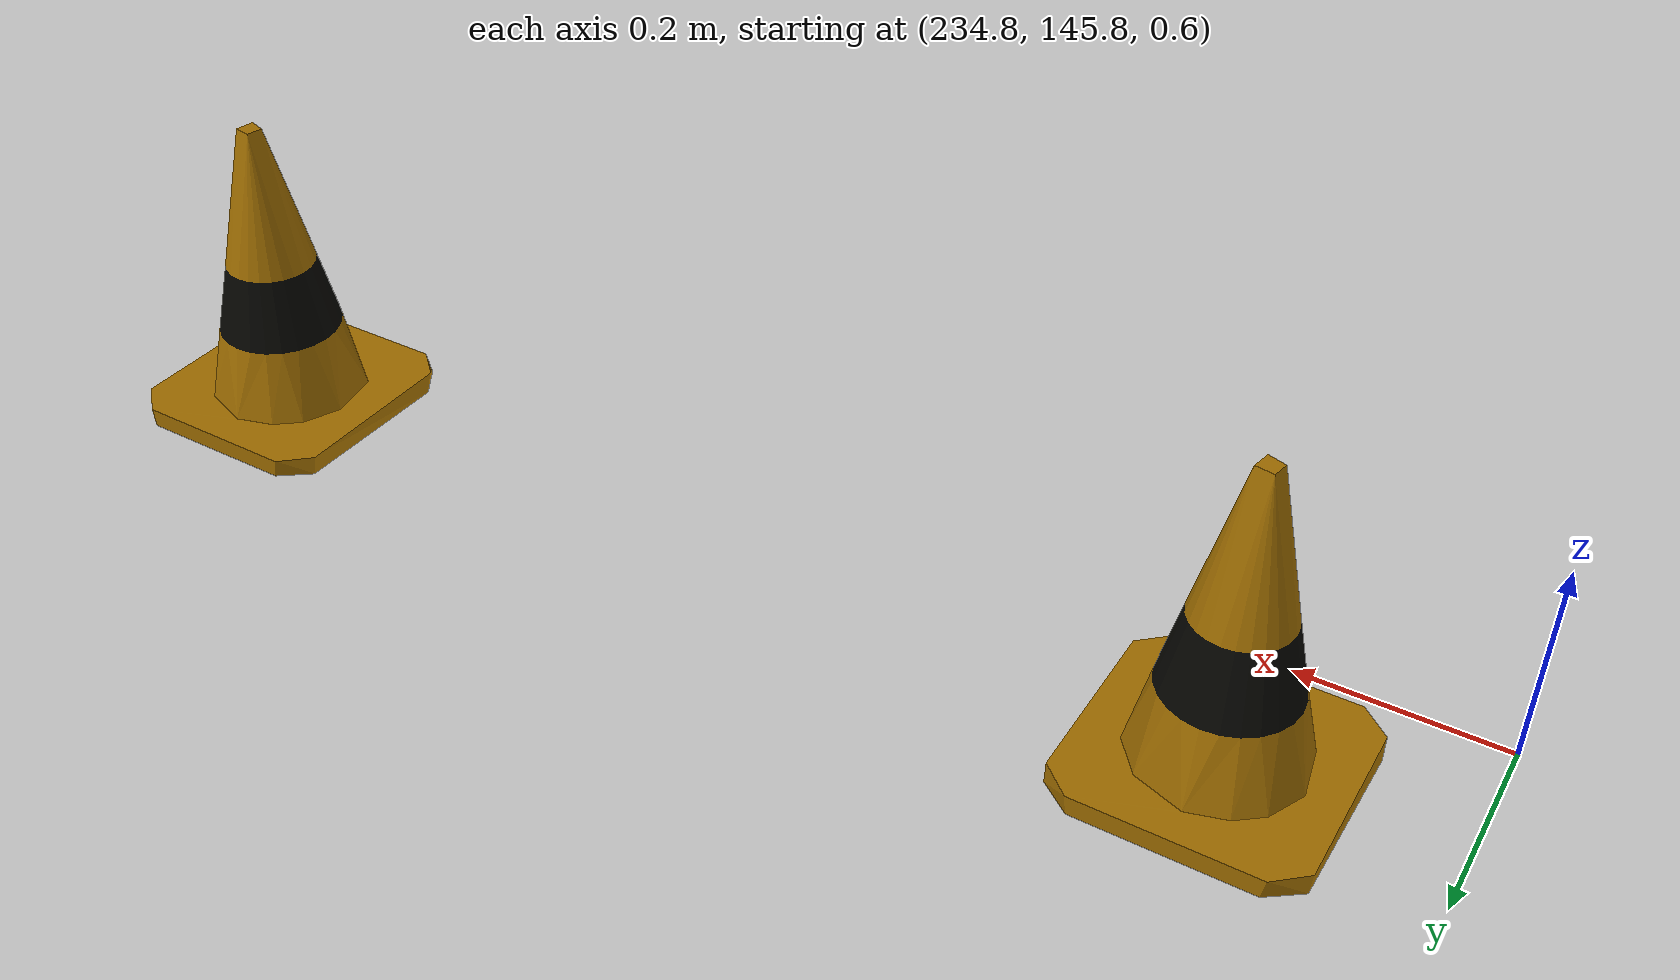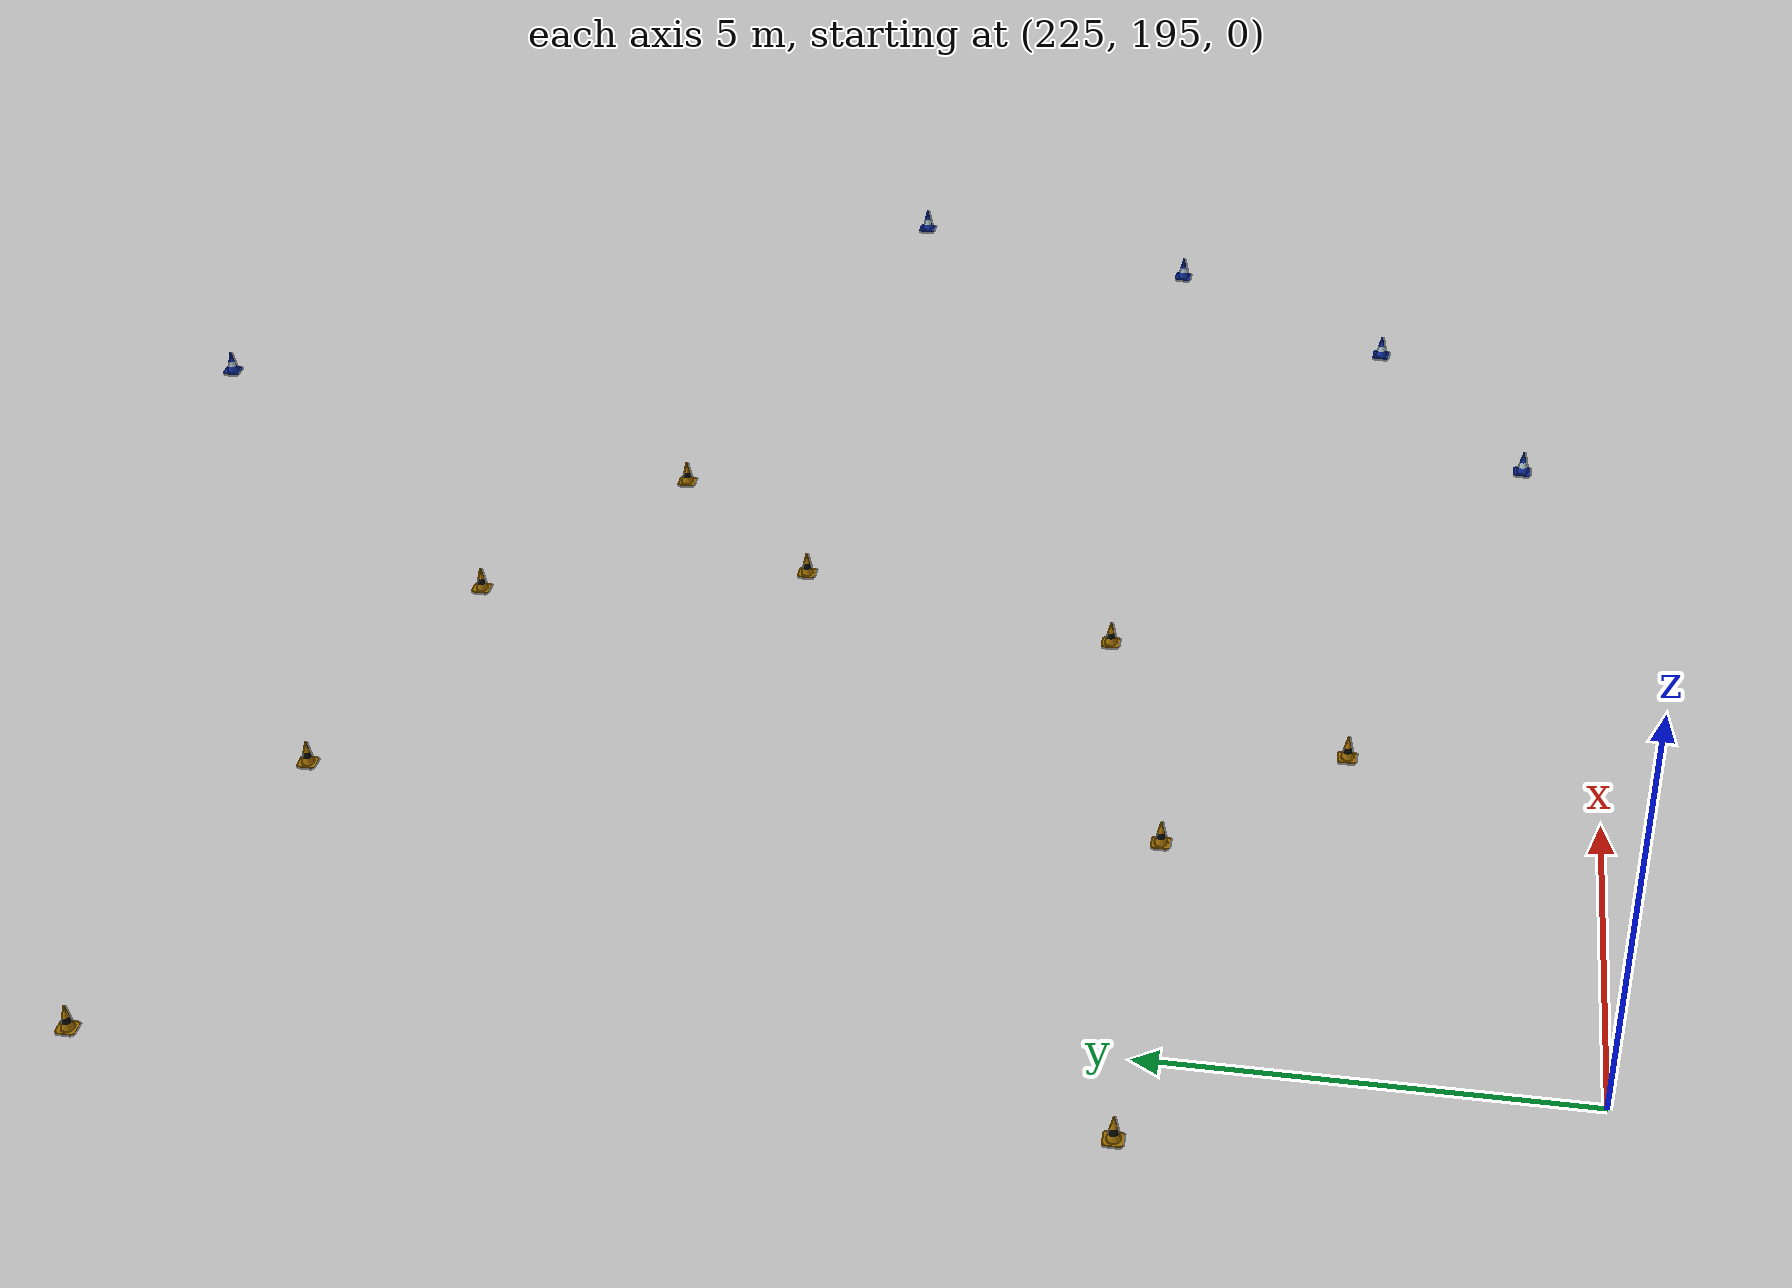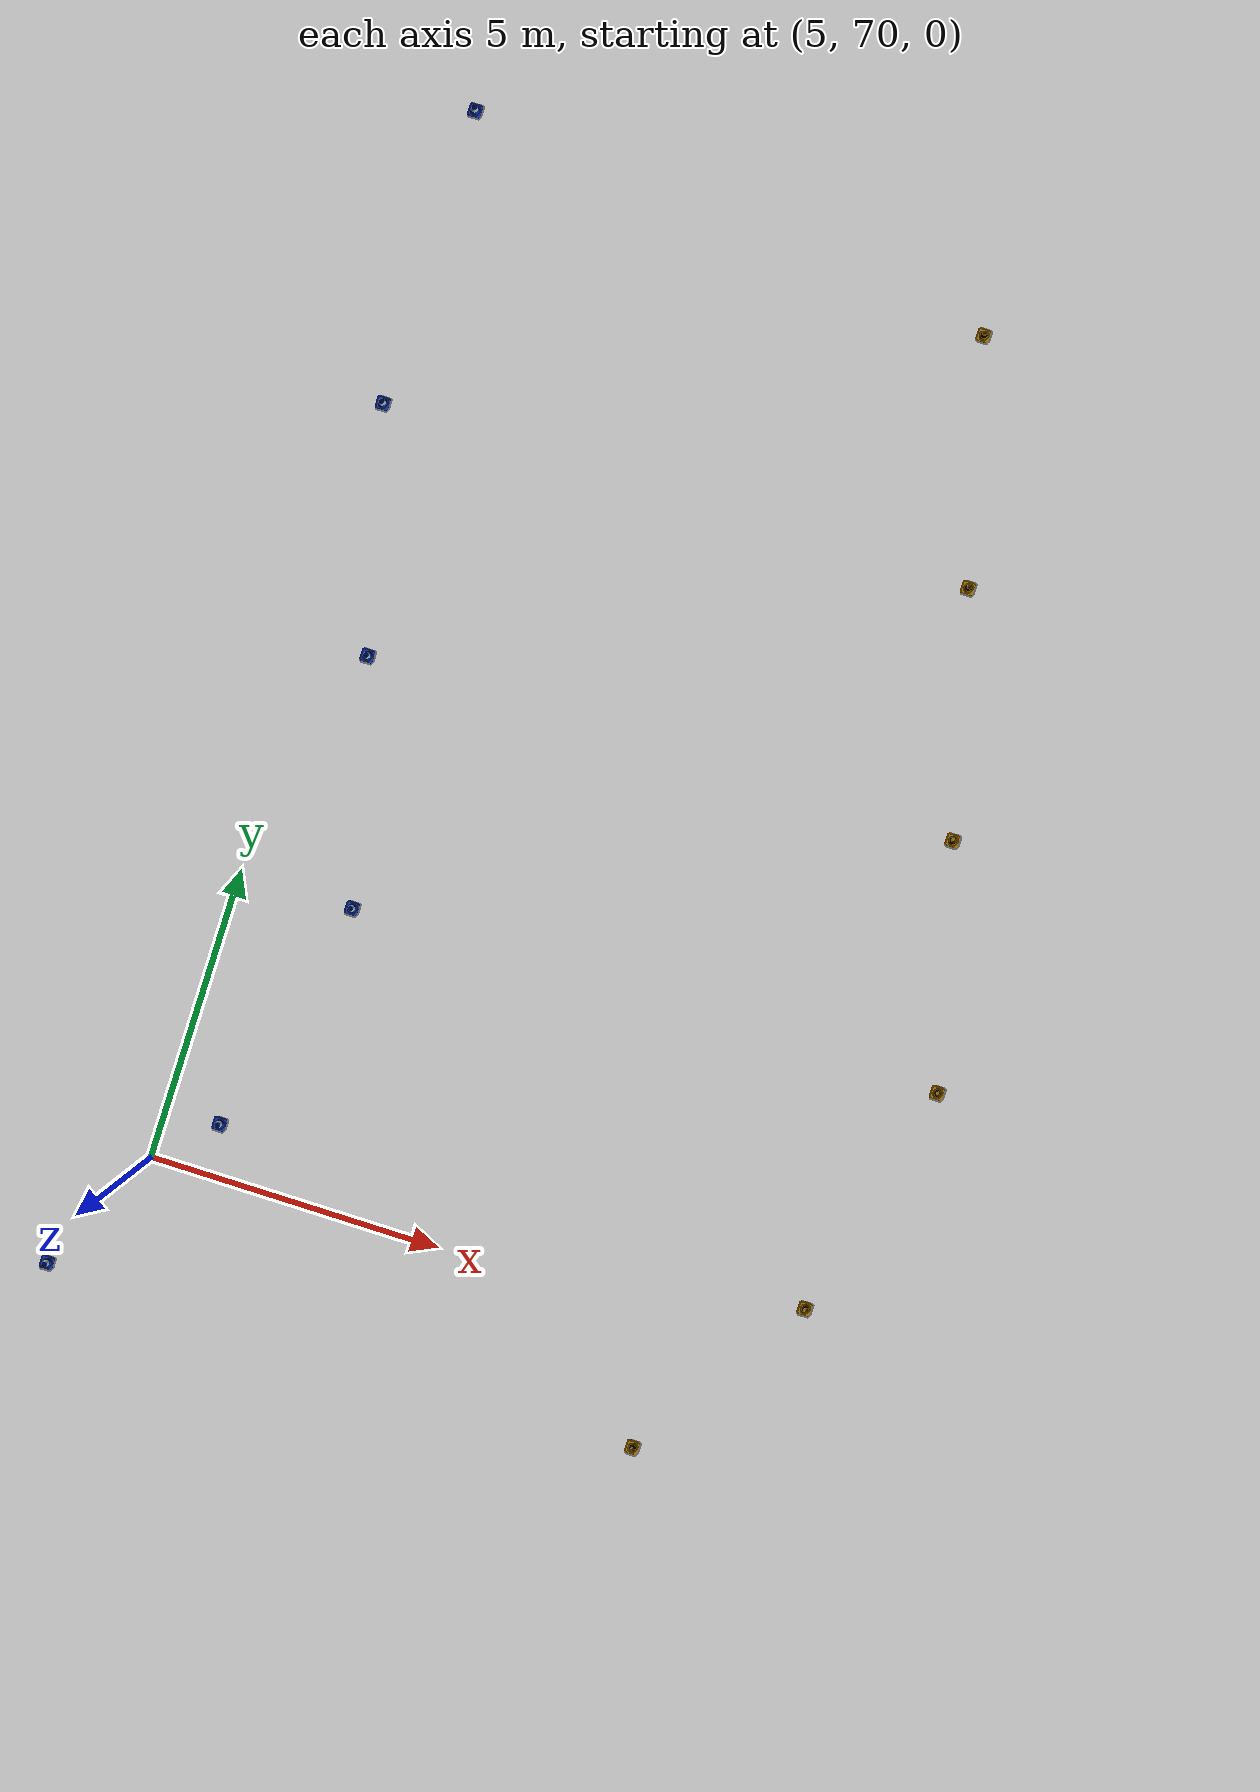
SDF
<sdf version='1.6'>
  <world name='monster'>
    <gui fullscreen='0'>
      <camera name='user_camera'>
        <pose frame=''>-40 40 20 0 0.667643 -1</pose>
        <view_controller>orbit</view_controller>
        <projection_type>perspective</projection_type>
      </camera>
    </gui>

    <!-- WORLD SETTINGS -->
    <scene>
      <sky>
        <clouds>
          <speed>3</speed>
        </clouds>
      </sky>
      <ambient>1.0 1.0 1.0 1.0</ambient>
      <shadows>false</shadows>
    </scene>

    <light name='sun' type='directional'>
      <cast_shadows>1</cast_shadows>
      <pose frame=''>0 0 10 0 -0 0</pose>
      <diffuse>0.8 0.8 0.8 1</diffuse>
      <specular>0.1 0.1 0.1 1</specular>
      <attenuation>
        <range>1000</range>
        <constant>0.9</constant>
        <linear>0.01</linear>
        <quadratic>0.001</quadratic>
      </attenuation>
      <direction>-0.5 0.5 -1</direction>
    </light>

    <!-- MODELS -->
    <include>
      <uri>model://models/ground_plane</uri>
      <pose>0.0 0.0 0.0 0 0 0</pose>
    </include>

    <include>
      <uri>model://models/monster</uri>
      <pose>0 0 0.5 0 0 0</pose>
    </include>

  </world>
</sdf>

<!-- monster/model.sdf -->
<sdf version='1.6'>
  <model name='track'>

    <link name='link_0_clone_0'>
      <pose frame=''>-45 216 0.15 0 -0 0</pose>

      <collision name="collision">
        <geometry>
          <mesh>
            <uri>model://eufs_description/meshes/cone_blue.dae</uri>
          </mesh>
        </geometry>
      </collision>

      <visual name="visual">
        <geometry>
          <mesh>
            <uri>model://eufs_description/meshes/cone_blue.dae</uri>
          </mesh>
        </geometry>
      </visual>
    </link>

    <link name='link_0_clone_1'>
      <pose frame=''>-43 219 0.15 0 -0 0</pose>

      <collision name="collision">
        <geometry>
          <mesh>
            <uri>model://eufs_description/meshes/cone_blue.dae</uri>
          </mesh>
        </geometry>
      </collision>

      <visual name="visual">
        <geometry>
          <mesh>
            <uri>model://eufs_description/meshes/cone_blue.dae</uri>
          </mesh>
        </geometry>
      </visual>
    </link>

    <link name='link_0_clone_2'>
      <pose frame=''>-42 209 0.15 0 -0 0</pose>

      <collision name="collision">
        <geometry>
          <mesh>
            <uri>model://eufs_description/meshes/cone_blue.dae</uri>
          </mesh>
        </geometry>
      </collision>

      <visual name="visual">
        <geometry>
          <mesh>
            <uri>model://eufs_description/meshes/cone_blue.dae</uri>
          </mesh>
        </geometry>
      </visual>
    </link>

    <link name='link_0_clone_3'>
      <pose frame=''>-39 207 0.15 0 -0 0</pose>

      <collision name="collision">
        <geometry>
          <mesh>
            <uri>model://eufs_description/meshes/cone_blue.dae</uri>
          </mesh>
        </geometry>
      </collision>

      <visual name="visual">
        <geometry>
          <mesh>
            <uri>model://eufs_description/meshes/cone_blue.dae</uri>
          </mesh>
        </geometry>
      </visual>
    </link>

    <link name='link_0_clone_4'>
      <pose frame=''>-36 213 0.15 0 -0 0</pose>

      <collision name="collision">
        <geometry>
          <mesh>
            <uri>model://eufs_description/meshes/cone_yellow.dae</uri>
          </mesh>
        </geometry>
      </collision>

      <visual name="visual">
        <geometry>
          <mesh>
            <uri>model://eufs_description/meshes/cone_yellow.dae</uri>
          </mesh>
        </geometry>
      </visual>
    </link>

    <link name='link_0_clone_5'>
      <pose frame=''>-35 216 0.15 0 -0 0</pose>

      <collision name="collision">
        <geometry>
          <mesh>
            <uri>model://eufs_description/meshes/cone_yellow.dae</uri>
          </mesh>
        </geometry>
      </collision>

      <visual name="visual">
        <geometry>
          <mesh>
            <uri>model://eufs_description/meshes/cone_yellow.dae</uri>
          </mesh>
        </geometry>
      </visual>
    </link>

    <link name='link_0_clone_6'>
      <pose frame=''>-35 226 0.15 0 -0 0</pose>

      <collision name="collision">
        <geometry>
          <mesh>
            <uri>model://eufs_description/meshes/cone_blue.dae</uri>
          </mesh>
        </geometry>
      </collision>

      <visual name="visual">
        <geometry>
          <mesh>
            <uri>model://eufs_description/meshes/cone_blue.dae</uri>
          </mesh>
        </geometry>
      </visual>
    </link>

    <link name='link_0_clone_7'>
      <pose frame=''>-31 -24 0.15 0 -0 0</pose>

      <collision name="collision">
        <geometry>
          <mesh>
            <uri>model://eufs_description/meshes/cone_blue.dae</uri>
          </mesh>
        </geometry>
      </collision>

      <visual name="visual">
        <geometry>
          <mesh>
            <uri>model://eufs_description/meshes/cone_blue.dae</uri>
          </mesh>
        </geometry>
      </visual>
    </link>

    <link name='link_0_clone_8'>
      <pose frame=''>-31 215 0.15 0 -0 0</pose>

      <collision name="collision">
        <geometry>
          <mesh>
            <uri>model://eufs_description/meshes/cone_yellow.dae</uri>
          </mesh>
        </geometry>
      </collision>

      <visual name="visual">
        <geometry>
          <mesh>
            <uri>model://eufs_description/meshes/cone_yellow.dae</uri>
          </mesh>
        </geometry>
      </visual>
    </link>

    <link name='link_0_clone_9'>
      <pose frame=''>-31 225 0.15 0 -0 0</pose>

      <collision name="collision">
        <geometry>
          <mesh>
            <uri>model://eufs_description/meshes/cone_blue.dae</uri>
          </mesh>
        </geometry>
      </collision>

      <visual name="visual">
        <geometry>
          <mesh>
            <uri>model://eufs_description/meshes/cone_blue.dae</uri>
          </mesh>
        </geometry>
      </visual>
    </link>

    <link name='link_0_clone_10'>
      <pose frame=''>-30 -20 0.15 0 -0 0</pose>

      <collision name="collision">
        <geometry>
          <mesh>
            <uri>model://eufs_description/meshes/cone_blue.dae</uri>
          </mesh>
        </geometry>
      </collision>

      <visual name="visual">
        <geometry>
          <mesh>
            <uri>model://eufs_description/meshes/cone_blue.dae</uri>
          </mesh>
        </geometry>
      </visual>
    </link>

    <link name='link_0_clone_11'>
      <pose frame=''>-30 216 0.15 0 -0 0</pose>

      <collision name="collision">
        <geometry>
          <mesh>
            <uri>model://eufs_description/meshes/cone_yellow.dae</uri>
          </mesh>
        </geometry>
      </collision>

      <visual name="visual">
        <geometry>
          <mesh>
            <uri>model://eufs_description/meshes/cone_yellow.dae</uri>
          </mesh>
        </geometry>
      </visual>
    </link>

    <link name='link_0_clone_12'>
      <pose frame=''>-29 -32 0.15 0 -0 0</pose>

      <collision name="collision">
        <geometry>
          <mesh>
            <uri>model://eufs_description/meshes/cone_blue.dae</uri>
          </mesh>
        </geometry>
      </collision>

      <visual name="visual">
        <geometry>
          <mesh>
            <uri>model://eufs_description/meshes/cone_blue.dae</uri>
          </mesh>
        </geometry>
      </visual>
    </link>

    <link name='link_0_clone_13'>
      <pose frame=''>-29 206 0.15 0 -0 0</pose>

      <collision name="collision">
        <geometry>
          <mesh>
            <uri>model://eufs_description/meshes/cone_blue.dae</uri>
          </mesh>
        </geometry>
      </collision>

      <visual name="visual">
        <geometry>
          <mesh>
            <uri>model://eufs_description/meshes/cone_blue.dae</uri>
          </mesh>
        </geometry>
      </visual>
    </link>

    <link name='link_0_clone_14'>
      <pose frame=''>-28 -17 0.15 0 -0 0</pose>

      <collision name="collision">
        <geometry>
          <mesh>
            <uri>model://eufs_description/meshes/cone_blue.dae</uri>
          </mesh>
        </geometry>
      </collision>

      <visual name="visual">
        <geometry>
          <mesh>
            <uri>model://eufs_description/meshes/cone_blue.dae</uri>
          </mesh>
        </geometry>
      </visual>
    </link>

    <link name='link_0_clone_15'>
      <pose frame=''>-28 206 0.15 0 -0 0</pose>

      <collision name="collision">
        <geometry>
          <mesh>
            <uri>model://eufs_description/meshes/cone_blue.dae</uri>
          </mesh>
        </geometry>
      </collision>

      <visual name="visual">
        <geometry>
          <mesh>
            <uri>model://eufs_description/meshes/cone_blue.dae</uri>
          </mesh>
        </geometry>
      </visual>
    </link>

    <link name='link_0_clone_16'>
      <pose frame=''>-28 223 0.15 0 -0 0</pose>

      <collision name="collision">
        <geometry>
          <mesh>
            <uri>model://eufs_description/meshes/cone_blue.dae</uri>
          </mesh>
        </geometry>
      </collision>

      <visual name="visual">
        <geometry>
          <mesh>
            <uri>model://eufs_description/meshes/cone_blue.dae</uri>
          </mesh>
        </geometry>
      </visual>
    </link>

    <link name='link_0_clone_17'>
      <pose frame=''>-26 -14 0.15 0 -0 0</pose>

      <collision name="collision">
        <geometry>
          <mesh>
            <uri>model://eufs_description/meshes/cone_blue.dae</uri>
          </mesh>
        </geometry>
      </collision>

      <visual name="visual">
        <geometry>
          <mesh>
            <uri>model://eufs_description/meshes/cone_blue.dae</uri>
          </mesh>
        </geometry>
      </visual>
    </link>

    <link name='link_0_clone_18'>
      <pose frame=''>-23 -12 0.15 0 -0 0</pose>

      <collision name="collision">
        <geometry>
          <mesh>
            <uri>model://eufs_description/meshes/cone_blue.dae</uri>
          </mesh>
        </geometry>
      </collision>

      <visual name="visual">
        <geometry>
          <mesh>
            <uri>model://eufs_description/meshes/cone_blue.dae</uri>
          </mesh>
        </geometry>
      </visual>
    </link>

    <link name='link_0_clone_19'>
      <pose frame=''>-23 206 0.15 0 -0 0</pose>

      <collision name="collision">
        <geometry>
          <mesh>
            <uri>model://eufs_description/meshes/cone_blue.dae</uri>
          </mesh>
        </geometry>
      </collision>

      <visual name="visual">
        <geometry>
          <mesh>
            <uri>model://eufs_description/meshes/cone_blue.dae</uri>
          </mesh>
        </geometry>
      </visual>
    </link>

    <link name='link_0_clone_20'>
      <pose frame=''>-22 -40 0.15 0 -0 0</pose>

      <collision name="collision">
        <geometry>
          <mesh>
            <uri>model://eufs_description/meshes/cone_blue.dae</uri>
          </mesh>
        </geometry>
      </collision>

      <visual name="visual">
        <geometry>
          <mesh>
            <uri>model://eufs_description/meshes/cone_blue.dae</uri>
          </mesh>
        </geometry>
      </visual>
    </link>

    <link name='link_0_clone_21'>
      <pose frame=''>-22 -30 0.15 0 -0 0</pose>

      <collision name="collision">
        <geometry>
          <mesh>
            <uri>model://eufs_description/meshes/cone_yellow.dae</uri>
          </mesh>
        </geometry>
      </collision>

      <visual name="visual">
        <geometry>
          <mesh>
            <uri>model://eufs_description/meshes/cone_yellow.dae</uri>
          </mesh>
        </geometry>
      </visual>
    </link>

    <link name='link_0_clone_22'>
      <pose frame=''>-22 219 0.15 0 -0 0</pose>

      <collision name="collision">
        <geometry>
          <mesh>
            <uri>model://eufs_description/meshes/cone_blue.dae</uri>
          </mesh>
        </geometry>
      </collision>

      <visual name="visual">
        <geometry>
          <mesh>
            <uri>model://eufs_description/meshes/cone_blue.dae</uri>
          </mesh>
        </geometry>
      </visual>
    </link>

    <link name='link_0_clone_23'>
      <pose frame=''>-21 -24 0.15 0 -0 0</pose>

      <collision name="collision">
        <geometry>
          <mesh>
            <uri>model://eufs_description/meshes/cone_yellow.dae</uri>
          </mesh>
        </geometry>
      </collision>

      <visual name="visual">
        <geometry>
          <mesh>
            <uri>model://eufs_description/meshes/cone_yellow.dae</uri>
          </mesh>
        </geometry>
      </visual>
    </link>

    <link name='link_0_clone_24'>
      <pose frame=''>-20 -20 0.15 0 -0 0</pose>

      <collision name="collision">
        <geometry>
          <mesh>
            <uri>model://eufs_description/meshes/cone_yellow.dae</uri>
          </mesh>
        </geometry>
      </collision>

      <visual name="visual">
        <geometry>
          <mesh>
            <uri>model://eufs_description/meshes/cone_yellow.dae</uri>
          </mesh>
        </geometry>
      </visual>
    </link>

    <link name='link_0_clone_25'>
      <pose frame=''>-20 163 0.15 0 -0 0</pose>

      <collision name="collision">
        <geometry>
          <mesh>
            <uri>model://eufs_description/meshes/cone_blue.dae</uri>
          </mesh>
        </geometry>
      </collision>

      <visual name="visual">
        <geometry>
          <mesh>
            <uri>model://eufs_description/meshes/cone_blue.dae</uri>
          </mesh>
        </geometry>
      </visual>
    </link>

    <link name='link_0_clone_26'>
      <pose frame=''>-20 216 0.15 0 -0 0</pose>

      <collision name="collision">
        <geometry>
          <mesh>
            <uri>model://eufs_description/meshes/cone_blue.dae</uri>
          </mesh>
        </geometry>
      </collision>

      <visual name="visual">
        <geometry>
          <mesh>
            <uri>model://eufs_description/meshes/cone_blue.dae</uri>
          </mesh>
        </geometry>
      </visual>
    </link>

    <link name='link_0_clone_27'>
      <pose frame=''>-19 -42 0.15 0 -0 0</pose>

      <collision name="collision">
        <geometry>
          <mesh>
            <uri>model://eufs_description/meshes/cone_blue.dae</uri>
          </mesh>
        </geometry>
      </collision>

      <visual name="visual">
        <geometry>
          <mesh>
            <uri>model://eufs_description/meshes/cone_blue.dae</uri>
          </mesh>
        </geometry>
      </visual>
    </link>

    <link name='link_0_clone_28'>
      <pose frame=''>-19 -32 0.15 0 -0 0</pose>

      <collision name="collision">
        <geometry>
          <mesh>
            <uri>model://eufs_description/meshes/cone_yellow.dae</uri>
          </mesh>
        </geometry>
      </collision>

      <visual name="visual">
        <geometry>
          <mesh>
            <uri>model://eufs_description/meshes/cone_yellow.dae</uri>
          </mesh>
        </geometry>
      </visual>
    </link>

    <link name='link_0_clone_29'>
      <pose frame=''>-19 122 0.15 0 -0 0</pose>

      <collision name="collision">
        <geometry>
          <mesh>
            <uri>model://eufs_description/meshes/cone_blue.dae</uri>
          </mesh>
        </geometry>
      </collision>

      <visual name="visual">
        <geometry>
          <mesh>
            <uri>model://eufs_description/meshes/cone_blue.dae</uri>
          </mesh>
        </geometry>
      </visual>
    </link>

    <link name='link_0_clone_30'>
      <pose frame=''>-19 167 0.15 0 -0 0</pose>

      <collision name="collision">
        <geometry>
          <mesh>
            <uri>model://eufs_description/meshes/cone_blue.dae</uri>
          </mesh>
        </geometry>
      </collision>

      <visual name="visual">
        <geometry>
          <mesh>
            <uri>model://eufs_description/meshes/cone_blue.dae</uri>
          </mesh>
        </geometry>
      </visual>
    </link>

    <link name='link_0_clone_31'>
      <pose frame=''>-18 -17 0.15 0 -0 0</pose>

      <collision name="collision">
        <geometry>
          <mesh>
            <uri>model://eufs_description/meshes/cone_yellow.dae</uri>
          </mesh>
        </geometry>
      </collision>

      <visual name="visual">
        <geometry>
          <mesh>
            <uri>model://eufs_description/meshes/cone_yellow.dae</uri>
          </mesh>
        </geometry>
      </visual>
    </link>

    <link name='link_0_clone_32'>
      <pose frame=''>-18 170 0.15 0 -0 0</pose>

      <collision name="collision">
        <geometry>
          <mesh>
            <uri>model://eufs_description/meshes/cone_blue.dae</uri>
          </mesh>
        </geometry>
      </collision>

      <visual name="visual">
        <geometry>
          <mesh>
            <uri>model://eufs_description/meshes/cone_blue.dae</uri>
          </mesh>
        </geometry>
      </visual>
    </link>

    <link name='link_0_clone_33'>
      <pose frame=''>-18 217 0.15 0 -0 0</pose>

      <collision name="collision">
        <geometry>
          <mesh>
            <uri>model://eufs_description/meshes/cone_blue.dae</uri>
          </mesh>
        </geometry>
      </collision>

      <visual name="visual">
        <geometry>
          <mesh>
            <uri>model://eufs_description/meshes/cone_blue.dae</uri>
          </mesh>
        </geometry>
      </visual>
    </link>

    <link name='link_0_clone_34'>
      <pose frame=''>-16 -44 0.15 0 -0 0</pose>

      <collision name="collision">
        <geometry>
          <mesh>
            <uri>model://eufs_description/meshes/cone_blue.dae</uri>
          </mesh>
        </geometry>
      </collision>

      <visual name="visual">
        <geometry>
          <mesh>
            <uri>model://eufs_description/meshes/cone_blue.dae</uri>
          </mesh>
        </geometry>
      </visual>
    </link>

    <link name='link_0_clone_35'>
      <pose frame=''>-16 -34 0.15 0 -0 0</pose>

      <collision name="collision">
        <geometry>
          <mesh>
            <uri>model://eufs_description/meshes/cone_yellow.dae</uri>
          </mesh>
        </geometry>
      </collision>

      <visual name="visual">
        <geometry>
          <mesh>
            <uri>model://eufs_description/meshes/cone_yellow.dae</uri>
          </mesh>
        </geometry>
      </visual>
    </link>

    <link name='link_0_clone_36'>
      <pose frame=''>-16 -14 0.15 0 -0 0</pose>

      <collision name="collision">
        <geometry>
          <mesh>
            <uri>model://eufs_description/meshes/cone_yellow.dae</uri>
          </mesh>
        </geometry>
      </collision>

      <visual name="visual">
        <geometry>
          <mesh>
            <uri>model://eufs_description/meshes/cone_yellow.dae</uri>
          </mesh>
        </geometry>
      </visual>
    </link>

    <link name='link_0_clone_37'>
      <pose frame=''>-15 -15 0.15 0 -0 0</pose>

      <collision name="collision">
        <geometry>
          <mesh>
            <uri>model://eufs_description/meshes/cone_yellow.dae</uri>
          </mesh>
        </geometry>
      </collision>

      <visual name="visual">
        <geometry>
          <mesh>
            <uri>model://eufs_description/meshes/cone_yellow.dae</uri>
          </mesh>
        </geometry>
      </visual>
    </link>

    <link name='link_0_clone_38'>
      <pose frame=''>-15 -5 0.15 0 -0 0</pose>

      <collision name="collision">
        <geometry>
          <mesh>
            <uri>model://eufs_description/meshes/cone_blue.dae</uri>
          </mesh>
        </geometry>
      </collision>

      <visual name="visual">
        <geometry>
          <mesh>
            <uri>model://eufs_description/meshes/cone_blue.dae</uri>
          </mesh>
        </geometry>
      </visual>
    </link>

    <link name='link_0_clone_39'>
      <pose frame=''>-15 209 0.15 0 -0 0</pose>

      <collision name="collision">
        <geometry>
          <mesh>
            <uri>model://eufs_description/meshes/cone_yellow.dae</uri>
          </mesh>
        </geometry>
      </collision>

      <visual name="visual">
        <geometry>
          <mesh>
            <uri>model://eufs_description/meshes/cone_yellow.dae</uri>
          </mesh>
        </geometry>
      </visual>
    </link>

    <link name='link_0_clone_40'>
      <pose frame=''>-13 -12 0.15 0 -0 0</pose>

      <collision name="collision">
        <geometry>
          <mesh>
            <uri>model://eufs_description/meshes/cone_yellow.dae</uri>
          </mesh>
        </geometry>
      </collision>

      <visual name="visual">
        <geometry>
          <mesh>
            <uri>model://eufs_description/meshes/cone_yellow.dae</uri>
          </mesh>
        </geometry>
      </visual>
    </link>

    <link name='link_0_clone_41'>
      <pose frame=''>-13 114 0.15 0 -0 0</pose>

      <collision name="collision">
        <geometry>
          <mesh>
            <uri>model://eufs_description/meshes/cone_blue.dae</uri>
          </mesh>
        </geometry>
      </collision>

      <visual name="visual">
        <geometry>
          <mesh>
            <uri>model://eufs_description/meshes/cone_blue.dae</uri>
          </mesh>
        </geometry>
      </visual>
    </link>

    <link name='link_0_clone_42'>
      <pose frame=''>-13 218 0.15 0 -0 0</pose>

      <collision name="collision">
        <geometry>
          <mesh>
            <uri>model://eufs_description/meshes/cone_blue.dae</uri>
          </mesh>
        </geometry>
      </collision>

      <visual name="visual">
        <geometry>
          <mesh>
            <uri>model://eufs_description/meshes/cone_blue.dae</uri>
          </mesh>
        </geometry>
      </visual>
    </link>

    <link name='link_0_clone_43'>
      <pose frame=''>-12 -45 0.15 0 -0 0</pose>

      <collision name="collision">
        <geometry>
          <mesh>
            <uri>model://eufs_description/meshes/cone_blue.dae</uri>
          </mesh>
        </geometry>
      </collision>

      <visual name="visual">
        <geometry>
          <mesh>
            <uri>model://eufs_description/meshes/cone_blue.dae</uri>
          </mesh>
        </geometry>
      </visual>
    </link>

    <link name='link_0_clone_44'>
      <pose frame=''>-12 -35 0.15 0 -0 0</pose>

      <collision name="collision">
        <geometry>
          <mesh>
            <uri>model://eufs_description/meshes/cone_yellow.dae</uri>
          </mesh>
        </geometry>
      </collision>

      <visual name="visual">
        <geometry>
          <mesh>
            <uri>model://eufs_description/meshes/cone_yellow.dae</uri>
          </mesh>
        </geometry>
      </visual>
    </link>

    <link name='link_0_clone_45'>
      <pose frame=''>-12 -13 0.15 0 -0 0</pose>

      <collision name="collision">
        <geometry>
          <mesh>
            <uri>model://eufs_description/meshes/cone_yellow.dae</uri>
          </mesh>
        </geometry>
      </collision>

      <visual name="visual">
        <geometry>
          <mesh>
            <uri>model://eufs_description/meshes/cone_yellow.dae</uri>
          </mesh>
        </geometry>
      </visual>
    </link>

    <link name='link_0_clone_46'>
      <pose frame=''>-12 -3 0.15 0 -0 0</pose>

      <collision name="collision">
        <geometry>
          <mesh>
            <uri>model://eufs_description/meshes/cone_blue.dae</uri>
          </mesh>
        </geometry>
      </collision>

      <visual name="visual">
        <geometry>
          <mesh>
            <uri>model://eufs_description/meshes/cone_blue.dae</uri>
          </mesh>
        </geometry>
      </visual>
    </link>

    <link name='link_0_clone_47'>
      <pose frame=''>-11 9 0.15 0 -0 0</pose>

      <collision name="collision">
        <geometry>
          <mesh>
            <uri>model://eufs_description/meshes/cone_blue.dae</uri>
          </mesh>
        </geometry>
      </collision>

      <visual name="visual">
        <geometry>
          <mesh>
            <uri>model://eufs_description/meshes/cone_blue.dae</uri>
          </mesh>
        </geometry>
      </visual>
    </link>

    <link name='link_0_clone_48'>
      <pose frame=''>-11 111 0.15 0 -0 0</pose>

      <collision name="collision">
        <geometry>
          <mesh>
            <uri>model://eufs_description/meshes/cone_blue.dae</uri>
          </mesh>
        </geometry>
      </collision>

      <visual name="visual">
        <geometry>
          <mesh>
            <uri>model://eufs_description/meshes/cone_blue.dae</uri>
          </mesh>
        </geometry>
      </visual>
    </link>

    <link name='link_0_clone_49'>
      <pose frame=''>-11 121 0.15 0 -0 0</pose>

      <collision name="collision">
        <geometry>
          <mesh>
            <uri>model://eufs_description/meshes/cone_yellow.dae</uri>
          </mesh>
        </geometry>
      </collision>

      <visual name="visual">
        <geometry>
          <mesh>
            <uri>model://eufs_description/meshes/cone_yellow.dae</uri>
          </mesh>
        </geometry>
      </visual>
    </link>

    <link name='link_0_clone_50'>
      <pose frame=''>-11 210 0.15 0 -0 0</pose>

      <collision name="collision">
        <geometry>
          <mesh>
            <uri>model://eufs_description/meshes/cone_yellow.dae</uri>
          </mesh>
        </geometry>
      </collision>

      <visual name="visual">
        <geometry>
          <mesh>
            <uri>model://eufs_description/meshes/cone_yellow.dae</uri>
          </mesh>
        </geometry>
      </visual>
    </link>

    <link name='link_0_clone_51'>
      <pose frame=''>-10 -10 0.15 0 -0 0</pose>

      <collision name="collision">
        <geometry>
          <mesh>
            <uri>model://eufs_description/meshes/cone_yellow.dae</uri>
          </mesh>
        </geometry>
      </collision>

      <visual name="visual">
        <geometry>
          <mesh>
            <uri>model://eufs_description/meshes/cone_yellow.dae</uri>
          </mesh>
        </geometry>
      </visual>
    </link>

    <link name='link_0_clone_52'>
      <pose frame=''>-10 123 0.15 0 -0 0</pose>

      <collision name="collision">
        <geometry>
          <mesh>
            <uri>model://eufs_description/meshes/cone_yellow.dae</uri>
          </mesh>
        </geometry>
      </collision>

      <visual name="visual">
        <geometry>
          <mesh>
            <uri>model://eufs_description/meshes/cone_yellow.dae</uri>
          </mesh>
        </geometry>
      </visual>
    </link>

    <link name='link_0_clone_53'>
      <pose frame=''>-10 163 0.15 0 -0 0</pose>

      <collision name="collision">
        <geometry>
          <mesh>
            <uri>model://eufs_description/meshes/cone_yellow.dae</uri>
          </mesh>
        </geometry>
      </collision>

      <visual name="visual">
        <geometry>
          <mesh>
            <uri>model://eufs_description/meshes/cone_yellow.dae</uri>
          </mesh>
        </geometry>
      </visual>
    </link>

    <link name='link_0_clone_54'>
      <pose frame=''>-9 165 0.15 0 -0 0</pose>

      <collision name="collision">
        <geometry>
          <mesh>
            <uri>model://eufs_description/meshes/cone_yellow.dae</uri>
          </mesh>
        </geometry>
      </collision>

      <visual name="visual">
        <geometry>
          <mesh>
            <uri>model://eufs_description/meshes/cone_yellow.dae</uri>
          </mesh>
        </geometry>
      </visual>
    </link>

    <link name='link_0_clone_55'>
      <pose frame=''>-9 167 0.15 0 -0 0</pose>

      <collision name="collision">
        <geometry>
          <mesh>
            <uri>model://eufs_description/meshes/cone_yellow.dae</uri>
          </mesh>
        </geometry>
      </collision>

      <visual name="visual">
        <geometry>
          <mesh>
            <uri>model://eufs_description/meshes/cone_yellow.dae</uri>
          </mesh>
        </geometry>
      </visual>
    </link>

    <link name='link_0_clone_56'>
      <pose frame=''>-9 171 0.15 0 -0 0</pose>

      <collision name="collision">
        <geometry>
          <mesh>
            <uri>model://eufs_description/meshes/cone_yellow.dae</uri>
          </mesh>
        </geometry>
      </collision>

      <visual name="visual">
        <geometry>
          <mesh>
            <uri>model://eufs_description/meshes/cone_yellow.dae</uri>
          </mesh>
        </geometry>
      </visual>
    </link>

    <link name='link_0_clone_57'>
      <pose frame=''>-8 109 0.15 0 -0 0</pose>

      <collision name="collision">
        <geometry>
          <mesh>
            <uri>model://eufs_description/meshes/cone_blue.dae</uri>
          </mesh>
        </geometry>
      </collision>

      <visual name="visual">
        <geometry>
          <mesh>
            <uri>model://eufs_description/meshes/cone_blue.dae</uri>
          </mesh>
        </geometry>
      </visual>
    </link>

    <link name='link_0_clone_58'>
      <pose frame=''>-8 119 0.15 0 -0 0</pose>

      <collision name="collision">
        <geometry>
          <mesh>
            <uri>model://eufs_description/meshes/cone_yellow.dae</uri>
          </mesh>
        </geometry>
      </collision>

      <visual name="visual">
        <geometry>
          <mesh>
            <uri>model://eufs_description/meshes/cone_yellow.dae</uri>
          </mesh>
        </geometry>
      </visual>
    </link>

    <link name='link_0_clone_59'>
      <pose frame=''>-8 169 0.15 0 -0 0</pose>

      <collision name="collision">
        <geometry>
          <mesh>
            <uri>model://eufs_description/meshes/cone_yellow.dae</uri>
          </mesh>
        </geometry>
      </collision>

      <visual name="visual">
        <geometry>
          <mesh>
            <uri>model://eufs_description/meshes/cone_yellow.dae</uri>
          </mesh>
        </geometry>
      </visual>
    </link>

    <link name='link_0_clone_60'>
      <pose frame=''>-8 219 0.15 0 -0 0</pose>

      <collision name="collision">
        <geometry>
          <mesh>
            <uri>model://eufs_description/meshes/cone_blue.dae</uri>
          </mesh>
        </geometry>
      </collision>

      <visual name="visual">
        <geometry>
          <mesh>
            <uri>model://eufs_description/meshes/cone_blue.dae</uri>
          </mesh>
        </geometry>
      </visual>
    </link>

    <link name='link_0_clone_61'>
      <pose frame=''>-7 -45 0.15 0 -0 0</pose>

      <collision name="collision">
        <geometry>
          <mesh>
            <uri>model://eufs_description/meshes/cone_blue.dae</uri>
          </mesh>
        </geometry>
      </collision>

      <visual name="visual">
        <geometry>
          <mesh>
            <uri>model://eufs_description/meshes/cone_blue.dae</uri>
          </mesh>
        </geometry>
      </visual>
    </link>

    <link name='link_0_clone_62'>
      <pose frame=''>-7 -35 0.15 0 -0 0</pose>

      <collision name="collision">
        <geometry>
          <mesh>
            <uri>model://eufs_description/meshes/cone_yellow.dae</uri>
          </mesh>
        </geometry>
      </collision>

      <visual name="visual">
        <geometry>
          <mesh>
            <uri>model://eufs_description/meshes/cone_yellow.dae</uri>
          </mesh>
        </geometry>
      </visual>
    </link>

    <link name='link_0_clone_63'>
      <pose frame=''>-7 152 0.15 0 -0 0</pose>

      <collision name="collision">
        <geometry>
          <mesh>
            <uri>model://eufs_description/meshes/cone_yellow.dae</uri>
          </mesh>
        </geometry>
      </collision>

      <visual name="visual">
        <geometry>
          <mesh>
            <uri>model://eufs_description/meshes/cone_yellow.dae</uri>
          </mesh>
        </geometry>
      </visual>
    </link>

    <link name='link_0_clone_64'>
      <pose frame=''>-6 29 0.15 0 -0 0</pose>

      <collision name="collision">
        <geometry>
          <mesh>
            <uri>model://eufs_description/meshes/cone_blue.dae</uri>
          </mesh>
        </geometry>
      </collision>

      <visual name="visual">
        <geometry>
          <mesh>
            <uri>model://eufs_description/meshes/cone_blue.dae</uri>
          </mesh>
        </geometry>
      </visual>
    </link>

    <link name='link_0_clone_65'>
      <pose frame=''>-6 172 0.15 0 -0 0</pose>

      <collision name="collision">
        <geometry>
          <mesh>
            <uri>model://eufs_description/meshes/cone_yellow.dae</uri>
          </mesh>
        </geometry>
      </collision>

      <visual name="visual">
        <geometry>
          <mesh>
            <uri>model://eufs_description/meshes/cone_yellow.dae</uri>
          </mesh>
        </geometry>
      </visual>
    </link>

    <link name='link_0_clone_66'>
      <pose frame=''>-6 211 0.15 0 -0 0</pose>

      <collision name="collision">
        <geometry>
          <mesh>
            <uri>model://eufs_description/meshes/cone_yellow.dae</uri>
          </mesh>
        </geometry>
      </collision>

      <visual name="visual">
        <geometry>
          <mesh>
            <uri>model://eufs_description/meshes/cone_yellow.dae</uri>
          </mesh>
        </geometry>
      </visual>
    </link>

    <link name='link_0_clone_67'>
      <pose frame=''>-4 108 0.15 0 -0 0</pose>

      <collision name="collision">
        <geometry>
          <mesh>
            <uri>model://eufs_description/meshes/cone_blue.dae</uri>
          </mesh>
        </geometry>
      </collision>

      <visual name="visual">
        <geometry>
          <mesh>
            <uri>model://eufs_description/meshes/cone_blue.dae</uri>
          </mesh>
        </geometry>
      </visual>
    </link>

    <link name='link_0_clone_68'>
      <pose frame=''>-4 118 0.15 0 -0 0</pose>

      <collision name="collision">
        <geometry>
          <mesh>
            <uri>model://eufs_description/meshes/cone_yellow.dae</uri>
          </mesh>
        </geometry>
      </collision>

      <visual name="visual">
        <geometry>
          <mesh>
            <uri>model://eufs_description/meshes/cone_yellow.dae</uri>
          </mesh>
        </geometry>
      </visual>
    </link>

    <link name='link_0_clone_69'>
      <pose frame=''>-3 220 0.15 0 -0 0</pose>

      <collision name="collision">
        <geometry>
          <mesh>
            <uri>model://eufs_description/meshes/cone_blue.dae</uri>
          </mesh>
        </geometry>
      </collision>

      <visual name="visual">
        <geometry>
          <mesh>
            <uri>model://eufs_description/meshes/cone_blue.dae</uri>
          </mesh>
        </geometry>
      </visual>
    </link>

    <link name='link_0_clone_70'>
      <pose frame=''>-2 -44 0.15 0 -0 0</pose>

      <collision name="collision">
        <geometry>
          <mesh>
            <uri>model://eufs_description/meshes/cone_blue.dae</uri>
          </mesh>
        </geometry>
      </collision>

      <visual name="visual">
        <geometry>
          <mesh>
            <uri>model://eufs_description/meshes/cone_blue.dae</uri>
          </mesh>
        </geometry>
      </visual>
    </link>

    <link name='link_0_clone_71'>
      <pose frame=''>-2 -34 0.15 0 -0 0</pose>

      <collision name="collision">
        <geometry>
          <mesh>
            <uri>model://eufs_description/meshes/cone_yellow.dae</uri>
          </mesh>
        </geometry>
      </collision>

      <visual name="visual">
        <geometry>
          <mesh>
            <uri>model://eufs_description/meshes/cone_yellow.dae</uri>
          </mesh>
        </geometry>
      </visual>
    </link>

    <link name='link_0_clone_72'>
      <pose frame=''>-2 6 0.15 0 -0 0</pose>

      <collision name="collision">
        <geometry>
          <mesh>
            <uri>model://eufs_description/meshes/cone_yellow.dae</uri>
          </mesh>
        </geometry>
      </collision>

      <visual name="visual">
        <geometry>
          <mesh>
            <uri>model://eufs_description/meshes/cone_yellow.dae</uri>
          </mesh>
        </geometry>
      </visual>
    </link>

    <link name='link_0_clone_73'>
      <pose frame=''>-2 133 0.15 0 -0 0</pose>

      <collision name="collision">
        <geometry>
          <mesh>
            <uri>model://eufs_description/meshes/cone_yellow.dae</uri>
          </mesh>
        </geometry>
      </collision>

      <visual name="visual">
        <geometry>
          <mesh>
            <uri>model://eufs_description/meshes/cone_yellow.dae</uri>
          </mesh>
        </geometry>
      </visual>
    </link>

    <link name='link_0_clone_74'>
      <pose frame=''>-1 -34 0.15 0 -0 0</pose>

      <collision name="collision">
        <geometry>
          <mesh>
            <uri>model://eufs_description/meshes/cone_yellow.dae</uri>
          </mesh>
        </geometry>
      </collision>

      <visual name="visual">
        <geometry>
          <mesh>
            <uri>model://eufs_description/meshes/cone_yellow.dae</uri>
          </mesh>
        </geometry>
      </visual>
    </link>

    <link name='link_0_clone_75'>
      <pose frame=''>-1 49 0.15 0 -0 0</pose>

      <collision name="collision">
        <geometry>
          <mesh>
            <uri>model://eufs_description/meshes/cone_blue.dae</uri>
          </mesh>
        </geometry>
      </collision>

      <visual name="visual">
        <geometry>
          <mesh>
            <uri>model://eufs_description/meshes/cone_blue.dae</uri>
          </mesh>
        </geometry>
      </visual>
    </link>

    <link name='link_0_clone_76'>
      <pose frame=''>-1 212 0.15 0 -0 0</pose>

      <collision name="collision">
        <geometry>
          <mesh>
            <uri>model://eufs_description/meshes/cone_yellow.dae</uri>
          </mesh>
        </geometry>
      </collision>

      <visual name="visual">
        <geometry>
          <mesh>
            <uri>model://eufs_description/meshes/cone_yellow.dae</uri>
          </mesh>
        </geometry>
      </visual>
    </link>

    <link name='link_0_clone_77'>
      <pose frame=''>0 109 0.15 0 -0 0</pose>

      <collision name="collision">
        <geometry>
          <mesh>
            <uri>model://eufs_description/meshes/cone_blue.dae</uri>
          </mesh>
        </geometry>
      </collision>

      <visual name="visual">
        <geometry>
          <mesh>
            <uri>model://eufs_description/meshes/cone_blue.dae</uri>
          </mesh>
        </geometry>
      </visual>
    </link>

    <link name='link_0_clone_78'>
      <pose frame=''>0 119 0.15 0 -0 0</pose>

      <collision name="collision">
        <geometry>
          <mesh>
            <uri>model://eufs_description/meshes/cone_yellow.dae</uri>
          </mesh>
        </geometry>
      </collision>

      <visual name="visual">
        <geometry>
          <mesh>
            <uri>model://eufs_description/meshes/cone_yellow.dae</uri>
          </mesh>
        </geometry>
      </visual>
    </link>

    <link name='link_0_clone_79'>
      <pose frame=''>1 123 0.15 0 -0 0</pose>

      <collision name="collision">
        <geometry>
          <mesh>
            <uri>model://eufs_description/meshes/cone_yellow.dae</uri>
          </mesh>
        </geometry>
      </collision>

      <visual name="visual">
        <geometry>
          <mesh>
            <uri>model://eufs_description/meshes/cone_yellow.dae</uri>
          </mesh>
        </geometry>
      </visual>
    </link>

    <link name='link_0_clone_80'>
      <pose frame=''>1 165 0.15 0 -0 0</pose>

      <collision name="collision">
        <geometry>
          <mesh>
            <uri>model://eufs_description/meshes/cone_blue.dae</uri>
          </mesh>
        </geometry>
      </collision>

      <visual name="visual">
        <geometry>
          <mesh>
            <uri>model://eufs_description/meshes/cone_blue.dae</uri>
          </mesh>
        </geometry>
      </visual>
    </link>

    <link name='link_0_clone_81'>
      <pose frame=''>2 155 0.15 0 -0 0</pose>

      <collision name="collision">
        <geometry>
          <mesh>
            <uri>model://eufs_description/meshes/cone_blue.dae</uri>
          </mesh>
        </geometry>
      </collision>

      <visual name="visual">
        <geometry>
          <mesh>
            <uri>model://eufs_description/meshes/cone_blue.dae</uri>
          </mesh>
        </geometry>
      </visual>
    </link>

    <link name='link_0_clone_82'>
      <pose frame=''>2 169 0.15 0 -0 0</pose>

      <collision name="collision">
        <geometry>
          <mesh>
            <uri>model://eufs_description/meshes/cone_blue.dae</uri>
          </mesh>
        </geometry>
      </collision>

      <visual name="visual">
        <geometry>
          <mesh>
            <uri>model://eufs_description/meshes/cone_blue.dae</uri>
          </mesh>
        </geometry>
      </visual>
    </link>

    <link name='link_0_clone_83'>
      <pose frame=''>2 179 0.15 0 -0 0</pose>

      <collision name="collision">
        <geometry>
          <mesh>
            <uri>model://eufs_description/meshes/cone_yellow.dae</uri>
          </mesh>
        </geometry>
      </collision>

      <visual name="visual">
        <geometry>
          <mesh>
            <uri>model://eufs_description/meshes/cone_yellow.dae</uri>
          </mesh>
        </geometry>
      </visual>
    </link>

    <link name='link_0_clone_84'>
      <pose frame=''>2 221 0.15 0 -0 0</pose>

      <collision name="collision">
        <geometry>
          <mesh>
            <uri>model://eufs_description/meshes/cone_blue.dae</uri>
          </mesh>
        </geometry>
      </collision>

      <visual name="visual">
        <geometry>
          <mesh>
            <uri>model://eufs_description/meshes/cone_blue.dae</uri>
          </mesh>
        </geometry>
      </visual>
    </link>

    <link name='link_0_clone_85'>
      <pose frame=''>3 26 0.15 0 -0 0</pose>

      <collision name="collision">
        <geometry>
          <mesh>
            <uri>model://eufs_description/meshes/cone_yellow.dae</uri>
          </mesh>
        </geometry>
      </collision>

      <visual name="visual">
        <geometry>
          <mesh>
            <uri>model://eufs_description/meshes/cone_yellow.dae</uri>
          </mesh>
        </geometry>
      </visual>
    </link>

    <link name='link_0_clone_86'>
      <pose frame=''>3 111 0.15 0 -0 0</pose>

      <collision name="collision">
        <geometry>
          <mesh>
            <uri>model://eufs_description/meshes/cone_blue.dae</uri>
          </mesh>
        </geometry>
      </collision>

      <visual name="visual">
        <geometry>
          <mesh>
            <uri>model://eufs_description/meshes/cone_blue.dae</uri>
          </mesh>
        </geometry>
      </visual>
    </link>

    <link name='link_0_clone_87'>
      <pose frame=''>4 68 0.15 0 -0 0</pose>

      <collision name="collision">
        <geometry>
          <mesh>
            <uri>model://eufs_description/meshes/cone_blue.dae</uri>
          </mesh>
        </geometry>
      </collision>

      <visual name="visual">
        <geometry>
          <mesh>
            <uri>model://eufs_description/meshes/cone_blue.dae</uri>
          </mesh>
        </geometry>
      </visual>
    </link>

    <link name='link_0_clone_88'>
      <pose frame=''>4 213 0.15 0 -0 0</pose>

      <collision name="collision">
        <geometry>
          <mesh>
            <uri>model://eufs_description/meshes/cone_yellow.dae</uri>
          </mesh>
        </geometry>
      </collision>

      <visual name="visual">
        <geometry>
          <mesh>
            <uri>model://eufs_description/meshes/cone_yellow.dae</uri>
          </mesh>
        </geometry>
      </visual>
    </link>

    <link name='link_0_clone_89'>
      <pose frame=''>5 83 0.15 0 -0 0</pose>

      <collision name="collision">
        <geometry>
          <mesh>
            <uri>model://eufs_description/meshes/cone_blue.dae</uri>
          </mesh>
        </geometry>
      </collision>

      <visual name="visual">
        <geometry>
          <mesh>
            <uri>model://eufs_description/meshes/cone_blue.dae</uri>
          </mesh>
        </geometry>
      </visual>
    </link>

    <link name='link_0_clone_90'>
      <pose frame=''>5 88 0.15 0 -0 0</pose>

      <collision name="collision">
        <geometry>
          <mesh>
            <uri>model://eufs_description/meshes/cone_blue.dae</uri>
          </mesh>
        </geometry>
      </collision>

      <visual name="visual">
        <geometry>
          <mesh>
            <uri>model://eufs_description/meshes/cone_blue.dae</uri>
          </mesh>
        </geometry>
      </visual>
    </link>

    <link name='link_0_clone_91'>
      <pose frame=''>6 -41 0.15 0 -0 0</pose>

      <collision name="collision">
        <geometry>
          <mesh>
            <uri>model://eufs_description/meshes/cone_blue.dae</uri>
          </mesh>
        </geometry>
      </collision>

      <visual name="visual">
        <geometry>
          <mesh>
            <uri>model://eufs_description/meshes/cone_blue.dae</uri>
          </mesh>
        </geometry>
      </visual>
    </link>

    <link name='link_0_clone_92'>
      <pose frame=''>6 71 0.15 0 -0 0</pose>

      <collision name="collision">
        <geometry>
          <mesh>
            <uri>model://eufs_description/meshes/cone_blue.dae</uri>
          </mesh>
        </geometry>
      </collision>

      <visual name="visual">
        <geometry>
          <mesh>
            <uri>model://eufs_description/meshes/cone_blue.dae</uri>
          </mesh>
        </geometry>
      </visual>
    </link>

    <link name='link_0_clone_93'>
      <pose frame=''>6 79 0.15 0 -0 0</pose>

      <collision name="collision">
        <geometry>
          <mesh>
            <uri>model://eufs_description/meshes/cone_blue.dae</uri>
          </mesh>
        </geometry>
      </collision>

      <visual name="visual">
        <geometry>
          <mesh>
            <uri>model://eufs_description/meshes/cone_blue.dae</uri>
          </mesh>
        </geometry>
      </visual>
    </link>

    <link name='link_0_clone_94'>
      <pose frame=''>6 170 0.15 0 -0 0</pose>

      <collision name="collision">
        <geometry>
          <mesh>
            <uri>model://eufs_description/meshes/cone_blue.dae</uri>
          </mesh>
        </geometry>
      </collision>

      <visual name="visual">
        <geometry>
          <mesh>
            <uri>model://eufs_description/meshes/cone_blue.dae</uri>
          </mesh>
        </geometry>
      </visual>
    </link>

    <link name='link_0_clone_95'>
      <pose frame=''>6 180 0.15 0 -0 0</pose>

      <collision name="collision">
        <geometry>
          <mesh>
            <uri>model://eufs_description/meshes/cone_yellow.dae</uri>
          </mesh>
        </geometry>
      </collision>

      <visual name="visual">
        <geometry>
          <mesh>
            <uri>model://eufs_description/meshes/cone_yellow.dae</uri>
          </mesh>
        </geometry>
      </visual>
    </link>

    <link name='link_0_clone_96'>
      <pose frame=''>7 75 0.15 0 -0 0</pose>

      <collision name="collision">
        <geometry>
          <mesh>
            <uri>model://eufs_description/meshes/cone_blue.dae</uri>
          </mesh>
        </geometry>
      </collision>

      <visual name="visual">
        <geometry>
          <mesh>
            <uri>model://eufs_description/meshes/cone_blue.dae</uri>
          </mesh>
        </geometry>
      </visual>
    </link>

    <link name='link_0_clone_97'>
      <pose frame=''>7 134 0.15 0 -0 0</pose>

      <collision name="collision">
        <geometry>
          <mesh>
            <uri>model://eufs_description/meshes/cone_blue.dae</uri>
          </mesh>
        </geometry>
      </collision>

      <visual name="visual">
        <geometry>
          <mesh>
            <uri>model://eufs_description/meshes/cone_blue.dae</uri>
          </mesh>
        </geometry>
      </visual>
    </link>

    <link name='link_0_clone_98'>
      <pose frame=''>7 222 0.15 0 -0 0</pose>

      <collision name="collision">
        <geometry>
          <mesh>
            <uri>model://eufs_description/meshes/cone_blue.dae</uri>
          </mesh>
        </geometry>
      </collision>

      <visual name="visual">
        <geometry>
          <mesh>
            <uri>model://eufs_description/meshes/cone_blue.dae</uri>
          </mesh>
        </geometry>
      </visual>
    </link>

    <link name='link_0_clone_99'>
      <pose frame=''>8 -41 0.15 0 -0 0</pose>

      <collision name="collision">
        <geometry>
          <mesh>
            <uri>model://eufs_description/meshes/cone_blue.dae</uri>
          </mesh>
        </geometry>
      </collision>

      <visual name="visual">
        <geometry>
          <mesh>
            <uri>model://eufs_description/meshes/cone_blue.dae</uri>
          </mesh>
        </geometry>
      </visual>
    </link>

    <link name='link_0_clone_100'>
      <pose frame=''>8 -31 0.15 0 -0 0</pose>

      <collision name="collision">
        <geometry>
          <mesh>
            <uri>model://eufs_description/meshes/cone_yellow.dae</uri>
          </mesh>
        </geometry>
      </collision>

      <visual name="visual">
        <geometry>
          <mesh>
            <uri>model://eufs_description/meshes/cone_yellow.dae</uri>
          </mesh>
        </geometry>
      </visual>
    </link>

    <link name='link_0_clone_101'>
      <pose frame=''>8 46 0.15 0 -0 0</pose>

      <collision name="collision">
        <geometry>
          <mesh>
            <uri>model://eufs_description/meshes/cone_yellow.dae</uri>
          </mesh>
        </geometry>
      </collision>

      <visual name="visual">
        <geometry>
          <mesh>
            <uri>model://eufs_description/meshes/cone_yellow.dae</uri>
          </mesh>
        </geometry>
      </visual>
    </link>

    <link name='link_0_clone_102'>
      <pose frame=''>9 214 0.15 0 -0 0</pose>

      <collision name="collision">
        <geometry>
          <mesh>
            <uri>model://eufs_description/meshes/cone_yellow.dae</uri>
          </mesh>
        </geometry>
      </collision>

      <visual name="visual">
        <geometry>
          <mesh>
            <uri>model://eufs_description/meshes/cone_yellow.dae</uri>
          </mesh>
        </geometry>
      </visual>
    </link>

    <link name='link_0_clone_103'>
      <pose frame=''>10 115 0.15 0 -0 0</pose>

      <collision name="collision">
        <geometry>
          <mesh>
            <uri>model://eufs_description/meshes/cone_blue.dae</uri>
          </mesh>
        </geometry>
      </collision>

      <visual name="visual">
        <geometry>
          <mesh>
            <uri>model://eufs_description/meshes/cone_blue.dae</uri>
          </mesh>
        </geometry>
      </visual>
    </link>

    <link name='link_0_clone_104'>
      <pose frame=''>10 119 0.15 0 -0 0</pose>

      <collision name="collision">
        <geometry>
          <mesh>
            <uri>model://eufs_description/meshes/cone_blue.dae</uri>
          </mesh>
        </geometry>
      </collision>

      <visual name="visual">
        <geometry>
          <mesh>
            <uri>model://eufs_description/meshes/cone_blue.dae</uri>
          </mesh>
        </geometry>
      </visual>
    </link>

    <link name='link_0_clone_105'>
      <pose frame=''>10 169 0.15 0 -0 0</pose>

      <collision name="collision">
        <geometry>
          <mesh>
            <uri>model://eufs_description/meshes/cone_blue.dae</uri>
          </mesh>
        </geometry>
      </collision>

      <visual name="visual">
        <geometry>
          <mesh>
            <uri>model://eufs_description/meshes/cone_blue.dae</uri>
          </mesh>
        </geometry>
      </visual>
    </link>

    <link name='link_0_clone_106'>
      <pose frame=''>10 179 0.15 0 -0 0</pose>

      <collision name="collision">
        <geometry>
          <mesh>
            <uri>model://eufs_description/meshes/cone_yellow.dae</uri>
          </mesh>
        </geometry>
      </collision>

      <visual name="visual">
        <geometry>
          <mesh>
            <uri>model://eufs_description/meshes/cone_yellow.dae</uri>
          </mesh>
        </geometry>
      </visual>
    </link>

    <link name='link_0_clone_107'>
      <pose frame=''>11 123 0.15 0 -0 0</pose>

      <collision name="collision">
        <geometry>
          <mesh>
            <uri>model://eufs_description/meshes/cone_blue.dae</uri>
          </mesh>
        </geometry>
      </collision>

      <visual name="visual">
        <geometry>
          <mesh>
            <uri>model://eufs_description/meshes/cone_blue.dae</uri>
          </mesh>
        </geometry>
      </visual>
    </link>

    <link name='link_0_clone_108'>
      <pose frame=''>11 165 0.15 0 -0 0</pose>

      <collision name="collision">
        <geometry>
          <mesh>
            <uri>model://eufs_description/meshes/cone_blue.dae</uri>
          </mesh>
        </geometry>
      </collision>

      <visual name="visual">
        <geometry>
          <mesh>
            <uri>model://eufs_description/meshes/cone_blue.dae</uri>
          </mesh>
        </geometry>
      </visual>
    </link>

    <link name='link_0_clone_109'>
      <pose frame=''>12 223 0.15 0 -0 0</pose>

      <collision name="collision">
        <geometry>
          <mesh>
            <uri>model://eufs_description/meshes/cone_blue.dae</uri>
          </mesh>
        </geometry>
      </collision>

      <visual name="visual">
        <geometry>
          <mesh>
            <uri>model://eufs_description/meshes/cone_blue.dae</uri>
          </mesh>
        </geometry>
      </visual>
    </link>

    <link name='link_0_clone_110'>
      <pose frame=''>13 -40 0.15 0 -0 0</pose>

      <collision name="collision">
        <geometry>
          <mesh>
            <uri>model://eufs_description/meshes/cone_blue.dae</uri>
          </mesh>
        </geometry>
      </collision>

      <visual name="visual">
        <geometry>
          <mesh>
            <uri>model://eufs_description/meshes/cone_blue.dae</uri>
          </mesh>
        </geometry>
      </visual>
    </link>

    <link name='link_0_clone_111'>
      <pose frame=''>13 -30 0.15 0 -0 0</pose>

      <collision name="collision">
        <geometry>
          <mesh>
            <uri>model://eufs_description/meshes/cone_yellow.dae</uri>
          </mesh>
        </geometry>
      </collision>

      <visual name="visual">
        <geometry>
          <mesh>
            <uri>model://eufs_description/meshes/cone_yellow.dae</uri>
          </mesh>
        </geometry>
      </visual>
    </link>

    <link name='link_0_clone_112'>
      <pose frame=''>13 167 0.15 0 -0 0</pose>

      <collision name="collision">
        <geometry>
          <mesh>
            <uri>model://eufs_description/meshes/cone_blue.dae</uri>
          </mesh>
        </geometry>
      </collision>

      <visual name="visual">
        <geometry>
          <mesh>
            <uri>model://eufs_description/meshes/cone_blue.dae</uri>
          </mesh>
        </geometry>
      </visual>
    </link>

    <link name='link_0_clone_113'>
      <pose frame=''>13 177 0.15 0 -0 0</pose>

      <collision name="collision">
        <geometry>
          <mesh>
            <uri>model://eufs_description/meshes/cone_yellow.dae</uri>
          </mesh>
        </geometry>
      </collision>

      <visual name="visual">
        <geometry>
          <mesh>
            <uri>model://eufs_description/meshes/cone_yellow.dae</uri>
          </mesh>
        </geometry>
      </visual>
    </link>

    <link name='link_0_clone_114'>
      <pose frame=''>14 -30 0.15 0 -0 0</pose>

      <collision name="collision">
        <geometry>
          <mesh>
            <uri>model://eufs_description/meshes/cone_yellow.dae</uri>
          </mesh>
        </geometry>
      </collision>

      <visual name="visual">
        <geometry>
          <mesh>
            <uri>model://eufs_description/meshes/cone_yellow.dae</uri>
          </mesh>
        </geometry>
      </visual>
    </link>

    <link name='link_0_clone_115'>
      <pose frame=''>14 68 0.15 0 -0 0</pose>

      <collision name="collision">
        <geometry>
          <mesh>
            <uri>model://eufs_description/meshes/cone_yellow.dae</uri>
          </mesh>
        </geometry>
      </collision>

      <visual name="visual">
        <geometry>
          <mesh>
            <uri>model://eufs_description/meshes/cone_yellow.dae</uri>
          </mesh>
        </geometry>
      </visual>
    </link>

    <link name='link_0_clone_116'>
      <pose frame=''>14 87 0.15 0 -0 0</pose>

      <collision name="collision">
        <geometry>
          <mesh>
            <uri>model://eufs_description/meshes/cone_yellow.dae</uri>
          </mesh>
        </geometry>
      </collision>

      <visual name="visual">
        <geometry>
          <mesh>
            <uri>model://eufs_description/meshes/cone_yellow.dae</uri>
          </mesh>
        </geometry>
      </visual>
    </link>

    <link name='link_0_clone_117'>
      <pose frame=''>14 215 0.15 0 -0 0</pose>

      <collision name="collision">
        <geometry>
          <mesh>
            <uri>model://eufs_description/meshes/cone_yellow.dae</uri>
          </mesh>
        </geometry>
      </collision>

      <visual name="visual">
        <geometry>
          <mesh>
            <uri>model://eufs_description/meshes/cone_yellow.dae</uri>
          </mesh>
        </geometry>
      </visual>
    </link>

    <link name='link_0_clone_118'>
      <pose frame=''>15 83 0.15 0 -0 0</pose>

      <collision name="collision">
        <geometry>
          <mesh>
            <uri>model://eufs_description/meshes/cone_yellow.dae</uri>
          </mesh>
        </geometry>
      </collision>

      <visual name="visual">
        <geometry>
          <mesh>
            <uri>model://eufs_description/meshes/cone_yellow.dae</uri>
          </mesh>
        </geometry>
      </visual>
    </link>

    <link name='link_0_clone_119'>
      <pose frame=''>16 71 0.15 0 -0 0</pose>

      <collision name="collision">
        <geometry>
          <mesh>
            <uri>model://eufs_description/meshes/cone_yellow.dae</uri>
          </mesh>
        </geometry>
      </collision>

      <visual name="visual">
        <geometry>
          <mesh>
            <uri>model://eufs_description/meshes/cone_yellow.dae</uri>
          </mesh>
        </geometry>
      </visual>
    </link>

    <link name='link_0_clone_120'>
      <pose frame=''>16 79 0.15 0 -0 0</pose>

      <collision name="collision">
        <geometry>
          <mesh>
            <uri>model://eufs_description/meshes/cone_yellow.dae</uri>
          </mesh>
        </geometry>
      </collision>

      <visual name="visual">
        <geometry>
          <mesh>
            <uri>model://eufs_description/meshes/cone_yellow.dae</uri>
          </mesh>
        </geometry>
      </visual>
    </link>

    <link name='link_0_clone_121'>
      <pose frame=''>17 75 0.15 0 -0 0</pose>

      <collision name="collision">
        <geometry>
          <mesh>
            <uri>model://eufs_description/meshes/cone_yellow.dae</uri>
          </mesh>
        </geometry>
      </collision>

      <visual name="visual">
        <geometry>
          <mesh>
            <uri>model://eufs_description/meshes/cone_yellow.dae</uri>
          </mesh>
        </geometry>
      </visual>
    </link>

    <link name='link_0_clone_122'>
      <pose frame=''>17 224 0.15 0 -0 0</pose>

      <collision name="collision">
        <geometry>
          <mesh>
            <uri>model://eufs_description/meshes/cone_blue.dae</uri>
          </mesh>
        </geometry>
      </collision>

      <visual name="visual">
        <geometry>
          <mesh>
            <uri>model://eufs_description/meshes/cone_blue.dae</uri>
          </mesh>
        </geometry>
      </visual>
    </link>

    <link name='link_0_clone_123'>
      <pose frame=''>19 114 0.15 0 -0 0</pose>

      <collision name="collision">
        <geometry>
          <mesh>
            <uri>model://eufs_description/meshes/cone_yellow.dae</uri>
          </mesh>
        </geometry>
      </collision>

      <visual name="visual">
        <geometry>
          <mesh>
            <uri>model://eufs_description/meshes/cone_yellow.dae</uri>
          </mesh>
        </geometry>
      </visual>
    </link>

    <link name='link_0_clone_124'>
      <pose frame=''>19 216 0.15 0 -0 0</pose>

      <collision name="collision">
        <geometry>
          <mesh>
            <uri>model://eufs_description/meshes/cone_yellow.dae</uri>
          </mesh>
        </geometry>
      </collision>

      <visual name="visual">
        <geometry>
          <mesh>
            <uri>model://eufs_description/meshes/cone_yellow.dae</uri>
          </mesh>
        </geometry>
      </visual>
    </link>

    <link name='link_0_clone_125'>
      <pose frame=''>20 169 0.15 0 -0 0</pose>

      <collision name="collision">
        <geometry>
          <mesh>
            <uri>model://eufs_description/meshes/cone_yellow.dae</uri>
          </mesh>
        </geometry>
      </collision>

      <visual name="visual">
        <geometry>
          <mesh>
            <uri>model://eufs_description/meshes/cone_yellow.dae</uri>
          </mesh>
        </geometry>
      </visual>
    </link>

    <link name='link_0_clone_126'>
      <pose frame=''>21 -37 0.15 0 -0 0</pose>

      <collision name="collision">
        <geometry>
          <mesh>
            <uri>model://eufs_description/meshes/cone_blue.dae</uri>
          </mesh>
        </geometry>
      </collision>

      <visual name="visual">
        <geometry>
          <mesh>
            <uri>model://eufs_description/meshes/cone_blue.dae</uri>
          </mesh>
        </geometry>
      </visual>
    </link>

    <link name='link_0_clone_127'>
      <pose frame=''>21 165 0.15 0 -0 0</pose>

      <collision name="collision">
        <geometry>
          <mesh>
            <uri>model://eufs_description/meshes/cone_yellow.dae</uri>
          </mesh>
        </geometry>
      </collision>

      <visual name="visual">
        <geometry>
          <mesh>
            <uri>model://eufs_description/meshes/cone_yellow.dae</uri>
          </mesh>
        </geometry>
      </visual>
    </link>

    <link name='link_0_clone_128'>
      <pose frame=''>22 225 0.15 0 -0 0</pose>

      <collision name="collision">
        <geometry>
          <mesh>
            <uri>model://eufs_description/meshes/cone_blue.dae</uri>
          </mesh>
        </geometry>
      </collision>

      <visual name="visual">
        <geometry>
          <mesh>
            <uri>model://eufs_description/meshes/cone_blue.dae</uri>
          </mesh>
        </geometry>
      </visual>
    </link>

    <link name='link_0_clone_129'>
      <pose frame=''>23 -37 0.15 0 -0 0</pose>

      <collision name="collision">
        <geometry>
          <mesh>
            <uri>model://eufs_description/meshes/cone_blue.dae</uri>
          </mesh>
        </geometry>
      </collision>

      <visual name="visual">
        <geometry>
          <mesh>
            <uri>model://eufs_description/meshes/cone_blue.dae</uri>
          </mesh>
        </geometry>
      </visual>
    </link>

    <link name='link_0_clone_130'>
      <pose frame=''>23 -27 0.15 0 -0 0</pose>

      <collision name="collision">
        <geometry>
          <mesh>
            <uri>model://eufs_description/meshes/cone_yellow.dae</uri>
          </mesh>
        </geometry>
      </collision>

      <visual name="visual">
        <geometry>
          <mesh>
            <uri>model://eufs_description/meshes/cone_yellow.dae</uri>
          </mesh>
        </geometry>
      </visual>
    </link>

    <link name='link_0_clone_131'>
      <pose frame=''>24 -27 0.15 0 -0 0</pose>

      <collision name="collision">
        <geometry>
          <mesh>
            <uri>model://eufs_description/meshes/cone_yellow.dae</uri>
          </mesh>
        </geometry>
      </collision>

      <visual name="visual">
        <geometry>
          <mesh>
            <uri>model://eufs_description/meshes/cone_yellow.dae</uri>
          </mesh>
        </geometry>
      </visual>
    </link>

    <link name='link_0_clone_132'>
      <pose frame=''>24 217 0.15 0 -0 0</pose>

      <collision name="collision">
        <geometry>
          <mesh>
            <uri>model://eufs_description/meshes/cone_yellow.dae</uri>
          </mesh>
        </geometry>
      </collision>

      <visual name="visual">
        <geometry>
          <mesh>
            <uri>model://eufs_description/meshes/cone_yellow.dae</uri>
          </mesh>
        </geometry>
      </visual>
    </link>

    <link name='link_0_clone_133'>
      <pose frame=''>28 -26 0.15 0 -0 0</pose>

      <collision name="collision">
        <geometry>
          <mesh>
            <uri>model://eufs_description/meshes/cone_yellow.dae</uri>
          </mesh>
        </geometry>
      </collision>

      <visual name="visual">
        <geometry>
          <mesh>
            <uri>model://eufs_description/meshes/cone_yellow.dae</uri>
          </mesh>
        </geometry>
      </visual>
    </link>

    <link name='link_0_clone_134'>
      <pose frame=''>29 218 0.15 0 -0 0</pose>

      <collision name="collision">
        <geometry>
          <mesh>
            <uri>model://eufs_description/meshes/cone_yellow.dae</uri>
          </mesh>
        </geometry>
      </collision>

      <visual name="visual">
        <geometry>
          <mesh>
            <uri>model://eufs_description/meshes/cone_yellow.dae</uri>
          </mesh>
        </geometry>
      </visual>
    </link>

    <link name='link_0_clone_135'>
      <pose frame=''>31 -34 0.15 0 -0 0</pose>

      <collision name="collision">
        <geometry>
          <mesh>
            <uri>model://eufs_description/meshes/cone_blue.dae</uri>
          </mesh>
        </geometry>
      </collision>

      <visual name="visual">
        <geometry>
          <mesh>
            <uri>model://eufs_description/meshes/cone_blue.dae</uri>
          </mesh>
        </geometry>
      </visual>
    </link>

    <link name='link_0_clone_136'>
      <pose frame=''>31 219 0.15 0 -0 0</pose>

      <collision name="collision">
        <geometry>
          <mesh>
            <uri>model://eufs_description/meshes/cone_yellow.dae</uri>
          </mesh>
        </geometry>
      </collision>

      <visual name="visual">
        <geometry>
          <mesh>
            <uri>model://eufs_description/meshes/cone_yellow.dae</uri>
          </mesh>
        </geometry>
      </visual>
    </link>

    <link name='link_0_clone_137'>
      <pose frame=''>31 229 0.15 0 -0 0</pose>

      <collision name="collision">
        <geometry>
          <mesh>
            <uri>model://eufs_description/meshes/cone_blue.dae</uri>
          </mesh>
        </geometry>
      </collision>

      <visual name="visual">
        <geometry>
          <mesh>
            <uri>model://eufs_description/meshes/cone_blue.dae</uri>
          </mesh>
        </geometry>
      </visual>
    </link>

    <link name='link_0_clone_138'>
      <pose frame=''>33 -34 0.15 0 -0 0</pose>

      <collision name="collision">
        <geometry>
          <mesh>
            <uri>model://eufs_description/meshes/cone_blue.dae</uri>
          </mesh>
        </geometry>
      </collision>

      <visual name="visual">
        <geometry>
          <mesh>
            <uri>model://eufs_description/meshes/cone_blue.dae</uri>
          </mesh>
        </geometry>
      </visual>
    </link>

    <link name='link_0_clone_139'>
      <pose frame=''>33 -24 0.15 0 -0 0</pose>

      <collision name="collision">
        <geometry>
          <mesh>
            <uri>model://eufs_description/meshes/cone_yellow.dae</uri>
          </mesh>
        </geometry>
      </collision>

      <visual name="visual">
        <geometry>
          <mesh>
            <uri>model://eufs_description/meshes/cone_yellow.dae</uri>
          </mesh>
        </geometry>
      </visual>
    </link>

    <link name='link_0_clone_140'>
      <pose frame=''>35 -33 0.15 0 -0 0</pose>

      <collision name="collision">
        <geometry>
          <mesh>
            <uri>model://eufs_description/meshes/cone_blue.dae</uri>
          </mesh>
        </geometry>
      </collision>

      <visual name="visual">
        <geometry>
          <mesh>
            <uri>model://eufs_description/meshes/cone_blue.dae</uri>
          </mesh>
        </geometry>
      </visual>
    </link>

    <link name='link_0_clone_141'>
      <pose frame=''>36 220 0.15 0 -0 0</pose>

      <collision name="collision">
        <geometry>
          <mesh>
            <uri>model://eufs_description/meshes/cone_yellow.dae</uri>
          </mesh>
        </geometry>
      </collision>

      <visual name="visual">
        <geometry>
          <mesh>
            <uri>model://eufs_description/meshes/cone_yellow.dae</uri>
          </mesh>
        </geometry>
      </visual>
    </link>

    <link name='link_0_clone_142'>
      <pose frame=''>36 230 0.15 0 -0 0</pose>

      <collision name="collision">
        <geometry>
          <mesh>
            <uri>model://eufs_description/meshes/cone_blue.dae</uri>
          </mesh>
        </geometry>
      </collision>

      <visual name="visual">
        <geometry>
          <mesh>
            <uri>model://eufs_description/meshes/cone_blue.dae</uri>
          </mesh>
        </geometry>
      </visual>
    </link>

    <link name='link_0_clone_143'>
      <pose frame=''>37 -33 0.15 0 -0 0</pose>

      <collision name="collision">
        <geometry>
          <mesh>
            <uri>model://eufs_description/meshes/cone_blue.dae</uri>
          </mesh>
        </geometry>
      </collision>

      <visual name="visual">
        <geometry>
          <mesh>
            <uri>model://eufs_description/meshes/cone_blue.dae</uri>
          </mesh>
        </geometry>
      </visual>
    </link>

    <link name='link_0_clone_144'>
      <pose frame=''>37 -23 0.15 0 -0 0</pose>

      <collision name="collision">
        <geometry>
          <mesh>
            <uri>model://eufs_description/meshes/cone_yellow.dae</uri>
          </mesh>
        </geometry>
      </collision>

      <visual name="visual">
        <geometry>
          <mesh>
            <uri>model://eufs_description/meshes/cone_yellow.dae</uri>
          </mesh>
        </geometry>
      </visual>
    </link>

    <link name='link_0_clone_145'>
      <pose frame=''>41 221 0.15 0 -0 0</pose>

      <collision name="collision">
        <geometry>
          <mesh>
            <uri>model://eufs_description/meshes/cone_yellow.dae</uri>
          </mesh>
        </geometry>
      </collision>

      <visual name="visual">
        <geometry>
          <mesh>
            <uri>model://eufs_description/meshes/cone_yellow.dae</uri>
          </mesh>
        </geometry>
      </visual>
    </link>

    <link name='link_0_clone_146'>
      <pose frame=''>41 231 0.15 0 -0 0</pose>

      <collision name="collision">
        <geometry>
          <mesh>
            <uri>model://eufs_description/meshes/cone_blue.dae</uri>
          </mesh>
        </geometry>
      </collision>

      <visual name="visual">
        <geometry>
          <mesh>
            <uri>model://eufs_description/meshes/cone_blue.dae</uri>
          </mesh>
        </geometry>
      </visual>
    </link>

    <link name='link_0_clone_147'>
      <pose frame=''>42 -32 0.15 0 -0 0</pose>

      <collision name="collision">
        <geometry>
          <mesh>
            <uri>model://eufs_description/meshes/cone_blue.dae</uri>
          </mesh>
        </geometry>
      </collision>

      <visual name="visual">
        <geometry>
          <mesh>
            <uri>model://eufs_description/meshes/cone_blue.dae</uri>
          </mesh>
        </geometry>
      </visual>
    </link>

    <link name='link_0_clone_148'>
      <pose frame=''>42 -22 0.15 0 -0 0</pose>

      <collision name="collision">
        <geometry>
          <mesh>
            <uri>model://eufs_description/meshes/cone_yellow.dae</uri>
          </mesh>
        </geometry>
      </collision>

      <visual name="visual">
        <geometry>
          <mesh>
            <uri>model://eufs_description/meshes/cone_yellow.dae</uri>
          </mesh>
        </geometry>
      </visual>
    </link>

    <link name='link_0_clone_149'>
      <pose frame=''>46 222 0.15 0 -0 0</pose>

      <collision name="collision">
        <geometry>
          <mesh>
            <uri>model://eufs_description/meshes/cone_yellow.dae</uri>
          </mesh>
        </geometry>
      </collision>

      <visual name="visual">
        <geometry>
          <mesh>
            <uri>model://eufs_description/meshes/cone_yellow.dae</uri>
          </mesh>
        </geometry>
      </visual>
    </link>

    <link name='link_0_clone_150'>
      <pose frame=''>46 232 0.15 0 -0 0</pose>

      <collision name="collision">
        <geometry>
          <mesh>
            <uri>model://eufs_description/meshes/cone_blue.dae</uri>
          </mesh>
        </geometry>
      </collision>

      <visual name="visual">
        <geometry>
          <mesh>
            <uri>model://eufs_description/meshes/cone_blue.dae</uri>
          </mesh>
        </geometry>
      </visual>
    </link>

    <link name='link_0_clone_151'>
      <pose frame=''>47 -32 0.15 0 -0 0</pose>

      <collision name="collision">
        <geometry>
          <mesh>
            <uri>model://eufs_description/meshes/cone_blue.dae</uri>
          </mesh>
        </geometry>
      </collision>

      <visual name="visual">
        <geometry>
          <mesh>
            <uri>model://eufs_description/meshes/cone_blue.dae</uri>
          </mesh>
        </geometry>
      </visual>
    </link>

    <link name='link_0_clone_152'>
      <pose frame=''>47 -22 0.15 0 -0 0</pose>

      <collision name="collision">
        <geometry>
          <mesh>
            <uri>model://eufs_description/meshes/cone_yellow.dae</uri>
          </mesh>
        </geometry>
      </collision>

      <visual name="visual">
        <geometry>
          <mesh>
            <uri>model://eufs_description/meshes/cone_yellow.dae</uri>
          </mesh>
        </geometry>
      </visual>
    </link>

    <link name='link_0_clone_153'>
      <pose frame=''>51 223 0.15 0 -0 0</pose>

      <collision name="collision">
        <geometry>
          <mesh>
            <uri>model://eufs_description/meshes/cone_yellow.dae</uri>
          </mesh>
        </geometry>
      </collision>

      <visual name="visual">
        <geometry>
          <mesh>
            <uri>model://eufs_description/meshes/cone_yellow.dae</uri>
          </mesh>
        </geometry>
      </visual>
    </link>

    <link name='link_0_clone_154'>
      <pose frame=''>51 233 0.15 0 -0 0</pose>

      <collision name="collision">
        <geometry>
          <mesh>
            <uri>model://eufs_description/meshes/cone_blue.dae</uri>
          </mesh>
        </geometry>
      </collision>

      <visual name="visual">
        <geometry>
          <mesh>
            <uri>model://eufs_description/meshes/cone_blue.dae</uri>
          </mesh>
        </geometry>
      </visual>
    </link>

    <link name='link_0_clone_155'>
      <pose frame=''>52 -32 0.15 0 -0 0</pose>

      <collision name="collision">
        <geometry>
          <mesh>
            <uri>model://eufs_description/meshes/cone_blue.dae</uri>
          </mesh>
        </geometry>
      </collision>

      <visual name="visual">
        <geometry>
          <mesh>
            <uri>model://eufs_description/meshes/cone_blue.dae</uri>
          </mesh>
        </geometry>
      </visual>
    </link>

    <link name='link_0_clone_156'>
      <pose frame=''>52 -22 0.15 0 -0 0</pose>

      <collision name="collision">
        <geometry>
          <mesh>
            <uri>model://eufs_description/meshes/cone_yellow.dae</uri>
          </mesh>
        </geometry>
      </collision>

      <visual name="visual">
        <geometry>
          <mesh>
            <uri>model://eufs_description/meshes/cone_yellow.dae</uri>
          </mesh>
        </geometry>
      </visual>
    </link>

    <link name='link_0_clone_157'>
      <pose frame=''>56 224 0.15 0 -0 0</pose>

      <collision name="collision">
        <geometry>
          <mesh>
            <uri>model://eufs_description/meshes/cone_yellow.dae</uri>
          </mesh>
        </geometry>
      </collision>

      <visual name="visual">
        <geometry>
          <mesh>
            <uri>model://eufs_description/meshes/cone_yellow.dae</uri>
          </mesh>
        </geometry>
      </visual>
    </link>

    <link name='link_0_clone_158'>
      <pose frame=''>56 234 0.15 0 -0 0</pose>

      <collision name="collision">
        <geometry>
          <mesh>
            <uri>model://eufs_description/meshes/cone_blue.dae</uri>
          </mesh>
        </geometry>
      </collision>

      <visual name="visual">
        <geometry>
          <mesh>
            <uri>model://eufs_description/meshes/cone_blue.dae</uri>
          </mesh>
        </geometry>
      </visual>
    </link>

    <link name='link_0_clone_159'>
      <pose frame=''>57 -32 0.15 0 -0 0</pose>

      <collision name="collision">
        <geometry>
          <mesh>
            <uri>model://eufs_description/meshes/cone_blue.dae</uri>
          </mesh>
        </geometry>
      </collision>

      <visual name="visual">
        <geometry>
          <mesh>
            <uri>model://eufs_description/meshes/cone_blue.dae</uri>
          </mesh>
        </geometry>
      </visual>
    </link>

    <link name='link_0_clone_160'>
      <pose frame=''>57 -22 0.15 0 -0 0</pose>

      <collision name="collision">
        <geometry>
          <mesh>
            <uri>model://eufs_description/meshes/cone_yellow.dae</uri>
          </mesh>
        </geometry>
      </collision>

      <visual name="visual">
        <geometry>
          <mesh>
            <uri>model://eufs_description/meshes/cone_yellow.dae</uri>
          </mesh>
        </geometry>
      </visual>
    </link>

    <link name='link_0_clone_161'>
      <pose frame=''>62 -32 0.15 0 -0 0</pose>

      <collision name="collision">
        <geometry>
          <mesh>
            <uri>model://eufs_description/meshes/cone_blue.dae</uri>
          </mesh>
        </geometry>
      </collision>

      <visual name="visual">
        <geometry>
          <mesh>
            <uri>model://eufs_description/meshes/cone_blue.dae</uri>
          </mesh>
        </geometry>
      </visual>
    </link>

    <link name='link_0_clone_162'>
      <pose frame=''>62 -22 0.15 0 -0 0</pose>

      <collision name="collision">
        <geometry>
          <mesh>
            <uri>model://eufs_description/meshes/cone_yellow.dae</uri>
          </mesh>
        </geometry>
      </collision>

      <visual name="visual">
        <geometry>
          <mesh>
            <uri>model://eufs_description/meshes/cone_yellow.dae</uri>
          </mesh>
        </geometry>
      </visual>
    </link>

    <link name='link_0_clone_163'>
      <pose frame=''>64 224 0.15 0 -0 0</pose>

      <collision name="collision">
        <geometry>
          <mesh>
            <uri>model://eufs_description/meshes/cone_yellow.dae</uri>
          </mesh>
        </geometry>
      </collision>

      <visual name="visual">
        <geometry>
          <mesh>
            <uri>model://eufs_description/meshes/cone_yellow.dae</uri>
          </mesh>
        </geometry>
      </visual>
    </link>

    <link name='link_0_clone_164'>
      <pose frame=''>64 234 0.15 0 -0 0</pose>

      <collision name="collision">
        <geometry>
          <mesh>
            <uri>model://eufs_description/meshes/cone_blue.dae</uri>
          </mesh>
        </geometry>
      </collision>

      <visual name="visual">
        <geometry>
          <mesh>
            <uri>model://eufs_description/meshes/cone_blue.dae</uri>
          </mesh>
        </geometry>
      </visual>
    </link>

    <link name='link_0_clone_165'>
      <pose frame=''>67 -32 0.15 0 -0 0</pose>

      <collision name="collision">
        <geometry>
          <mesh>
            <uri>model://eufs_description/meshes/cone_blue.dae</uri>
          </mesh>
        </geometry>
      </collision>

      <visual name="visual">
        <geometry>
          <mesh>
            <uri>model://eufs_description/meshes/cone_blue.dae</uri>
          </mesh>
        </geometry>
      </visual>
    </link>

    <link name='link_0_clone_166'>
      <pose frame=''>67 -22 0.15 0 -0 0</pose>

      <collision name="collision">
        <geometry>
          <mesh>
            <uri>model://eufs_description/meshes/cone_yellow.dae</uri>
          </mesh>
        </geometry>
      </collision>

      <visual name="visual">
        <geometry>
          <mesh>
            <uri>model://eufs_description/meshes/cone_yellow.dae</uri>
          </mesh>
        </geometry>
      </visual>
    </link>

    <link name='link_0_clone_167'>
      <pose frame=''>67 222 0.15 0 -0 0</pose>

      <collision name="collision">
        <geometry>
          <mesh>
            <uri>model://eufs_description/meshes/cone_yellow.dae</uri>
          </mesh>
        </geometry>
      </collision>

      <visual name="visual">
        <geometry>
          <mesh>
            <uri>model://eufs_description/meshes/cone_yellow.dae</uri>
          </mesh>
        </geometry>
      </visual>
    </link>

    <link name='link_0_clone_168'>
      <pose frame=''>67 232 0.15 0 -0 0</pose>

      <collision name="collision">
        <geometry>
          <mesh>
            <uri>model://eufs_description/meshes/cone_blue.dae</uri>
          </mesh>
        </geometry>
      </collision>

      <visual name="visual">
        <geometry>
          <mesh>
            <uri>model://eufs_description/meshes/cone_blue.dae</uri>
          </mesh>
        </geometry>
      </visual>
    </link>

    <link name='link_0_clone_169'>
      <pose frame=''>70 220 0.15 0 -0 0</pose>

      <collision name="collision">
        <geometry>
          <mesh>
            <uri>model://eufs_description/meshes/cone_yellow.dae</uri>
          </mesh>
        </geometry>
      </collision>

      <visual name="visual">
        <geometry>
          <mesh>
            <uri>model://eufs_description/meshes/cone_yellow.dae</uri>
          </mesh>
        </geometry>
      </visual>
    </link>

    <link name='link_0_clone_170'>
      <pose frame=''>70 230 0.15 0 -0 0</pose>

      <collision name="collision">
        <geometry>
          <mesh>
            <uri>model://eufs_description/meshes/cone_blue.dae</uri>
          </mesh>
        </geometry>
      </collision>

      <visual name="visual">
        <geometry>
          <mesh>
            <uri>model://eufs_description/meshes/cone_blue.dae</uri>
          </mesh>
        </geometry>
      </visual>
    </link>

    <link name='link_0_clone_171'>
      <pose frame=''>72 -32 0.15 0 -0 0</pose>

      <collision name="collision">
        <geometry>
          <mesh>
            <uri>model://eufs_description/meshes/cone_blue.dae</uri>
          </mesh>
        </geometry>
      </collision>

      <visual name="visual">
        <geometry>
          <mesh>
            <uri>model://eufs_description/meshes/cone_blue.dae</uri>
          </mesh>
        </geometry>
      </visual>
    </link>

    <link name='link_0_clone_172'>
      <pose frame=''>72 -22 0.15 0 -0 0</pose>

      <collision name="collision">
        <geometry>
          <mesh>
            <uri>model://eufs_description/meshes/cone_yellow.dae</uri>
          </mesh>
        </geometry>
      </collision>

      <visual name="visual">
        <geometry>
          <mesh>
            <uri>model://eufs_description/meshes/cone_yellow.dae</uri>
          </mesh>
        </geometry>
      </visual>
    </link>

    <link name='link_0_clone_173'>
      <pose frame=''>74 219 0.15 0 -0 0</pose>

      <collision name="collision">
        <geometry>
          <mesh>
            <uri>model://eufs_description/meshes/cone_yellow.dae</uri>
          </mesh>
        </geometry>
      </collision>

      <visual name="visual">
        <geometry>
          <mesh>
            <uri>model://eufs_description/meshes/cone_yellow.dae</uri>
          </mesh>
        </geometry>
      </visual>
    </link>

    <link name='link_0_clone_174'>
      <pose frame=''>74 229 0.15 0 -0 0</pose>

      <collision name="collision">
        <geometry>
          <mesh>
            <uri>model://eufs_description/meshes/cone_blue.dae</uri>
          </mesh>
        </geometry>
      </collision>

      <visual name="visual">
        <geometry>
          <mesh>
            <uri>model://eufs_description/meshes/cone_blue.dae</uri>
          </mesh>
        </geometry>
      </visual>
    </link>

    <link name='link_0_clone_175'>
      <pose frame=''>75 227 0.15 0 -0 0</pose>

      <collision name="collision">
        <geometry>
          <mesh>
            <uri>model://eufs_description/meshes/cone_blue.dae</uri>
          </mesh>
        </geometry>
      </collision>

      <visual name="visual">
        <geometry>
          <mesh>
            <uri>model://eufs_description/meshes/cone_blue.dae</uri>
          </mesh>
        </geometry>
      </visual>
    </link>

    <link name='link_0_clone_176'>
      <pose frame=''>77 -32 0.15 0 -0 0</pose>

      <collision name="collision">
        <geometry>
          <mesh>
            <uri>model://eufs_description/meshes/cone_blue.dae</uri>
          </mesh>
        </geometry>
      </collision>

      <visual name="visual">
        <geometry>
          <mesh>
            <uri>model://eufs_description/meshes/cone_blue.dae</uri>
          </mesh>
        </geometry>
      </visual>
    </link>

    <link name='link_0_clone_177'>
      <pose frame=''>77 -22 0.15 0 -0 0</pose>

      <collision name="collision">
        <geometry>
          <mesh>
            <uri>model://eufs_description/meshes/cone_yellow.dae</uri>
          </mesh>
        </geometry>
      </collision>

      <visual name="visual">
        <geometry>
          <mesh>
            <uri>model://eufs_description/meshes/cone_yellow.dae</uri>
          </mesh>
        </geometry>
      </visual>
    </link>

    <link name='link_0_clone_178'>
      <pose frame=''>82 -32 0.15 0 -0 0</pose>

      <collision name="collision">
        <geometry>
          <mesh>
            <uri>model://eufs_description/meshes/cone_blue.dae</uri>
          </mesh>
        </geometry>
      </collision>

      <visual name="visual">
        <geometry>
          <mesh>
            <uri>model://eufs_description/meshes/cone_blue.dae</uri>
          </mesh>
        </geometry>
      </visual>
    </link>

    <link name='link_0_clone_179'>
      <pose frame=''>82 -22 0.15 0 -0 0</pose>

      <collision name="collision">
        <geometry>
          <mesh>
            <uri>model://eufs_description/meshes/cone_yellow.dae</uri>
          </mesh>
        </geometry>
      </collision>

      <visual name="visual">
        <geometry>
          <mesh>
            <uri>model://eufs_description/meshes/cone_yellow.dae</uri>
          </mesh>
        </geometry>
      </visual>
    </link>

    <link name='link_0_clone_180'>
      <pose frame=''>82 220 0.15 0 -0 0</pose>

      <collision name="collision">
        <geometry>
          <mesh>
            <uri>model://eufs_description/meshes/cone_yellow.dae</uri>
          </mesh>
        </geometry>
      </collision>

      <visual name="visual">
        <geometry>
          <mesh>
            <uri>model://eufs_description/meshes/cone_yellow.dae</uri>
          </mesh>
        </geometry>
      </visual>
    </link>

    <link name='link_0_clone_181'>
      <pose frame=''>84 220 0.15 0 -0 0</pose>

      <collision name="collision">
        <geometry>
          <mesh>
            <uri>model://eufs_description/meshes/cone_yellow.dae</uri>
          </mesh>
        </geometry>
      </collision>

      <visual name="visual">
        <geometry>
          <mesh>
            <uri>model://eufs_description/meshes/cone_yellow.dae</uri>
          </mesh>
        </geometry>
      </visual>
    </link>

    <link name='link_0_clone_182'>
      <pose frame=''>84 230 0.15 0 -0 0</pose>

      <collision name="collision">
        <geometry>
          <mesh>
            <uri>model://eufs_description/meshes/cone_blue.dae</uri>
          </mesh>
        </geometry>
      </collision>

      <visual name="visual">
        <geometry>
          <mesh>
            <uri>model://eufs_description/meshes/cone_blue.dae</uri>
          </mesh>
        </geometry>
      </visual>
    </link>

    <link name='link_0_clone_183'>
      <pose frame=''>87 -32 0.15 0 -0 0</pose>

      <collision name="collision">
        <geometry>
          <mesh>
            <uri>model://eufs_description/meshes/cone_blue.dae</uri>
          </mesh>
        </geometry>
      </collision>

      <visual name="visual">
        <geometry>
          <mesh>
            <uri>model://eufs_description/meshes/cone_blue.dae</uri>
          </mesh>
        </geometry>
      </visual>
    </link>

    <link name='link_0_clone_184'>
      <pose frame=''>87 -22 0.15 0 -0 0</pose>

      <collision name="collision">
        <geometry>
          <mesh>
            <uri>model://eufs_description/meshes/cone_yellow.dae</uri>
          </mesh>
        </geometry>
      </collision>

      <visual name="visual">
        <geometry>
          <mesh>
            <uri>model://eufs_description/meshes/cone_yellow.dae</uri>
          </mesh>
        </geometry>
      </visual>
    </link>

    <link name='link_0_clone_185'>
      <pose frame=''>89 221 0.15 0 -0 0</pose>

      <collision name="collision">
        <geometry>
          <mesh>
            <uri>model://eufs_description/meshes/cone_yellow.dae</uri>
          </mesh>
        </geometry>
      </collision>

      <visual name="visual">
        <geometry>
          <mesh>
            <uri>model://eufs_description/meshes/cone_yellow.dae</uri>
          </mesh>
        </geometry>
      </visual>
    </link>

    <link name='link_0_clone_186'>
      <pose frame=''>89 231 0.15 0 -0 0</pose>

      <collision name="collision">
        <geometry>
          <mesh>
            <uri>model://eufs_description/meshes/cone_blue.dae</uri>
          </mesh>
        </geometry>
      </collision>

      <visual name="visual">
        <geometry>
          <mesh>
            <uri>model://eufs_description/meshes/cone_blue.dae</uri>
          </mesh>
        </geometry>
      </visual>
    </link>

    <link name='link_0_clone_187'>
      <pose frame=''>92 -32 0.15 0 -0 0</pose>

      <collision name="collision">
        <geometry>
          <mesh>
            <uri>model://eufs_description/meshes/cone_blue.dae</uri>
          </mesh>
        </geometry>
      </collision>

      <visual name="visual">
        <geometry>
          <mesh>
            <uri>model://eufs_description/meshes/cone_blue.dae</uri>
          </mesh>
        </geometry>
      </visual>
    </link>

    <link name='link_0_clone_188'>
      <pose frame=''>92 -22 0.15 0 -0 0</pose>

      <collision name="collision">
        <geometry>
          <mesh>
            <uri>model://eufs_description/meshes/cone_yellow.dae</uri>
          </mesh>
        </geometry>
      </collision>

      <visual name="visual">
        <geometry>
          <mesh>
            <uri>model://eufs_description/meshes/cone_yellow.dae</uri>
          </mesh>
        </geometry>
      </visual>
    </link>

    <link name='link_0_clone_189'>
      <pose frame=''>94 221 0.15 0 -0 0</pose>

      <collision name="collision">
        <geometry>
          <mesh>
            <uri>model://eufs_description/meshes/cone_yellow.dae</uri>
          </mesh>
        </geometry>
      </collision>

      <visual name="visual">
        <geometry>
          <mesh>
            <uri>model://eufs_description/meshes/cone_yellow.dae</uri>
          </mesh>
        </geometry>
      </visual>
    </link>

    <link name='link_0_clone_190'>
      <pose frame=''>94 231 0.15 0 -0 0</pose>

      <collision name="collision">
        <geometry>
          <mesh>
            <uri>model://eufs_description/meshes/cone_blue.dae</uri>
          </mesh>
        </geometry>
      </collision>

      <visual name="visual">
        <geometry>
          <mesh>
            <uri>model://eufs_description/meshes/cone_blue.dae</uri>
          </mesh>
        </geometry>
      </visual>
    </link>

    <link name='link_0_clone_191'>
      <pose frame=''>97 -32 0.15 0 -0 0</pose>

      <collision name="collision">
        <geometry>
          <mesh>
            <uri>model://eufs_description/meshes/cone_blue.dae</uri>
          </mesh>
        </geometry>
      </collision>

      <visual name="visual">
        <geometry>
          <mesh>
            <uri>model://eufs_description/meshes/cone_blue.dae</uri>
          </mesh>
        </geometry>
      </visual>
    </link>

    <link name='link_0_clone_192'>
      <pose frame=''>97 -22 0.15 0 -0 0</pose>

      <collision name="collision">
        <geometry>
          <mesh>
            <uri>model://eufs_description/meshes/cone_yellow.dae</uri>
          </mesh>
        </geometry>
      </collision>

      <visual name="visual">
        <geometry>
          <mesh>
            <uri>model://eufs_description/meshes/cone_yellow.dae</uri>
          </mesh>
        </geometry>
      </visual>
    </link>

    <link name='link_0_clone_193'>
      <pose frame=''>99 222 0.15 0 -0 0</pose>

      <collision name="collision">
        <geometry>
          <mesh>
            <uri>model://eufs_description/meshes/cone_yellow.dae</uri>
          </mesh>
        </geometry>
      </collision>

      <visual name="visual">
        <geometry>
          <mesh>
            <uri>model://eufs_description/meshes/cone_yellow.dae</uri>
          </mesh>
        </geometry>
      </visual>
    </link>

    <link name='link_0_clone_194'>
      <pose frame=''>99 232 0.15 0 -0 0</pose>

      <collision name="collision">
        <geometry>
          <mesh>
            <uri>model://eufs_description/meshes/cone_blue.dae</uri>
          </mesh>
        </geometry>
      </collision>

      <visual name="visual">
        <geometry>
          <mesh>
            <uri>model://eufs_description/meshes/cone_blue.dae</uri>
          </mesh>
        </geometry>
      </visual>
    </link>

    <link name='link_0_clone_195'>
      <pose frame=''>102 -32 0.15 0 -0 0</pose>

      <collision name="collision">
        <geometry>
          <mesh>
            <uri>model://eufs_description/meshes/cone_blue.dae</uri>
          </mesh>
        </geometry>
      </collision>

      <visual name="visual">
        <geometry>
          <mesh>
            <uri>model://eufs_description/meshes/cone_blue.dae</uri>
          </mesh>
        </geometry>
      </visual>
    </link>

    <link name='link_0_clone_196'>
      <pose frame=''>102 -22 0.15 0 -0 0</pose>

      <collision name="collision">
        <geometry>
          <mesh>
            <uri>model://eufs_description/meshes/cone_yellow.dae</uri>
          </mesh>
        </geometry>
      </collision>

      <visual name="visual">
        <geometry>
          <mesh>
            <uri>model://eufs_description/meshes/cone_yellow.dae</uri>
          </mesh>
        </geometry>
      </visual>
    </link>

    <link name='link_0_clone_197'>
      <pose frame=''>104 222 0.15 0 -0 0</pose>

      <collision name="collision">
        <geometry>
          <mesh>
            <uri>model://eufs_description/meshes/cone_yellow.dae</uri>
          </mesh>
        </geometry>
      </collision>

      <visual name="visual">
        <geometry>
          <mesh>
            <uri>model://eufs_description/meshes/cone_yellow.dae</uri>
          </mesh>
        </geometry>
      </visual>
    </link>

    <link name='link_0_clone_198'>
      <pose frame=''>104 232 0.15 0 -0 0</pose>

      <collision name="collision">
        <geometry>
          <mesh>
            <uri>model://eufs_description/meshes/cone_blue.dae</uri>
          </mesh>
        </geometry>
      </collision>

      <visual name="visual">
        <geometry>
          <mesh>
            <uri>model://eufs_description/meshes/cone_blue.dae</uri>
          </mesh>
        </geometry>
      </visual>
    </link>

    <link name='link_0_clone_199'>
      <pose frame=''>107 -32 0.15 0 -0 0</pose>

      <collision name="collision">
        <geometry>
          <mesh>
            <uri>model://eufs_description/meshes/cone_blue.dae</uri>
          </mesh>
        </geometry>
      </collision>

      <visual name="visual">
        <geometry>
          <mesh>
            <uri>model://eufs_description/meshes/cone_blue.dae</uri>
          </mesh>
        </geometry>
      </visual>
    </link>

    <link name='link_0_clone_200'>
      <pose frame=''>107 -22 0.15 0 -0 0</pose>

      <collision name="collision">
        <geometry>
          <mesh>
            <uri>model://eufs_description/meshes/cone_yellow.dae</uri>
          </mesh>
        </geometry>
      </collision>

      <visual name="visual">
        <geometry>
          <mesh>
            <uri>model://eufs_description/meshes/cone_yellow.dae</uri>
          </mesh>
        </geometry>
      </visual>
    </link>

    <link name='link_0_clone_201'>
      <pose frame=''>109 223 0.15 0 -0 0</pose>

      <collision name="collision">
        <geometry>
          <mesh>
            <uri>model://eufs_description/meshes/cone_yellow.dae</uri>
          </mesh>
        </geometry>
      </collision>

      <visual name="visual">
        <geometry>
          <mesh>
            <uri>model://eufs_description/meshes/cone_yellow.dae</uri>
          </mesh>
        </geometry>
      </visual>
    </link>

    <link name='link_0_clone_202'>
      <pose frame=''>109 233 0.15 0 -0 0</pose>

      <collision name="collision">
        <geometry>
          <mesh>
            <uri>model://eufs_description/meshes/cone_blue.dae</uri>
          </mesh>
        </geometry>
      </collision>

      <visual name="visual">
        <geometry>
          <mesh>
            <uri>model://eufs_description/meshes/cone_blue.dae</uri>
          </mesh>
        </geometry>
      </visual>
    </link>

    <link name='link_0_clone_203'>
      <pose frame=''>112 -32 0.15 0 -0 0</pose>

      <collision name="collision">
        <geometry>
          <mesh>
            <uri>model://eufs_description/meshes/cone_blue.dae</uri>
          </mesh>
        </geometry>
      </collision>

      <visual name="visual">
        <geometry>
          <mesh>
            <uri>model://eufs_description/meshes/cone_blue.dae</uri>
          </mesh>
        </geometry>
      </visual>
    </link>

    <link name='link_0_clone_204'>
      <pose frame=''>112 -22 0.15 0 -0 0</pose>

      <collision name="collision">
        <geometry>
          <mesh>
            <uri>model://eufs_description/meshes/cone_yellow.dae</uri>
          </mesh>
        </geometry>
      </collision>

      <visual name="visual">
        <geometry>
          <mesh>
            <uri>model://eufs_description/meshes/cone_yellow.dae</uri>
          </mesh>
        </geometry>
      </visual>
    </link>

    <link name='link_0_clone_205'>
      <pose frame=''>114 224 0.15 0 -0 0</pose>

      <collision name="collision">
        <geometry>
          <mesh>
            <uri>model://eufs_description/meshes/cone_yellow.dae</uri>
          </mesh>
        </geometry>
      </collision>

      <visual name="visual">
        <geometry>
          <mesh>
            <uri>model://eufs_description/meshes/cone_yellow.dae</uri>
          </mesh>
        </geometry>
      </visual>
    </link>

    <link name='link_0_clone_206'>
      <pose frame=''>114 234 0.15 0 -0 0</pose>

      <collision name="collision">
        <geometry>
          <mesh>
            <uri>model://eufs_description/meshes/cone_blue.dae</uri>
          </mesh>
        </geometry>
      </collision>

      <visual name="visual">
        <geometry>
          <mesh>
            <uri>model://eufs_description/meshes/cone_blue.dae</uri>
          </mesh>
        </geometry>
      </visual>
    </link>

    <link name='link_0_clone_207'>
      <pose frame=''>117 -32 0.15 0 -0 0</pose>

      <collision name="collision">
        <geometry>
          <mesh>
            <uri>model://eufs_description/meshes/cone_blue.dae</uri>
          </mesh>
        </geometry>
      </collision>

      <visual name="visual">
        <geometry>
          <mesh>
            <uri>model://eufs_description/meshes/cone_blue.dae</uri>
          </mesh>
        </geometry>
      </visual>
    </link>

    <link name='link_0_clone_208'>
      <pose frame=''>117 -22 0.15 0 -0 0</pose>

      <collision name="collision">
        <geometry>
          <mesh>
            <uri>model://eufs_description/meshes/cone_yellow.dae</uri>
          </mesh>
        </geometry>
      </collision>

      <visual name="visual">
        <geometry>
          <mesh>
            <uri>model://eufs_description/meshes/cone_yellow.dae</uri>
          </mesh>
        </geometry>
      </visual>
    </link>

    <link name='link_0_clone_209'>
      <pose frame=''>118 223 0.15 0 -0 0</pose>

      <collision name="collision">
        <geometry>
          <mesh>
            <uri>model://eufs_description/meshes/cone_yellow.dae</uri>
          </mesh>
        </geometry>
      </collision>

      <visual name="visual">
        <geometry>
          <mesh>
            <uri>model://eufs_description/meshes/cone_yellow.dae</uri>
          </mesh>
        </geometry>
      </visual>
    </link>

    <link name='link_0_clone_210'>
      <pose frame=''>118 233 0.15 0 -0 0</pose>

      <collision name="collision">
        <geometry>
          <mesh>
            <uri>model://eufs_description/meshes/cone_blue.dae</uri>
          </mesh>
        </geometry>
      </collision>

      <visual name="visual">
        <geometry>
          <mesh>
            <uri>model://eufs_description/meshes/cone_blue.dae</uri>
          </mesh>
        </geometry>
      </visual>
    </link>

    <link name='link_0_clone_211'>
      <pose frame=''>121 221 0.15 0 -0 0</pose>

      <collision name="collision">
        <geometry>
          <mesh>
            <uri>model://eufs_description/meshes/cone_yellow.dae</uri>
          </mesh>
        </geometry>
      </collision>

      <visual name="visual">
        <geometry>
          <mesh>
            <uri>model://eufs_description/meshes/cone_yellow.dae</uri>
          </mesh>
        </geometry>
      </visual>
    </link>

    <link name='link_0_clone_212'>
      <pose frame=''>121 231 0.15 0 -0 0</pose>

      <collision name="collision">
        <geometry>
          <mesh>
            <uri>model://eufs_description/meshes/cone_blue.dae</uri>
          </mesh>
        </geometry>
      </collision>

      <visual name="visual">
        <geometry>
          <mesh>
            <uri>model://eufs_description/meshes/cone_blue.dae</uri>
          </mesh>
        </geometry>
      </visual>
    </link>

    <link name='link_0_clone_213'>
      <pose frame=''>122 -33 0.15 0 -0 0</pose>

      <collision name="collision">
        <geometry>
          <mesh>
            <uri>model://eufs_description/meshes/cone_blue.dae</uri>
          </mesh>
        </geometry>
      </collision>

      <visual name="visual">
        <geometry>
          <mesh>
            <uri>model://eufs_description/meshes/cone_blue.dae</uri>
          </mesh>
        </geometry>
      </visual>
    </link>

    <link name='link_0_clone_214'>
      <pose frame=''>122 -23 0.15 0 -0 0</pose>

      <collision name="collision">
        <geometry>
          <mesh>
            <uri>model://eufs_description/meshes/cone_yellow.dae</uri>
          </mesh>
        </geometry>
      </collision>

      <visual name="visual">
        <geometry>
          <mesh>
            <uri>model://eufs_description/meshes/cone_yellow.dae</uri>
          </mesh>
        </geometry>
      </visual>
    </link>

    <link name='link_0_clone_215'>
      <pose frame=''>124 219 0.15 0 -0 0</pose>

      <collision name="collision">
        <geometry>
          <mesh>
            <uri>model://eufs_description/meshes/cone_yellow.dae</uri>
          </mesh>
        </geometry>
      </collision>

      <visual name="visual">
        <geometry>
          <mesh>
            <uri>model://eufs_description/meshes/cone_yellow.dae</uri>
          </mesh>
        </geometry>
      </visual>
    </link>

    <link name='link_0_clone_216'>
      <pose frame=''>124 229 0.15 0 -0 0</pose>

      <collision name="collision">
        <geometry>
          <mesh>
            <uri>model://eufs_description/meshes/cone_blue.dae</uri>
          </mesh>
        </geometry>
      </collision>

      <visual name="visual">
        <geometry>
          <mesh>
            <uri>model://eufs_description/meshes/cone_blue.dae</uri>
          </mesh>
        </geometry>
      </visual>
    </link>

    <link name='link_0_clone_217'>
      <pose frame=''>127 -33 0.15 0 -0 0</pose>

      <collision name="collision">
        <geometry>
          <mesh>
            <uri>model://eufs_description/meshes/cone_blue.dae</uri>
          </mesh>
        </geometry>
      </collision>

      <visual name="visual">
        <geometry>
          <mesh>
            <uri>model://eufs_description/meshes/cone_blue.dae</uri>
          </mesh>
        </geometry>
      </visual>
    </link>

    <link name='link_0_clone_218'>
      <pose frame=''>127 -23 0.15 0 -0 0</pose>

      <collision name="collision">
        <geometry>
          <mesh>
            <uri>model://eufs_description/meshes/cone_yellow.dae</uri>
          </mesh>
        </geometry>
      </collision>

      <visual name="visual">
        <geometry>
          <mesh>
            <uri>model://eufs_description/meshes/cone_yellow.dae</uri>
          </mesh>
        </geometry>
      </visual>
    </link>

    <link name='link_0_clone_219'>
      <pose frame=''>128 218 0.15 0 -0 0</pose>

      <collision name="collision">
        <geometry>
          <mesh>
            <uri>model://eufs_description/meshes/cone_yellow.dae</uri>
          </mesh>
        </geometry>
      </collision>

      <visual name="visual">
        <geometry>
          <mesh>
            <uri>model://eufs_description/meshes/cone_yellow.dae</uri>
          </mesh>
        </geometry>
      </visual>
    </link>

    <link name='link_0_clone_220'>
      <pose frame=''>128 228 0.15 0 -0 0</pose>

      <collision name="collision">
        <geometry>
          <mesh>
            <uri>model://eufs_description/meshes/cone_blue.dae</uri>
          </mesh>
        </geometry>
      </collision>

      <visual name="visual">
        <geometry>
          <mesh>
            <uri>model://eufs_description/meshes/cone_blue.dae</uri>
          </mesh>
        </geometry>
      </visual>
    </link>

    <link name='link_0_clone_221'>
      <pose frame=''>131 -32 0.15 0 -0 0</pose>

      <collision name="collision">
        <geometry>
          <mesh>
            <uri>model://eufs_description/meshes/cone_blue.dae</uri>
          </mesh>
        </geometry>
      </collision>

      <visual name="visual">
        <geometry>
          <mesh>
            <uri>model://eufs_description/meshes/cone_blue.dae</uri>
          </mesh>
        </geometry>
      </visual>
    </link>

    <link name='link_0_clone_222'>
      <pose frame=''>131 -22 0.15 0 -0 0</pose>

      <collision name="collision">
        <geometry>
          <mesh>
            <uri>model://eufs_description/meshes/cone_yellow.dae</uri>
          </mesh>
        </geometry>
      </collision>

      <visual name="visual">
        <geometry>
          <mesh>
            <uri>model://eufs_description/meshes/cone_yellow.dae</uri>
          </mesh>
        </geometry>
      </visual>
    </link>

    <link name='link_0_clone_223'>
      <pose frame=''>133 218 0.15 0 -0 0</pose>

      <collision name="collision">
        <geometry>
          <mesh>
            <uri>model://eufs_description/meshes/cone_yellow.dae</uri>
          </mesh>
        </geometry>
      </collision>

      <visual name="visual">
        <geometry>
          <mesh>
            <uri>model://eufs_description/meshes/cone_yellow.dae</uri>
          </mesh>
        </geometry>
      </visual>
    </link>

    <link name='link_0_clone_224'>
      <pose frame=''>133 228 0.15 0 -0 0</pose>

      <collision name="collision">
        <geometry>
          <mesh>
            <uri>model://eufs_description/meshes/cone_blue.dae</uri>
          </mesh>
        </geometry>
      </collision>

      <visual name="visual">
        <geometry>
          <mesh>
            <uri>model://eufs_description/meshes/cone_blue.dae</uri>
          </mesh>
        </geometry>
      </visual>
    </link>

    <link name='link_0_clone_225'>
      <pose frame=''>134 -30 0.15 0 -0 0</pose>

      <collision name="collision">
        <geometry>
          <mesh>
            <uri>model://eufs_description/meshes/cone_blue.dae</uri>
          </mesh>
        </geometry>
      </collision>

      <visual name="visual">
        <geometry>
          <mesh>
            <uri>model://eufs_description/meshes/cone_blue.dae</uri>
          </mesh>
        </geometry>
      </visual>
    </link>

    <link name='link_0_clone_226'>
      <pose frame=''>134 -20 0.15 0 -0 0</pose>

      <collision name="collision">
        <geometry>
          <mesh>
            <uri>model://eufs_description/meshes/cone_yellow.dae</uri>
          </mesh>
        </geometry>
      </collision>

      <visual name="visual">
        <geometry>
          <mesh>
            <uri>model://eufs_description/meshes/cone_yellow.dae</uri>
          </mesh>
        </geometry>
      </visual>
    </link>

    <link name='link_0_clone_227'>
      <pose frame=''>137 -28 0.15 0 -0 0</pose>

      <collision name="collision">
        <geometry>
          <mesh>
            <uri>model://eufs_description/meshes/cone_blue.dae</uri>
          </mesh>
        </geometry>
      </collision>

      <visual name="visual">
        <geometry>
          <mesh>
            <uri>model://eufs_description/meshes/cone_blue.dae</uri>
          </mesh>
        </geometry>
      </visual>
    </link>

    <link name='link_0_clone_228'>
      <pose frame=''>137 -18 0.15 0 -0 0</pose>

      <collision name="collision">
        <geometry>
          <mesh>
            <uri>model://eufs_description/meshes/cone_yellow.dae</uri>
          </mesh>
        </geometry>
      </collision>

      <visual name="visual">
        <geometry>
          <mesh>
            <uri>model://eufs_description/meshes/cone_yellow.dae</uri>
          </mesh>
        </geometry>
      </visual>
    </link>

    <link name='link_0_clone_229'>
      <pose frame=''>138 219 0.15 0 -0 0</pose>

      <collision name="collision">
        <geometry>
          <mesh>
            <uri>model://eufs_description/meshes/cone_yellow.dae</uri>
          </mesh>
        </geometry>
      </collision>

      <visual name="visual">
        <geometry>
          <mesh>
            <uri>model://eufs_description/meshes/cone_yellow.dae</uri>
          </mesh>
        </geometry>
      </visual>
    </link>

    <link name='link_0_clone_230'>
      <pose frame=''>138 229 0.15 0 -0 0</pose>

      <collision name="collision">
        <geometry>
          <mesh>
            <uri>model://eufs_description/meshes/cone_blue.dae</uri>
          </mesh>
        </geometry>
      </collision>

      <visual name="visual">
        <geometry>
          <mesh>
            <uri>model://eufs_description/meshes/cone_blue.dae</uri>
          </mesh>
        </geometry>
      </visual>
    </link>

    <link name='link_0_clone_231'>
      <pose frame=''>142 -28 0.15 0 -0 0</pose>

      <collision name="collision">
        <geometry>
          <mesh>
            <uri>model://eufs_description/meshes/cone_blue.dae</uri>
          </mesh>
        </geometry>
      </collision>

      <visual name="visual">
        <geometry>
          <mesh>
            <uri>model://eufs_description/meshes/cone_blue.dae</uri>
          </mesh>
        </geometry>
      </visual>
    </link>

    <link name='link_0_clone_232'>
      <pose frame=''>143 219 0.15 0 -0 0</pose>

      <collision name="collision">
        <geometry>
          <mesh>
            <uri>model://eufs_description/meshes/cone_yellow.dae</uri>
          </mesh>
        </geometry>
      </collision>

      <visual name="visual">
        <geometry>
          <mesh>
            <uri>model://eufs_description/meshes/cone_yellow.dae</uri>
          </mesh>
        </geometry>
      </visual>
    </link>

    <link name='link_0_clone_233'>
      <pose frame=''>143 229 0.15 0 -0 0</pose>

      <collision name="collision">
        <geometry>
          <mesh>
            <uri>model://eufs_description/meshes/cone_blue.dae</uri>
          </mesh>
        </geometry>
      </collision>

      <visual name="visual">
        <geometry>
          <mesh>
            <uri>model://eufs_description/meshes/cone_blue.dae</uri>
          </mesh>
        </geometry>
      </visual>
    </link>

    <link name='link_0_clone_234'>
      <pose frame=''>145 -30 0.15 0 -0 0</pose>

      <collision name="collision">
        <geometry>
          <mesh>
            <uri>model://eufs_description/meshes/cone_blue.dae</uri>
          </mesh>
        </geometry>
      </collision>

      <visual name="visual">
        <geometry>
          <mesh>
            <uri>model://eufs_description/meshes/cone_blue.dae</uri>
          </mesh>
        </geometry>
      </visual>
    </link>

    <link name='link_0_clone_235'>
      <pose frame=''>145 -20 0.15 0 -0 0</pose>

      <collision name="collision">
        <geometry>
          <mesh>
            <uri>model://eufs_description/meshes/cone_yellow.dae</uri>
          </mesh>
        </geometry>
      </collision>

      <visual name="visual">
        <geometry>
          <mesh>
            <uri>model://eufs_description/meshes/cone_yellow.dae</uri>
          </mesh>
        </geometry>
      </visual>
    </link>

    <link name='link_0_clone_236'>
      <pose frame=''>148 219 0.15 0 -0 0</pose>

      <collision name="collision">
        <geometry>
          <mesh>
            <uri>model://eufs_description/meshes/cone_yellow.dae</uri>
          </mesh>
        </geometry>
      </collision>

      <visual name="visual">
        <geometry>
          <mesh>
            <uri>model://eufs_description/meshes/cone_yellow.dae</uri>
          </mesh>
        </geometry>
      </visual>
    </link>

    <link name='link_0_clone_237'>
      <pose frame=''>148 229 0.15 0 -0 0</pose>

      <collision name="collision">
        <geometry>
          <mesh>
            <uri>model://eufs_description/meshes/cone_blue.dae</uri>
          </mesh>
        </geometry>
      </collision>

      <visual name="visual">
        <geometry>
          <mesh>
            <uri>model://eufs_description/meshes/cone_blue.dae</uri>
          </mesh>
        </geometry>
      </visual>
    </link>

    <link name='link_0_clone_238'>
      <pose frame=''>150 191 0.15 0 -0 0</pose>

      <collision name="collision">
        <geometry>
          <mesh>
            <uri>model://eufs_description/meshes/cone_yellow.dae</uri>
          </mesh>
        </geometry>
      </collision>

      <visual name="visual">
        <geometry>
          <mesh>
            <uri>model://eufs_description/meshes/cone_yellow.dae</uri>
          </mesh>
        </geometry>
      </visual>
    </link>

    <link name='link_0_clone_239'>
      <pose frame=''>151 -34 0.15 0 -0 0</pose>

      <collision name="collision">
        <geometry>
          <mesh>
            <uri>model://eufs_description/meshes/cone_blue.dae</uri>
          </mesh>
        </geometry>
      </collision>

      <visual name="visual">
        <geometry>
          <mesh>
            <uri>model://eufs_description/meshes/cone_blue.dae</uri>
          </mesh>
        </geometry>
      </visual>
    </link>

    <link name='link_0_clone_240'>
      <pose frame=''>151 -24 0.15 0 -0 0</pose>

      <collision name="collision">
        <geometry>
          <mesh>
            <uri>model://eufs_description/meshes/cone_yellow.dae</uri>
          </mesh>
        </geometry>
      </collision>

      <visual name="visual">
        <geometry>
          <mesh>
            <uri>model://eufs_description/meshes/cone_yellow.dae</uri>
          </mesh>
        </geometry>
      </visual>
    </link>

    <link name='link_0_clone_241'>
      <pose frame=''>152 183 0.15 0 -0 0</pose>

      <collision name="collision">
        <geometry>
          <mesh>
            <uri>model://eufs_description/meshes/cone_yellow.dae</uri>
          </mesh>
        </geometry>
      </collision>

      <visual name="visual">
        <geometry>
          <mesh>
            <uri>model://eufs_description/meshes/cone_yellow.dae</uri>
          </mesh>
        </geometry>
      </visual>
    </link>

    <link name='link_0_clone_242'>
      <pose frame=''>152 195 0.15 0 -0 0</pose>

      <collision name="collision">
        <geometry>
          <mesh>
            <uri>model://eufs_description/meshes/cone_yellow.dae</uri>
          </mesh>
        </geometry>
      </collision>

      <visual name="visual">
        <geometry>
          <mesh>
            <uri>model://eufs_description/meshes/cone_yellow.dae</uri>
          </mesh>
        </geometry>
      </visual>
    </link>

    <link name='link_0_clone_243'>
      <pose frame=''>153 220 0.15 0 -0 0</pose>

      <collision name="collision">
        <geometry>
          <mesh>
            <uri>model://eufs_description/meshes/cone_yellow.dae</uri>
          </mesh>
        </geometry>
      </collision>

      <visual name="visual">
        <geometry>
          <mesh>
            <uri>model://eufs_description/meshes/cone_yellow.dae</uri>
          </mesh>
        </geometry>
      </visual>
    </link>

    <link name='link_0_clone_244'>
      <pose frame=''>153 230 0.15 0 -0 0</pose>

      <collision name="collision">
        <geometry>
          <mesh>
            <uri>model://eufs_description/meshes/cone_blue.dae</uri>
          </mesh>
        </geometry>
      </collision>

      <visual name="visual">
        <geometry>
          <mesh>
            <uri>model://eufs_description/meshes/cone_blue.dae</uri>
          </mesh>
        </geometry>
      </visual>
    </link>

    <link name='link_0_clone_245'>
      <pose frame=''>155 181 0.15 0 -0 0</pose>

      <collision name="collision">
        <geometry>
          <mesh>
            <uri>model://eufs_description/meshes/cone_yellow.dae</uri>
          </mesh>
        </geometry>
      </collision>

      <visual name="visual">
        <geometry>
          <mesh>
            <uri>model://eufs_description/meshes/cone_yellow.dae</uri>
          </mesh>
        </geometry>
      </visual>
    </link>

    <link name='link_0_clone_246'>
      <pose frame=''>156 -34 0.15 0 -0 0</pose>

      <collision name="collision">
        <geometry>
          <mesh>
            <uri>model://eufs_description/meshes/cone_blue.dae</uri>
          </mesh>
        </geometry>
      </collision>

      <visual name="visual">
        <geometry>
          <mesh>
            <uri>model://eufs_description/meshes/cone_blue.dae</uri>
          </mesh>
        </geometry>
      </visual>
    </link>

    <link name='link_0_clone_247'>
      <pose frame=''>156 -24 0.15 0 -0 0</pose>

      <collision name="collision">
        <geometry>
          <mesh>
            <uri>model://eufs_description/meshes/cone_yellow.dae</uri>
          </mesh>
        </geometry>
      </collision>

      <visual name="visual">
        <geometry>
          <mesh>
            <uri>model://eufs_description/meshes/cone_yellow.dae</uri>
          </mesh>
        </geometry>
      </visual>
    </link>

    <link name='link_0_clone_248'>
      <pose frame=''>158 199 0.15 0 -0 0</pose>

      <collision name="collision">
        <geometry>
          <mesh>
            <uri>model://eufs_description/meshes/cone_yellow.dae</uri>
          </mesh>
        </geometry>
      </collision>

      <visual name="visual">
        <geometry>
          <mesh>
            <uri>model://eufs_description/meshes/cone_yellow.dae</uri>
          </mesh>
        </geometry>
      </visual>
    </link>

    <link name='link_0_clone_249'>
      <pose frame=''>158 220 0.15 0 -0 0</pose>

      <collision name="collision">
        <geometry>
          <mesh>
            <uri>model://eufs_description/meshes/cone_yellow.dae</uri>
          </mesh>
        </geometry>
      </collision>

      <visual name="visual">
        <geometry>
          <mesh>
            <uri>model://eufs_description/meshes/cone_yellow.dae</uri>
          </mesh>
        </geometry>
      </visual>
    </link>

    <link name='link_0_clone_250'>
      <pose frame=''>158 230 0.15 0 -0 0</pose>

      <collision name="collision">
        <geometry>
          <mesh>
            <uri>model://eufs_description/meshes/cone_blue.dae</uri>
          </mesh>
        </geometry>
      </collision>

      <visual name="visual">
        <geometry>
          <mesh>
            <uri>model://eufs_description/meshes/cone_blue.dae</uri>
          </mesh>
        </geometry>
      </visual>
    </link>

    <link name='link_0_clone_251'>
      <pose frame=''>160 191 0.15 0 -0 0</pose>

      <collision name="collision">
        <geometry>
          <mesh>
            <uri>model://eufs_description/meshes/cone_blue.dae</uri>
          </mesh>
        </geometry>
      </collision>

      <visual name="visual">
        <geometry>
          <mesh>
            <uri>model://eufs_description/meshes/cone_blue.dae</uri>
          </mesh>
        </geometry>
      </visual>
    </link>

    <link name='link_0_clone_252'>
      <pose frame=''>160 192 0.15 0 -0 0</pose>

      <collision name="collision">
        <geometry>
          <mesh>
            <uri>model://eufs_description/meshes/cone_blue.dae</uri>
          </mesh>
        </geometry>
      </collision>

      <visual name="visual">
        <geometry>
          <mesh>
            <uri>model://eufs_description/meshes/cone_blue.dae</uri>
          </mesh>
        </geometry>
      </visual>
    </link>

    <link name='link_0_clone_253'>
      <pose frame=''>160 202 0.15 0 -0 0</pose>

      <collision name="collision">
        <geometry>
          <mesh>
            <uri>model://eufs_description/meshes/cone_yellow.dae</uri>
          </mesh>
        </geometry>
      </collision>

      <visual name="visual">
        <geometry>
          <mesh>
            <uri>model://eufs_description/meshes/cone_yellow.dae</uri>
          </mesh>
        </geometry>
      </visual>
    </link>

    <link name='link_0_clone_254'>
      <pose frame=''>161 -34 0.15 0 -0 0</pose>

      <collision name="collision">
        <geometry>
          <mesh>
            <uri>model://eufs_description/meshes/cone_blue.dae</uri>
          </mesh>
        </geometry>
      </collision>

      <visual name="visual">
        <geometry>
          <mesh>
            <uri>model://eufs_description/meshes/cone_blue.dae</uri>
          </mesh>
        </geometry>
      </visual>
    </link>

    <link name='link_0_clone_255'>
      <pose frame=''>161 -24 0.15 0 -0 0</pose>

      <collision name="collision">
        <geometry>
          <mesh>
            <uri>model://eufs_description/meshes/cone_yellow.dae</uri>
          </mesh>
        </geometry>
      </collision>

      <visual name="visual">
        <geometry>
          <mesh>
            <uri>model://eufs_description/meshes/cone_yellow.dae</uri>
          </mesh>
        </geometry>
      </visual>
    </link>

    <link name='link_0_clone_256'>
      <pose frame=''>162 183 0.15 0 -0 0</pose>

      <collision name="collision">
        <geometry>
          <mesh>
            <uri>model://eufs_description/meshes/cone_blue.dae</uri>
          </mesh>
        </geometry>
      </collision>

      <visual name="visual">
        <geometry>
          <mesh>
            <uri>model://eufs_description/meshes/cone_blue.dae</uri>
          </mesh>
        </geometry>
      </visual>
    </link>

    <link name='link_0_clone_257'>
      <pose frame=''>162 195 0.15 0 -0 0</pose>

      <collision name="collision">
        <geometry>
          <mesh>
            <uri>model://eufs_description/meshes/cone_blue.dae</uri>
          </mesh>
        </geometry>
      </collision>

      <visual name="visual">
        <geometry>
          <mesh>
            <uri>model://eufs_description/meshes/cone_blue.dae</uri>
          </mesh>
        </geometry>
      </visual>
    </link>

    <link name='link_0_clone_258'>
      <pose frame=''>163 174 0.15 0 -0 0</pose>

      <collision name="collision">
        <geometry>
          <mesh>
            <uri>model://eufs_description/meshes/cone_yellow.dae</uri>
          </mesh>
        </geometry>
      </collision>

      <visual name="visual">
        <geometry>
          <mesh>
            <uri>model://eufs_description/meshes/cone_yellow.dae</uri>
          </mesh>
        </geometry>
      </visual>
    </link>

    <link name='link_0_clone_259'>
      <pose frame=''>163 184 0.15 0 -0 0</pose>

      <collision name="collision">
        <geometry>
          <mesh>
            <uri>model://eufs_description/meshes/cone_blue.dae</uri>
          </mesh>
        </geometry>
      </collision>

      <visual name="visual">
        <geometry>
          <mesh>
            <uri>model://eufs_description/meshes/cone_blue.dae</uri>
          </mesh>
        </geometry>
      </visual>
    </link>

    <link name='link_0_clone_260'>
      <pose frame=''>163 220 0.15 0 -0 0</pose>

      <collision name="collision">
        <geometry>
          <mesh>
            <uri>model://eufs_description/meshes/cone_yellow.dae</uri>
          </mesh>
        </geometry>
      </collision>

      <visual name="visual">
        <geometry>
          <mesh>
            <uri>model://eufs_description/meshes/cone_yellow.dae</uri>
          </mesh>
        </geometry>
      </visual>
    </link>

    <link name='link_0_clone_261'>
      <pose frame=''>163 230 0.15 0 -0 0</pose>

      <collision name="collision">
        <geometry>
          <mesh>
            <uri>model://eufs_description/meshes/cone_blue.dae</uri>
          </mesh>
        </geometry>
      </collision>

      <visual name="visual">
        <geometry>
          <mesh>
            <uri>model://eufs_description/meshes/cone_blue.dae</uri>
          </mesh>
        </geometry>
      </visual>
    </link>

    <link name='link_0_clone_262'>
      <pose frame=''>166 -34 0.15 0 -0 0</pose>

      <collision name="collision">
        <geometry>
          <mesh>
            <uri>model://eufs_description/meshes/cone_blue.dae</uri>
          </mesh>
        </geometry>
      </collision>

      <visual name="visual">
        <geometry>
          <mesh>
            <uri>model://eufs_description/meshes/cone_blue.dae</uri>
          </mesh>
        </geometry>
      </visual>
    </link>

    <link name='link_0_clone_263'>
      <pose frame=''>166 -24 0.15 0 -0 0</pose>

      <collision name="collision">
        <geometry>
          <mesh>
            <uri>model://eufs_description/meshes/cone_yellow.dae</uri>
          </mesh>
        </geometry>
      </collision>

      <visual name="visual">
        <geometry>
          <mesh>
            <uri>model://eufs_description/meshes/cone_yellow.dae</uri>
          </mesh>
        </geometry>
      </visual>
    </link>

    <link name='link_0_clone_264'>
      <pose frame=''>168 173 0.15 0 -0 0</pose>

      <collision name="collision">
        <geometry>
          <mesh>
            <uri>model://eufs_description/meshes/cone_yellow.dae</uri>
          </mesh>
        </geometry>
      </collision>

      <visual name="visual">
        <geometry>
          <mesh>
            <uri>model://eufs_description/meshes/cone_yellow.dae</uri>
          </mesh>
        </geometry>
      </visual>
    </link>

    <link name='link_0_clone_265'>
      <pose frame=''>168 183 0.15 0 -0 0</pose>

      <collision name="collision">
        <geometry>
          <mesh>
            <uri>model://eufs_description/meshes/cone_blue.dae</uri>
          </mesh>
        </geometry>
      </collision>

      <visual name="visual">
        <geometry>
          <mesh>
            <uri>model://eufs_description/meshes/cone_blue.dae</uri>
          </mesh>
        </geometry>
      </visual>
    </link>

    <link name='link_0_clone_266'>
      <pose frame=''>168 194 0.15 0 -0 0</pose>

      <collision name="collision">
        <geometry>
          <mesh>
            <uri>model://eufs_description/meshes/cone_blue.dae</uri>
          </mesh>
        </geometry>
      </collision>

      <visual name="visual">
        <geometry>
          <mesh>
            <uri>model://eufs_description/meshes/cone_blue.dae</uri>
          </mesh>
        </geometry>
      </visual>
    </link>

    <link name='link_0_clone_267'>
      <pose frame=''>168 204 0.15 0 -0 0</pose>

      <collision name="collision">
        <geometry>
          <mesh>
            <uri>model://eufs_description/meshes/cone_yellow.dae</uri>
          </mesh>
        </geometry>
      </collision>

      <visual name="visual">
        <geometry>
          <mesh>
            <uri>model://eufs_description/meshes/cone_yellow.dae</uri>
          </mesh>
        </geometry>
      </visual>
    </link>

    <link name='link_0_clone_268'>
      <pose frame=''>168 220 0.15 0 -0 0</pose>

      <collision name="collision">
        <geometry>
          <mesh>
            <uri>model://eufs_description/meshes/cone_yellow.dae</uri>
          </mesh>
        </geometry>
      </collision>

      <visual name="visual">
        <geometry>
          <mesh>
            <uri>model://eufs_description/meshes/cone_yellow.dae</uri>
          </mesh>
        </geometry>
      </visual>
    </link>

    <link name='link_0_clone_269'>
      <pose frame=''>168 230 0.15 0 -0 0</pose>

      <collision name="collision">
        <geometry>
          <mesh>
            <uri>model://eufs_description/meshes/cone_blue.dae</uri>
          </mesh>
        </geometry>
      </collision>

      <visual name="visual">
        <geometry>
          <mesh>
            <uri>model://eufs_description/meshes/cone_blue.dae</uri>
          </mesh>
        </geometry>
      </visual>
    </link>

    <link name='link_0_clone_270'>
      <pose frame=''>169 221 0.15 0 -0 0</pose>

      <collision name="collision">
        <geometry>
          <mesh>
            <uri>model://eufs_description/meshes/cone_yellow.dae</uri>
          </mesh>
        </geometry>
      </collision>

      <visual name="visual">
        <geometry>
          <mesh>
            <uri>model://eufs_description/meshes/cone_yellow.dae</uri>
          </mesh>
        </geometry>
      </visual>
    </link>

    <link name='link_0_clone_271'>
      <pose frame=''>171 -34 0.15 0 -0 0</pose>

      <collision name="collision">
        <geometry>
          <mesh>
            <uri>model://eufs_description/meshes/cone_blue.dae</uri>
          </mesh>
        </geometry>
      </collision>

      <visual name="visual">
        <geometry>
          <mesh>
            <uri>model://eufs_description/meshes/cone_blue.dae</uri>
          </mesh>
        </geometry>
      </visual>
    </link>

    <link name='link_0_clone_272'>
      <pose frame=''>171 -24 0.15 0 -0 0</pose>

      <collision name="collision">
        <geometry>
          <mesh>
            <uri>model://eufs_description/meshes/cone_yellow.dae</uri>
          </mesh>
        </geometry>
      </collision>

      <visual name="visual">
        <geometry>
          <mesh>
            <uri>model://eufs_description/meshes/cone_yellow.dae</uri>
          </mesh>
        </geometry>
      </visual>
    </link>

    <link name='link_0_clone_273'>
      <pose frame=''>173 172 0.15 0 -0 0</pose>

      <collision name="collision">
        <geometry>
          <mesh>
            <uri>model://eufs_description/meshes/cone_yellow.dae</uri>
          </mesh>
        </geometry>
      </collision>

      <visual name="visual">
        <geometry>
          <mesh>
            <uri>model://eufs_description/meshes/cone_yellow.dae</uri>
          </mesh>
        </geometry>
      </visual>
    </link>

    <link name='link_0_clone_274'>
      <pose frame=''>173 182 0.15 0 -0 0</pose>

      <collision name="collision">
        <geometry>
          <mesh>
            <uri>model://eufs_description/meshes/cone_blue.dae</uri>
          </mesh>
        </geometry>
      </collision>

      <visual name="visual">
        <geometry>
          <mesh>
            <uri>model://eufs_description/meshes/cone_blue.dae</uri>
          </mesh>
        </geometry>
      </visual>
    </link>

    <link name='link_0_clone_275'>
      <pose frame=''>173 193 0.15 0 -0 0</pose>

      <collision name="collision">
        <geometry>
          <mesh>
            <uri>model://eufs_description/meshes/cone_blue.dae</uri>
          </mesh>
        </geometry>
      </collision>

      <visual name="visual">
        <geometry>
          <mesh>
            <uri>model://eufs_description/meshes/cone_blue.dae</uri>
          </mesh>
        </geometry>
      </visual>
    </link>

    <link name='link_0_clone_276'>
      <pose frame=''>173 203 0.15 0 -0 0</pose>

      <collision name="collision">
        <geometry>
          <mesh>
            <uri>model://eufs_description/meshes/cone_yellow.dae</uri>
          </mesh>
        </geometry>
      </collision>

      <visual name="visual">
        <geometry>
          <mesh>
            <uri>model://eufs_description/meshes/cone_yellow.dae</uri>
          </mesh>
        </geometry>
      </visual>
    </link>

    <link name='link_0_clone_277'>
      <pose frame=''>176 -34 0.15 0 -0 0</pose>

      <collision name="collision">
        <geometry>
          <mesh>
            <uri>model://eufs_description/meshes/cone_blue.dae</uri>
          </mesh>
        </geometry>
      </collision>

      <visual name="visual">
        <geometry>
          <mesh>
            <uri>model://eufs_description/meshes/cone_blue.dae</uri>
          </mesh>
        </geometry>
      </visual>
    </link>

    <link name='link_0_clone_278'>
      <pose frame=''>176 -24 0.15 0 -0 0</pose>

      <collision name="collision">
        <geometry>
          <mesh>
            <uri>model://eufs_description/meshes/cone_yellow.dae</uri>
          </mesh>
        </geometry>
      </collision>

      <visual name="visual">
        <geometry>
          <mesh>
            <uri>model://eufs_description/meshes/cone_yellow.dae</uri>
          </mesh>
        </geometry>
      </visual>
    </link>

    <link name='link_0_clone_279'>
      <pose frame=''>176 228 0.15 0 -0 0</pose>

      <collision name="collision">
        <geometry>
          <mesh>
            <uri>model://eufs_description/meshes/cone_blue.dae</uri>
          </mesh>
        </geometry>
      </collision>

      <visual name="visual">
        <geometry>
          <mesh>
            <uri>model://eufs_description/meshes/cone_blue.dae</uri>
          </mesh>
        </geometry>
      </visual>
    </link>

    <link name='link_0_clone_280'>
      <pose frame=''>178 171 0.15 0 -0 0</pose>

      <collision name="collision">
        <geometry>
          <mesh>
            <uri>model://eufs_description/meshes/cone_yellow.dae</uri>
          </mesh>
        </geometry>
      </collision>

      <visual name="visual">
        <geometry>
          <mesh>
            <uri>model://eufs_description/meshes/cone_yellow.dae</uri>
          </mesh>
        </geometry>
      </visual>
    </link>

    <link name='link_0_clone_281'>
      <pose frame=''>178 181 0.15 0 -0 0</pose>

      <collision name="collision">
        <geometry>
          <mesh>
            <uri>model://eufs_description/meshes/cone_blue.dae</uri>
          </mesh>
        </geometry>
      </collision>

      <visual name="visual">
        <geometry>
          <mesh>
            <uri>model://eufs_description/meshes/cone_blue.dae</uri>
          </mesh>
        </geometry>
      </visual>
    </link>

    <link name='link_0_clone_282'>
      <pose frame=''>178 193 0.15 0 -0 0</pose>

      <collision name="collision">
        <geometry>
          <mesh>
            <uri>model://eufs_description/meshes/cone_blue.dae</uri>
          </mesh>
        </geometry>
      </collision>

      <visual name="visual">
        <geometry>
          <mesh>
            <uri>model://eufs_description/meshes/cone_blue.dae</uri>
          </mesh>
        </geometry>
      </visual>
    </link>

    <link name='link_0_clone_283'>
      <pose frame=''>178 203 0.15 0 -0 0</pose>

      <collision name="collision">
        <geometry>
          <mesh>
            <uri>model://eufs_description/meshes/cone_yellow.dae</uri>
          </mesh>
        </geometry>
      </collision>

      <visual name="visual">
        <geometry>
          <mesh>
            <uri>model://eufs_description/meshes/cone_yellow.dae</uri>
          </mesh>
        </geometry>
      </visual>
    </link>

    <link name='link_0_clone_284'>
      <pose frame=''>178 219 0.15 0 -0 0</pose>

      <collision name="collision">
        <geometry>
          <mesh>
            <uri>model://eufs_description/meshes/cone_yellow.dae</uri>
          </mesh>
        </geometry>
      </collision>

      <visual name="visual">
        <geometry>
          <mesh>
            <uri>model://eufs_description/meshes/cone_yellow.dae</uri>
          </mesh>
        </geometry>
      </visual>
    </link>

    <link name='link_0_clone_285'>
      <pose frame=''>178 229 0.15 0 -0 0</pose>

      <collision name="collision">
        <geometry>
          <mesh>
            <uri>model://eufs_description/meshes/cone_blue.dae</uri>
          </mesh>
        </geometry>
      </collision>

      <visual name="visual">
        <geometry>
          <mesh>
            <uri>model://eufs_description/meshes/cone_blue.dae</uri>
          </mesh>
        </geometry>
      </visual>
    </link>

    <link name='link_0_clone_286'>
      <pose frame=''>179 172 0.15 0 -0 0</pose>

      <collision name="collision">
        <geometry>
          <mesh>
            <uri>model://eufs_description/meshes/cone_yellow.dae</uri>
          </mesh>
        </geometry>
      </collision>

      <visual name="visual">
        <geometry>
          <mesh>
            <uri>model://eufs_description/meshes/cone_yellow.dae</uri>
          </mesh>
        </geometry>
      </visual>
    </link>

    <link name='link_0_clone_287'>
      <pose frame=''>181 -35 0.15 0 -0 0</pose>

      <collision name="collision">
        <geometry>
          <mesh>
            <uri>model://eufs_description/meshes/cone_blue.dae</uri>
          </mesh>
        </geometry>
      </collision>

      <visual name="visual">
        <geometry>
          <mesh>
            <uri>model://eufs_description/meshes/cone_blue.dae</uri>
          </mesh>
        </geometry>
      </visual>
    </link>

    <link name='link_0_clone_288'>
      <pose frame=''>181 -25 0.15 0 -0 0</pose>

      <collision name="collision">
        <geometry>
          <mesh>
            <uri>model://eufs_description/meshes/cone_yellow.dae</uri>
          </mesh>
        </geometry>
      </collision>

      <visual name="visual">
        <geometry>
          <mesh>
            <uri>model://eufs_description/meshes/cone_yellow.dae</uri>
          </mesh>
        </geometry>
      </visual>
    </link>

    <link name='link_0_clone_289'>
      <pose frame=''>183 193 0.15 0 -0 0</pose>

      <collision name="collision">
        <geometry>
          <mesh>
            <uri>model://eufs_description/meshes/cone_blue.dae</uri>
          </mesh>
        </geometry>
      </collision>

      <visual name="visual">
        <geometry>
          <mesh>
            <uri>model://eufs_description/meshes/cone_blue.dae</uri>
          </mesh>
        </geometry>
      </visual>
    </link>

    <link name='link_0_clone_290'>
      <pose frame=''>183 203 0.15 0 -0 0</pose>

      <collision name="collision">
        <geometry>
          <mesh>
            <uri>model://eufs_description/meshes/cone_yellow.dae</uri>
          </mesh>
        </geometry>
      </collision>

      <visual name="visual">
        <geometry>
          <mesh>
            <uri>model://eufs_description/meshes/cone_yellow.dae</uri>
          </mesh>
        </geometry>
      </visual>
    </link>

    <link name='link_0_clone_291'>
      <pose frame=''>183 218 0.15 0 -0 0</pose>

      <collision name="collision">
        <geometry>
          <mesh>
            <uri>model://eufs_description/meshes/cone_yellow.dae</uri>
          </mesh>
        </geometry>
      </collision>

      <visual name="visual">
        <geometry>
          <mesh>
            <uri>model://eufs_description/meshes/cone_yellow.dae</uri>
          </mesh>
        </geometry>
      </visual>
    </link>

    <link name='link_0_clone_292'>
      <pose frame=''>183 228 0.15 0 -0 0</pose>

      <collision name="collision">
        <geometry>
          <mesh>
            <uri>model://eufs_description/meshes/cone_blue.dae</uri>
          </mesh>
        </geometry>
      </collision>

      <visual name="visual">
        <geometry>
          <mesh>
            <uri>model://eufs_description/meshes/cone_blue.dae</uri>
          </mesh>
        </geometry>
      </visual>
    </link>

    <link name='link_0_clone_293'>
      <pose frame=''>184 171 0.15 0 -0 0</pose>

      <collision name="collision">
        <geometry>
          <mesh>
            <uri>model://eufs_description/meshes/cone_yellow.dae</uri>
          </mesh>
        </geometry>
      </collision>

      <visual name="visual">
        <geometry>
          <mesh>
            <uri>model://eufs_description/meshes/cone_yellow.dae</uri>
          </mesh>
        </geometry>
      </visual>
    </link>

    <link name='link_0_clone_294'>
      <pose frame=''>186 -35 0.15 0 -0 0</pose>

      <collision name="collision">
        <geometry>
          <mesh>
            <uri>model://eufs_description/meshes/cone_blue.dae</uri>
          </mesh>
        </geometry>
      </collision>

      <visual name="visual">
        <geometry>
          <mesh>
            <uri>model://eufs_description/meshes/cone_blue.dae</uri>
          </mesh>
        </geometry>
      </visual>
    </link>

    <link name='link_0_clone_295'>
      <pose frame=''>186 -25 0.15 0 -0 0</pose>

      <collision name="collision">
        <geometry>
          <mesh>
            <uri>model://eufs_description/meshes/cone_yellow.dae</uri>
          </mesh>
        </geometry>
      </collision>

      <visual name="visual">
        <geometry>
          <mesh>
            <uri>model://eufs_description/meshes/cone_yellow.dae</uri>
          </mesh>
        </geometry>
      </visual>
    </link>

    <link name='link_0_clone_296'>
      <pose frame=''>186 179 0.15 0 -0 0</pose>

      <collision name="collision">
        <geometry>
          <mesh>
            <uri>model://eufs_description/meshes/cone_blue.dae</uri>
          </mesh>
        </geometry>
      </collision>

      <visual name="visual">
        <geometry>
          <mesh>
            <uri>model://eufs_description/meshes/cone_blue.dae</uri>
          </mesh>
        </geometry>
      </visual>
    </link>

    <link name='link_0_clone_297'>
      <pose frame=''>188 192 0.15 0 -0 0</pose>

      <collision name="collision">
        <geometry>
          <mesh>
            <uri>model://eufs_description/meshes/cone_blue.dae</uri>
          </mesh>
        </geometry>
      </collision>

      <visual name="visual">
        <geometry>
          <mesh>
            <uri>model://eufs_description/meshes/cone_blue.dae</uri>
          </mesh>
        </geometry>
      </visual>
    </link>

    <link name='link_0_clone_298'>
      <pose frame=''>188 202 0.15 0 -0 0</pose>

      <collision name="collision">
        <geometry>
          <mesh>
            <uri>model://eufs_description/meshes/cone_yellow.dae</uri>
          </mesh>
        </geometry>
      </collision>

      <visual name="visual">
        <geometry>
          <mesh>
            <uri>model://eufs_description/meshes/cone_yellow.dae</uri>
          </mesh>
        </geometry>
      </visual>
    </link>

    <link name='link_0_clone_299'>
      <pose frame=''>188 217 0.15 0 -0 0</pose>

      <collision name="collision">
        <geometry>
          <mesh>
            <uri>model://eufs_description/meshes/cone_yellow.dae</uri>
          </mesh>
        </geometry>
      </collision>

      <visual name="visual">
        <geometry>
          <mesh>
            <uri>model://eufs_description/meshes/cone_yellow.dae</uri>
          </mesh>
        </geometry>
      </visual>
    </link>

    <link name='link_0_clone_300'>
      <pose frame=''>188 227 0.15 0 -0 0</pose>

      <collision name="collision">
        <geometry>
          <mesh>
            <uri>model://eufs_description/meshes/cone_blue.dae</uri>
          </mesh>
        </geometry>
      </collision>

      <visual name="visual">
        <geometry>
          <mesh>
            <uri>model://eufs_description/meshes/cone_blue.dae</uri>
          </mesh>
        </geometry>
      </visual>
    </link>

    <link name='link_0_clone_301'>
      <pose frame=''>191 -35 0.15 0 -0 0</pose>

      <collision name="collision">
        <geometry>
          <mesh>
            <uri>model://eufs_description/meshes/cone_blue.dae</uri>
          </mesh>
        </geometry>
      </collision>

      <visual name="visual">
        <geometry>
          <mesh>
            <uri>model://eufs_description/meshes/cone_blue.dae</uri>
          </mesh>
        </geometry>
      </visual>
    </link>

    <link name='link_0_clone_302'>
      <pose frame=''>191 -25 0.15 0 -0 0</pose>

      <collision name="collision">
        <geometry>
          <mesh>
            <uri>model://eufs_description/meshes/cone_yellow.dae</uri>
          </mesh>
        </geometry>
      </collision>

      <visual name="visual">
        <geometry>
          <mesh>
            <uri>model://eufs_description/meshes/cone_yellow.dae</uri>
          </mesh>
        </geometry>
      </visual>
    </link>

    <link name='link_0_clone_303'>
      <pose frame=''>191 178 0.15 0 -0 0</pose>

      <collision name="collision">
        <geometry>
          <mesh>
            <uri>model://eufs_description/meshes/cone_blue.dae</uri>
          </mesh>
        </geometry>
      </collision>

      <visual name="visual">
        <geometry>
          <mesh>
            <uri>model://eufs_description/meshes/cone_blue.dae</uri>
          </mesh>
        </geometry>
      </visual>
    </link>

    <link name='link_0_clone_304'>
      <pose frame=''>193 169 0.15 0 -0 0</pose>

      <collision name="collision">
        <geometry>
          <mesh>
            <uri>model://eufs_description/meshes/cone_yellow.dae</uri>
          </mesh>
        </geometry>
      </collision>

      <visual name="visual">
        <geometry>
          <mesh>
            <uri>model://eufs_description/meshes/cone_yellow.dae</uri>
          </mesh>
        </geometry>
      </visual>
    </link>

    <link name='link_0_clone_305'>
      <pose frame=''>193 179 0.15 0 -0 0</pose>

      <collision name="collision">
        <geometry>
          <mesh>
            <uri>model://eufs_description/meshes/cone_blue.dae</uri>
          </mesh>
        </geometry>
      </collision>

      <visual name="visual">
        <geometry>
          <mesh>
            <uri>model://eufs_description/meshes/cone_blue.dae</uri>
          </mesh>
        </geometry>
      </visual>
    </link>

    <link name='link_0_clone_306'>
      <pose frame=''>193 192 0.15 0 -0 0</pose>

      <collision name="collision">
        <geometry>
          <mesh>
            <uri>model://eufs_description/meshes/cone_blue.dae</uri>
          </mesh>
        </geometry>
      </collision>

      <visual name="visual">
        <geometry>
          <mesh>
            <uri>model://eufs_description/meshes/cone_blue.dae</uri>
          </mesh>
        </geometry>
      </visual>
    </link>

    <link name='link_0_clone_307'>
      <pose frame=''>193 202 0.15 0 -0 0</pose>

      <collision name="collision">
        <geometry>
          <mesh>
            <uri>model://eufs_description/meshes/cone_yellow.dae</uri>
          </mesh>
        </geometry>
      </collision>

      <visual name="visual">
        <geometry>
          <mesh>
            <uri>model://eufs_description/meshes/cone_yellow.dae</uri>
          </mesh>
        </geometry>
      </visual>
    </link>

    <link name='link_0_clone_308'>
      <pose frame=''>193 216 0.15 0 -0 0</pose>

      <collision name="collision">
        <geometry>
          <mesh>
            <uri>model://eufs_description/meshes/cone_yellow.dae</uri>
          </mesh>
        </geometry>
      </collision>

      <visual name="visual">
        <geometry>
          <mesh>
            <uri>model://eufs_description/meshes/cone_yellow.dae</uri>
          </mesh>
        </geometry>
      </visual>
    </link>

    <link name='link_0_clone_309'>
      <pose frame=''>193 226 0.15 0 -0 0</pose>

      <collision name="collision">
        <geometry>
          <mesh>
            <uri>model://eufs_description/meshes/cone_blue.dae</uri>
          </mesh>
        </geometry>
      </collision>

      <visual name="visual">
        <geometry>
          <mesh>
            <uri>model://eufs_description/meshes/cone_blue.dae</uri>
          </mesh>
        </geometry>
      </visual>
    </link>

    <link name='link_0_clone_310'>
      <pose frame=''>195 -34 0.15 0 -0 0</pose>

      <collision name="collision">
        <geometry>
          <mesh>
            <uri>model://eufs_description/meshes/cone_blue.dae</uri>
          </mesh>
        </geometry>
      </collision>

      <visual name="visual">
        <geometry>
          <mesh>
            <uri>model://eufs_description/meshes/cone_blue.dae</uri>
          </mesh>
        </geometry>
      </visual>
    </link>

    <link name='link_0_clone_311'>
      <pose frame=''>195 -24 0.15 0 -0 0</pose>

      <collision name="collision">
        <geometry>
          <mesh>
            <uri>model://eufs_description/meshes/cone_yellow.dae</uri>
          </mesh>
        </geometry>
      </collision>

      <visual name="visual">
        <geometry>
          <mesh>
            <uri>model://eufs_description/meshes/cone_yellow.dae</uri>
          </mesh>
        </geometry>
      </visual>
    </link>

    <link name='link_0_clone_312'>
      <pose frame=''>198 -32 0.15 0 -0 0</pose>

      <collision name="collision">
        <geometry>
          <mesh>
            <uri>model://eufs_description/meshes/cone_blue.dae</uri>
          </mesh>
        </geometry>
      </collision>

      <visual name="visual">
        <geometry>
          <mesh>
            <uri>model://eufs_description/meshes/cone_blue.dae</uri>
          </mesh>
        </geometry>
      </visual>
    </link>

    <link name='link_0_clone_313'>
      <pose frame=''>198 -22 0.15 0 -0 0</pose>

      <collision name="collision">
        <geometry>
          <mesh>
            <uri>model://eufs_description/meshes/cone_yellow.dae</uri>
          </mesh>
        </geometry>
      </collision>

      <visual name="visual">
        <geometry>
          <mesh>
            <uri>model://eufs_description/meshes/cone_yellow.dae</uri>
          </mesh>
        </geometry>
      </visual>
    </link>

    <link name='link_0_clone_314'>
      <pose frame=''>198 168 0.15 0 -0 0</pose>

      <collision name="collision">
        <geometry>
          <mesh>
            <uri>model://eufs_description/meshes/cone_yellow.dae</uri>
          </mesh>
        </geometry>
      </collision>

      <visual name="visual">
        <geometry>
          <mesh>
            <uri>model://eufs_description/meshes/cone_yellow.dae</uri>
          </mesh>
        </geometry>
      </visual>
    </link>

    <link name='link_0_clone_315'>
      <pose frame=''>198 178 0.15 0 -0 0</pose>

      <collision name="collision">
        <geometry>
          <mesh>
            <uri>model://eufs_description/meshes/cone_blue.dae</uri>
          </mesh>
        </geometry>
      </collision>

      <visual name="visual">
        <geometry>
          <mesh>
            <uri>model://eufs_description/meshes/cone_blue.dae</uri>
          </mesh>
        </geometry>
      </visual>
    </link>

    <link name='link_0_clone_316'>
      <pose frame=''>198 192 0.15 0 -0 0</pose>

      <collision name="collision">
        <geometry>
          <mesh>
            <uri>model://eufs_description/meshes/cone_blue.dae</uri>
          </mesh>
        </geometry>
      </collision>

      <visual name="visual">
        <geometry>
          <mesh>
            <uri>model://eufs_description/meshes/cone_blue.dae</uri>
          </mesh>
        </geometry>
      </visual>
    </link>

    <link name='link_0_clone_317'>
      <pose frame=''>198 202 0.15 0 -0 0</pose>

      <collision name="collision">
        <geometry>
          <mesh>
            <uri>model://eufs_description/meshes/cone_yellow.dae</uri>
          </mesh>
        </geometry>
      </collision>

      <visual name="visual">
        <geometry>
          <mesh>
            <uri>model://eufs_description/meshes/cone_yellow.dae</uri>
          </mesh>
        </geometry>
      </visual>
    </link>

    <link name='link_0_clone_318'>
      <pose frame=''>198 215 0.15 0 -0 0</pose>

      <collision name="collision">
        <geometry>
          <mesh>
            <uri>model://eufs_description/meshes/cone_yellow.dae</uri>
          </mesh>
        </geometry>
      </collision>

      <visual name="visual">
        <geometry>
          <mesh>
            <uri>model://eufs_description/meshes/cone_yellow.dae</uri>
          </mesh>
        </geometry>
      </visual>
    </link>

    <link name='link_0_clone_319'>
      <pose frame=''>198 225 0.15 0 -0 0</pose>

      <collision name="collision">
        <geometry>
          <mesh>
            <uri>model://eufs_description/meshes/cone_blue.dae</uri>
          </mesh>
        </geometry>
      </collision>

      <visual name="visual">
        <geometry>
          <mesh>
            <uri>model://eufs_description/meshes/cone_blue.dae</uri>
          </mesh>
        </geometry>
      </visual>
    </link>

    <link name='link_0_clone_320'>
      <pose frame=''>199 192 0.15 0 -0 0</pose>

      <collision name="collision">
        <geometry>
          <mesh>
            <uri>model://eufs_description/meshes/cone_blue.dae</uri>
          </mesh>
        </geometry>
      </collision>

      <visual name="visual">
        <geometry>
          <mesh>
            <uri>model://eufs_description/meshes/cone_blue.dae</uri>
          </mesh>
        </geometry>
      </visual>
    </link>

    <link name='link_0_clone_321'>
      <pose frame=''>200 -12 0.15 0 -0 0</pose>

      <collision name="collision">
        <geometry>
          <mesh>
            <uri>model://eufs_description/meshes/cone_yellow.dae</uri>
          </mesh>
        </geometry>
      </collision>

      <visual name="visual">
        <geometry>
          <mesh>
            <uri>model://eufs_description/meshes/cone_yellow.dae</uri>
          </mesh>
        </geometry>
      </visual>
    </link>

    <link name='link_0_clone_322'>
      <pose frame=''>203 167 0.15 0 -0 0</pose>

      <collision name="collision">
        <geometry>
          <mesh>
            <uri>model://eufs_description/meshes/cone_yellow.dae</uri>
          </mesh>
        </geometry>
      </collision>

      <visual name="visual">
        <geometry>
          <mesh>
            <uri>model://eufs_description/meshes/cone_yellow.dae</uri>
          </mesh>
        </geometry>
      </visual>
    </link>

    <link name='link_0_clone_323'>
      <pose frame=''>203 177 0.15 0 -0 0</pose>

      <collision name="collision">
        <geometry>
          <mesh>
            <uri>model://eufs_description/meshes/cone_blue.dae</uri>
          </mesh>
        </geometry>
      </collision>

      <visual name="visual">
        <geometry>
          <mesh>
            <uri>model://eufs_description/meshes/cone_blue.dae</uri>
          </mesh>
        </geometry>
      </visual>
    </link>

    <link name='link_0_clone_324'>
      <pose frame=''>203 214 0.15 0 -0 0</pose>

      <collision name="collision">
        <geometry>
          <mesh>
            <uri>model://eufs_description/meshes/cone_yellow.dae</uri>
          </mesh>
        </geometry>
      </collision>

      <visual name="visual">
        <geometry>
          <mesh>
            <uri>model://eufs_description/meshes/cone_yellow.dae</uri>
          </mesh>
        </geometry>
      </visual>
    </link>

    <link name='link_0_clone_325'>
      <pose frame=''>203 224 0.15 0 -0 0</pose>

      <collision name="collision">
        <geometry>
          <mesh>
            <uri>model://eufs_description/meshes/cone_blue.dae</uri>
          </mesh>
        </geometry>
      </collision>

      <visual name="visual">
        <geometry>
          <mesh>
            <uri>model://eufs_description/meshes/cone_blue.dae</uri>
          </mesh>
        </geometry>
      </visual>
    </link>

    <link name='link_0_clone_326'>
      <pose frame=''>204 215 0.15 0 -0 0</pose>

      <collision name="collision">
        <geometry>
          <mesh>
            <uri>model://eufs_description/meshes/cone_yellow.dae</uri>
          </mesh>
        </geometry>
      </collision>

      <visual name="visual">
        <geometry>
          <mesh>
            <uri>model://eufs_description/meshes/cone_yellow.dae</uri>
          </mesh>
        </geometry>
      </visual>
    </link>

    <link name='link_0_clone_327'>
      <pose frame=''>205 -24 0.15 0 -0 0</pose>

      <collision name="collision">
        <geometry>
          <mesh>
            <uri>model://eufs_description/meshes/cone_blue.dae</uri>
          </mesh>
        </geometry>
      </collision>

      <visual name="visual">
        <geometry>
          <mesh>
            <uri>model://eufs_description/meshes/cone_blue.dae</uri>
          </mesh>
        </geometry>
      </visual>
    </link>

    <link name='link_0_clone_328'>
      <pose frame=''>205 -1 0.15 0 -0 0</pose>

      <collision name="collision">
        <geometry>
          <mesh>
            <uri>model://eufs_description/meshes/cone_yellow.dae</uri>
          </mesh>
        </geometry>
      </collision>

      <visual name="visual">
        <geometry>
          <mesh>
            <uri>model://eufs_description/meshes/cone_yellow.dae</uri>
          </mesh>
        </geometry>
      </visual>
    </link>

    <link name='link_0_clone_329'>
      <pose frame=''>206 199 0.15 0 -0 0</pose>

      <collision name="collision">
        <geometry>
          <mesh>
            <uri>model://eufs_description/meshes/cone_yellow.dae</uri>
          </mesh>
        </geometry>
      </collision>

      <visual name="visual">
        <geometry>
          <mesh>
            <uri>model://eufs_description/meshes/cone_yellow.dae</uri>
          </mesh>
        </geometry>
      </visual>
    </link>

    <link name='link_0_clone_330'>
      <pose frame=''>208 162 0.15 0 -0 0</pose>

      <collision name="collision">
        <geometry>
          <mesh>
            <uri>model://eufs_description/meshes/cone_yellow.dae</uri>
          </mesh>
        </geometry>
      </collision>

      <visual name="visual">
        <geometry>
          <mesh>
            <uri>model://eufs_description/meshes/cone_yellow.dae</uri>
          </mesh>
        </geometry>
      </visual>
    </link>

    <link name='link_0_clone_331'>
      <pose frame=''>208 191 0.15 0 -0 0</pose>

      <collision name="collision">
        <geometry>
          <mesh>
            <uri>model://eufs_description/meshes/cone_blue.dae</uri>
          </mesh>
        </geometry>
      </collision>

      <visual name="visual">
        <geometry>
          <mesh>
            <uri>model://eufs_description/meshes/cone_blue.dae</uri>
          </mesh>
        </geometry>
      </visual>
    </link>

    <link name='link_0_clone_332'>
      <pose frame=''>208 201 0.15 0 -0 0</pose>

      <collision name="collision">
        <geometry>
          <mesh>
            <uri>model://eufs_description/meshes/cone_yellow.dae</uri>
          </mesh>
        </geometry>
      </collision>

      <visual name="visual">
        <geometry>
          <mesh>
            <uri>model://eufs_description/meshes/cone_yellow.dae</uri>
          </mesh>
        </geometry>
      </visual>
    </link>

    <link name='link_0_clone_333'>
      <pose frame=''>209 -17 0.15 0 -0 0</pose>

      <collision name="collision">
        <geometry>
          <mesh>
            <uri>model://eufs_description/meshes/cone_blue.dae</uri>
          </mesh>
        </geometry>
      </collision>

      <visual name="visual">
        <geometry>
          <mesh>
            <uri>model://eufs_description/meshes/cone_blue.dae</uri>
          </mesh>
        </geometry>
      </visual>
    </link>

    <link name='link_0_clone_334'>
      <pose frame=''>209 163 0.15 0 -0 0</pose>

      <collision name="collision">
        <geometry>
          <mesh>
            <uri>model://eufs_description/meshes/cone_yellow.dae</uri>
          </mesh>
        </geometry>
      </collision>

      <visual name="visual">
        <geometry>
          <mesh>
            <uri>model://eufs_description/meshes/cone_yellow.dae</uri>
          </mesh>
        </geometry>
      </visual>
    </link>

    <link name='link_0_clone_335'>
      <pose frame=''>209 173 0.15 0 -0 0</pose>

      <collision name="collision">
        <geometry>
          <mesh>
            <uri>model://eufs_description/meshes/cone_blue.dae</uri>
          </mesh>
        </geometry>
      </collision>

      <visual name="visual">
        <geometry>
          <mesh>
            <uri>model://eufs_description/meshes/cone_blue.dae</uri>
          </mesh>
        </geometry>
      </visual>
    </link>

    <link name='link_0_clone_336'>
      <pose frame=''>209 214 0.15 0 -0 0</pose>

      <collision name="collision">
        <geometry>
          <mesh>
            <uri>model://eufs_description/meshes/cone_yellow.dae</uri>
          </mesh>
        </geometry>
      </collision>

      <visual name="visual">
        <geometry>
          <mesh>
            <uri>model://eufs_description/meshes/cone_yellow.dae</uri>
          </mesh>
        </geometry>
      </visual>
    </link>

    <link name='link_0_clone_337'>
      <pose frame=''>210 9 0.15 0 -0 0</pose>

      <collision name="collision">
        <geometry>
          <mesh>
            <uri>model://eufs_description/meshes/cone_yellow.dae</uri>
          </mesh>
        </geometry>
      </collision>

      <visual name="visual">
        <geometry>
          <mesh>
            <uri>model://eufs_description/meshes/cone_yellow.dae</uri>
          </mesh>
        </geometry>
      </visual>
    </link>

    <link name='link_0_clone_338'>
      <pose frame=''>210 159 0.15 0 -0 0</pose>

      <collision name="collision">
        <geometry>
          <mesh>
            <uri>model://eufs_description/meshes/cone_yellow.dae</uri>
          </mesh>
        </geometry>
      </collision>

      <visual name="visual">
        <geometry>
          <mesh>
            <uri>model://eufs_description/meshes/cone_yellow.dae</uri>
          </mesh>
        </geometry>
      </visual>
    </link>

    <link name='link_0_clone_339'>
      <pose frame=''>211 160 0.15 0 -0 0</pose>

      <collision name="collision">
        <geometry>
          <mesh>
            <uri>model://eufs_description/meshes/cone_yellow.dae</uri>
          </mesh>
        </geometry>
      </collision>

      <visual name="visual">
        <geometry>
          <mesh>
            <uri>model://eufs_description/meshes/cone_yellow.dae</uri>
          </mesh>
        </geometry>
      </visual>
    </link>

    <link name='link_0_clone_340'>
      <pose frame=''>211 170 0.15 0 -0 0</pose>

      <collision name="collision">
        <geometry>
          <mesh>
            <uri>model://eufs_description/meshes/cone_blue.dae</uri>
          </mesh>
        </geometry>
      </collision>

      <visual name="visual">
        <geometry>
          <mesh>
            <uri>model://eufs_description/meshes/cone_blue.dae</uri>
          </mesh>
        </geometry>
      </visual>
    </link>

    <link name='link_0_clone_341'>
      <pose frame=''>211 222 0.15 0 -0 0</pose>

      <collision name="collision">
        <geometry>
          <mesh>
            <uri>model://eufs_description/meshes/cone_blue.dae</uri>
          </mesh>
        </geometry>
      </collision>

      <visual name="visual">
        <geometry>
          <mesh>
            <uri>model://eufs_description/meshes/cone_blue.dae</uri>
          </mesh>
        </geometry>
      </visual>
    </link>

    <link name='link_0_clone_342'>
      <pose frame=''>212 171 0.15 0 -0 0</pose>

      <collision name="collision">
        <geometry>
          <mesh>
            <uri>model://eufs_description/meshes/cone_blue.dae</uri>
          </mesh>
        </geometry>
      </collision>

      <visual name="visual">
        <geometry>
          <mesh>
            <uri>model://eufs_description/meshes/cone_blue.dae</uri>
          </mesh>
        </geometry>
      </visual>
    </link>

    <link name='link_0_clone_343'>
      <pose frame=''>213 14 0.15 0 -0 0</pose>

      <collision name="collision">
        <geometry>
          <mesh>
            <uri>model://eufs_description/meshes/cone_yellow.dae</uri>
          </mesh>
        </geometry>
      </collision>

      <visual name="visual">
        <geometry>
          <mesh>
            <uri>model://eufs_description/meshes/cone_yellow.dae</uri>
          </mesh>
        </geometry>
      </visual>
    </link>

    <link name='link_0_clone_344'>
      <pose frame=''>213 191 0.15 0 -0 0</pose>

      <collision name="collision">
        <geometry>
          <mesh>
            <uri>model://eufs_description/meshes/cone_blue.dae</uri>
          </mesh>
        </geometry>
      </collision>

      <visual name="visual">
        <geometry>
          <mesh>
            <uri>model://eufs_description/meshes/cone_blue.dae</uri>
          </mesh>
        </geometry>
      </visual>
    </link>

    <link name='link_0_clone_345'>
      <pose frame=''>213 201 0.15 0 -0 0</pose>

      <collision name="collision">
        <geometry>
          <mesh>
            <uri>model://eufs_description/meshes/cone_yellow.dae</uri>
          </mesh>
        </geometry>
      </collision>

      <visual name="visual">
        <geometry>
          <mesh>
            <uri>model://eufs_description/meshes/cone_yellow.dae</uri>
          </mesh>
        </geometry>
      </visual>
    </link>

    <link name='link_0_clone_346'>
      <pose frame=''>214 -6 0.15 0 -0 0</pose>

      <collision name="collision">
        <geometry>
          <mesh>
            <uri>model://eufs_description/meshes/cone_blue.dae</uri>
          </mesh>
        </geometry>
      </collision>

      <visual name="visual">
        <geometry>
          <mesh>
            <uri>model://eufs_description/meshes/cone_blue.dae</uri>
          </mesh>
        </geometry>
      </visual>
    </link>

    <link name='link_0_clone_347'>
      <pose frame=''>216 17 0.15 0 -0 0</pose>

      <collision name="collision">
        <geometry>
          <mesh>
            <uri>model://eufs_description/meshes/cone_yellow.dae</uri>
          </mesh>
        </geometry>
      </collision>

      <visual name="visual">
        <geometry>
          <mesh>
            <uri>model://eufs_description/meshes/cone_yellow.dae</uri>
          </mesh>
        </geometry>
      </visual>
    </link>

    <link name='link_0_clone_348'>
      <pose frame=''>216 221 0.15 0 -0 0</pose>

      <collision name="collision">
        <geometry>
          <mesh>
            <uri>model://eufs_description/meshes/cone_blue.dae</uri>
          </mesh>
        </geometry>
      </collision>

      <visual name="visual">
        <geometry>
          <mesh>
            <uri>model://eufs_description/meshes/cone_blue.dae</uri>
          </mesh>
        </geometry>
      </visual>
    </link>

    <link name='link_0_clone_349'>
      <pose frame=''>217 151 0.15 0 -0 0</pose>

      <collision name="collision">
        <geometry>
          <mesh>
            <uri>model://eufs_description/meshes/cone_yellow.dae</uri>
          </mesh>
        </geometry>
      </collision>

      <visual name="visual">
        <geometry>
          <mesh>
            <uri>model://eufs_description/meshes/cone_yellow.dae</uri>
          </mesh>
        </geometry>
      </visual>
    </link>

    <link name='link_0_clone_350'>
      <pose frame=''>217 161 0.15 0 -0 0</pose>

      <collision name="collision">
        <geometry>
          <mesh>
            <uri>model://eufs_description/meshes/cone_blue.dae</uri>
          </mesh>
        </geometry>
      </collision>

      <visual name="visual">
        <geometry>
          <mesh>
            <uri>model://eufs_description/meshes/cone_blue.dae</uri>
          </mesh>
        </geometry>
      </visual>
    </link>

    <link name='link_0_clone_351'>
      <pose frame=''>218 162 0.15 0 -0 0</pose>

      <collision name="collision">
        <geometry>
          <mesh>
            <uri>model://eufs_description/meshes/cone_blue.dae</uri>
          </mesh>
        </geometry>
      </collision>

      <visual name="visual">
        <geometry>
          <mesh>
            <uri>model://eufs_description/meshes/cone_blue.dae</uri>
          </mesh>
        </geometry>
      </visual>
    </link>

    <link name='link_0_clone_352'>
      <pose frame=''>218 191 0.15 0 -0 0</pose>

      <collision name="collision">
        <geometry>
          <mesh>
            <uri>model://eufs_description/meshes/cone_blue.dae</uri>
          </mesh>
        </geometry>
      </collision>

      <visual name="visual">
        <geometry>
          <mesh>
            <uri>model://eufs_description/meshes/cone_blue.dae</uri>
          </mesh>
        </geometry>
      </visual>
    </link>

    <link name='link_0_clone_353'>
      <pose frame=''>218 201 0.15 0 -0 0</pose>

      <collision name="collision">
        <geometry>
          <mesh>
            <uri>model://eufs_description/meshes/cone_yellow.dae</uri>
          </mesh>
        </geometry>
      </collision>

      <visual name="visual">
        <geometry>
          <mesh>
            <uri>model://eufs_description/meshes/cone_yellow.dae</uri>
          </mesh>
        </geometry>
      </visual>
    </link>

    <link name='link_0_clone_354'>
      <pose frame=''>218 212 0.15 0 -0 0</pose>

      <collision name="collision">
        <geometry>
          <mesh>
            <uri>model://eufs_description/meshes/cone_yellow.dae</uri>
          </mesh>
        </geometry>
      </collision>

      <visual name="visual">
        <geometry>
          <mesh>
            <uri>model://eufs_description/meshes/cone_yellow.dae</uri>
          </mesh>
        </geometry>
      </visual>
    </link>

    <link name='link_0_clone_355'>
      <pose frame=''>218 222 0.15 0 -0 0</pose>

      <collision name="collision">
        <geometry>
          <mesh>
            <uri>model://eufs_description/meshes/cone_blue.dae</uri>
          </mesh>
        </geometry>
      </collision>

      <visual name="visual">
        <geometry>
          <mesh>
            <uri>model://eufs_description/meshes/cone_blue.dae</uri>
          </mesh>
        </geometry>
      </visual>
    </link>

    <link name='link_0_clone_356'>
      <pose frame=''>219 6 0.15 0 -0 0</pose>

      <collision name="collision">
        <geometry>
          <mesh>
            <uri>model://eufs_description/meshes/cone_blue.dae</uri>
          </mesh>
        </geometry>
      </collision>

      <visual name="visual">
        <geometry>
          <mesh>
            <uri>model://eufs_description/meshes/cone_blue.dae</uri>
          </mesh>
        </geometry>
      </visual>
    </link>

    <link name='link_0_clone_357'>
      <pose frame=''>220 159 0.15 0 -0 0</pose>

      <collision name="collision">
        <geometry>
          <mesh>
            <uri>model://eufs_description/meshes/cone_blue.dae</uri>
          </mesh>
        </geometry>
      </collision>

      <visual name="visual">
        <geometry>
          <mesh>
            <uri>model://eufs_description/meshes/cone_blue.dae</uri>
          </mesh>
        </geometry>
      </visual>
    </link>

    <link name='link_0_clone_358'>
      <pose frame=''>223 14 0.15 0 -0 0</pose>

      <collision name="collision">
        <geometry>
          <mesh>
            <uri>model://eufs_description/meshes/cone_blue.dae</uri>
          </mesh>
        </geometry>
      </collision>

      <visual name="visual">
        <geometry>
          <mesh>
            <uri>model://eufs_description/meshes/cone_blue.dae</uri>
          </mesh>
        </geometry>
      </visual>
    </link>

    <link name='link_0_clone_359'>
      <pose frame=''>223 190 0.15 0 -0 0</pose>

      <collision name="collision">
        <geometry>
          <mesh>
            <uri>model://eufs_description/meshes/cone_blue.dae</uri>
          </mesh>
        </geometry>
      </collision>

      <visual name="visual">
        <geometry>
          <mesh>
            <uri>model://eufs_description/meshes/cone_blue.dae</uri>
          </mesh>
        </geometry>
      </visual>
    </link>

    <link name='link_0_clone_360'>
      <pose frame=''>223 200 0.15 0 -0 0</pose>

      <collision name="collision">
        <geometry>
          <mesh>
            <uri>model://eufs_description/meshes/cone_yellow.dae</uri>
          </mesh>
        </geometry>
      </collision>

      <visual name="visual">
        <geometry>
          <mesh>
            <uri>model://eufs_description/meshes/cone_yellow.dae</uri>
          </mesh>
        </geometry>
      </visual>
    </link>

    <link name='link_0_clone_361'>
      <pose frame=''>223 211 0.15 0 -0 0</pose>

      <collision name="collision">
        <geometry>
          <mesh>
            <uri>model://eufs_description/meshes/cone_yellow.dae</uri>
          </mesh>
        </geometry>
      </collision>

      <visual name="visual">
        <geometry>
          <mesh>
            <uri>model://eufs_description/meshes/cone_yellow.dae</uri>
          </mesh>
        </geometry>
      </visual>
    </link>

    <link name='link_0_clone_362'>
      <pose frame=''>223 221 0.15 0 -0 0</pose>

      <collision name="collision">
        <geometry>
          <mesh>
            <uri>model://eufs_description/meshes/cone_blue.dae</uri>
          </mesh>
        </geometry>
      </collision>

      <visual name="visual">
        <geometry>
          <mesh>
            <uri>model://eufs_description/meshes/cone_blue.dae</uri>
          </mesh>
        </geometry>
      </visual>
    </link>

    <link name='link_0_clone_363'>
      <pose frame=''>225 13 0.15 0 -0 0</pose>

      <collision name="collision">
        <geometry>
          <mesh>
            <uri>model://eufs_description/meshes/cone_blue.dae</uri>
          </mesh>
        </geometry>
      </collision>

      <visual name="visual">
        <geometry>
          <mesh>
            <uri>model://eufs_description/meshes/cone_blue.dae</uri>
          </mesh>
        </geometry>
      </visual>
    </link>

    <link name='link_0_clone_364'>
      <pose frame=''>225 23 0.15 0 -0 0</pose>

      <collision name="collision">
        <geometry>
          <mesh>
            <uri>model://eufs_description/meshes/cone_yellow.dae</uri>
          </mesh>
        </geometry>
      </collision>

      <visual name="visual">
        <geometry>
          <mesh>
            <uri>model://eufs_description/meshes/cone_yellow.dae</uri>
          </mesh>
        </geometry>
      </visual>
    </link>

    <link name='link_0_clone_365'>
      <pose frame=''>225 148 0.15 0 -0 0</pose>

      <collision name="collision">
        <geometry>
          <mesh>
            <uri>model://eufs_description/meshes/cone_yellow.dae</uri>
          </mesh>
        </geometry>
      </collision>

      <visual name="visual">
        <geometry>
          <mesh>
            <uri>model://eufs_description/meshes/cone_yellow.dae</uri>
          </mesh>
        </geometry>
      </visual>
    </link>

    <link name='link_0_clone_366'>
      <pose frame=''>225 158 0.15 0 -0 0</pose>

      <collision name="collision">
        <geometry>
          <mesh>
            <uri>model://eufs_description/meshes/cone_blue.dae</uri>
          </mesh>
        </geometry>
      </collision>

      <visual name="visual">
        <geometry>
          <mesh>
            <uri>model://eufs_description/meshes/cone_blue.dae</uri>
          </mesh>
        </geometry>
      </visual>
    </link>

    <link name='link_0_clone_367'>
      <pose frame=''>228 190 0.15 0 -0 0</pose>

      <collision name="collision">
        <geometry>
          <mesh>
            <uri>model://eufs_description/meshes/cone_blue.dae</uri>
          </mesh>
        </geometry>
      </collision>

      <visual name="visual">
        <geometry>
          <mesh>
            <uri>model://eufs_description/meshes/cone_blue.dae</uri>
          </mesh>
        </geometry>
      </visual>
    </link>

    <link name='link_0_clone_368'>
      <pose frame=''>228 200 0.15 0 -0 0</pose>

      <collision name="collision">
        <geometry>
          <mesh>
            <uri>model://eufs_description/meshes/cone_yellow.dae</uri>
          </mesh>
        </geometry>
      </collision>

      <visual name="visual">
        <geometry>
          <mesh>
            <uri>model://eufs_description/meshes/cone_yellow.dae</uri>
          </mesh>
        </geometry>
      </visual>
    </link>

    <link name='link_0_clone_369'>
      <pose frame=''>228 210 0.15 0 -0 0</pose>

      <collision name="collision">
        <geometry>
          <mesh>
            <uri>model://eufs_description/meshes/cone_yellow.dae</uri>
          </mesh>
        </geometry>
      </collision>

      <visual name="visual">
        <geometry>
          <mesh>
            <uri>model://eufs_description/meshes/cone_yellow.dae</uri>
          </mesh>
        </geometry>
      </visual>
    </link>

    <link name='link_0_clone_370'>
      <pose frame=''>228 220 0.15 0 -0 0</pose>

      <collision name="collision">
        <geometry>
          <mesh>
            <uri>model://eufs_description/meshes/cone_blue.dae</uri>
          </mesh>
        </geometry>
      </collision>

      <visual name="visual">
        <geometry>
          <mesh>
            <uri>model://eufs_description/meshes/cone_blue.dae</uri>
          </mesh>
        </geometry>
      </visual>
    </link>

    <link name='link_0_clone_371'>
      <pose frame=''>229 14 0.15 0 -0 0</pose>

      <collision name="collision">
        <geometry>
          <mesh>
            <uri>model://eufs_description/meshes/cone_blue.dae</uri>
          </mesh>
        </geometry>
      </collision>

      <visual name="visual">
        <geometry>
          <mesh>
            <uri>model://eufs_description/meshes/cone_blue.dae</uri>
          </mesh>
        </geometry>
      </visual>
    </link>

    <link name='link_0_clone_372'>
      <pose frame=''>229 24 0.15 0 -0 0</pose>

      <collision name="collision">
        <geometry>
          <mesh>
            <uri>model://eufs_description/meshes/cone_yellow.dae</uri>
          </mesh>
        </geometry>
      </collision>

      <visual name="visual">
        <geometry>
          <mesh>
            <uri>model://eufs_description/meshes/cone_yellow.dae</uri>
          </mesh>
        </geometry>
      </visual>
    </link>

    <link name='link_0_clone_373'>
      <pose frame=''>230 147 0.15 0 -0 0</pose>

      <collision name="collision">
        <geometry>
          <mesh>
            <uri>model://eufs_description/meshes/cone_yellow.dae</uri>
          </mesh>
        </geometry>
      </collision>

      <visual name="visual">
        <geometry>
          <mesh>
            <uri>model://eufs_description/meshes/cone_yellow.dae</uri>
          </mesh>
        </geometry>
      </visual>
    </link>

    <link name='link_0_clone_374'>
      <pose frame=''>230 157 0.15 0 -0 0</pose>

      <collision name="collision">
        <geometry>
          <mesh>
            <uri>model://eufs_description/meshes/cone_blue.dae</uri>
          </mesh>
        </geometry>
      </collision>

      <visual name="visual">
        <geometry>
          <mesh>
            <uri>model://eufs_description/meshes/cone_blue.dae</uri>
          </mesh>
        </geometry>
      </visual>
    </link>

    <link name='link_0_clone_375'>
      <pose frame=''>230 198 0.15 0 -0 0</pose>

      <collision name="collision">
        <geometry>
          <mesh>
            <uri>model://eufs_description/meshes/cone_yellow.dae</uri>
          </mesh>
        </geometry>
      </collision>

      <visual name="visual">
        <geometry>
          <mesh>
            <uri>model://eufs_description/meshes/cone_yellow.dae</uri>
          </mesh>
        </geometry>
      </visual>
    </link>

    <link name='link_0_clone_376'>
      <pose frame=''>232 201 0.15 0 -0 0</pose>

      <collision name="collision">
        <geometry>
          <mesh>
            <uri>model://eufs_description/meshes/cone_yellow.dae</uri>
          </mesh>
        </geometry>
      </collision>

      <visual name="visual">
        <geometry>
          <mesh>
            <uri>model://eufs_description/meshes/cone_yellow.dae</uri>
          </mesh>
        </geometry>
      </visual>
    </link>

    <link name='link_0_clone_377'>
      <pose frame=''>232 209 0.15 0 -0 0</pose>

      <collision name="collision">
        <geometry>
          <mesh>
            <uri>model://eufs_description/meshes/cone_yellow.dae</uri>
          </mesh>
        </geometry>
      </collision>

      <visual name="visual">
        <geometry>
          <mesh>
            <uri>model://eufs_description/meshes/cone_yellow.dae</uri>
          </mesh>
        </geometry>
      </visual>
    </link>

    <link name='link_0_clone_378'>
      <pose frame=''>232 219 0.15 0 -0 0</pose>

      <collision name="collision">
        <geometry>
          <mesh>
            <uri>model://eufs_description/meshes/cone_blue.dae</uri>
          </mesh>
        </geometry>
      </collision>

      <visual name="visual">
        <geometry>
          <mesh>
            <uri>model://eufs_description/meshes/cone_blue.dae</uri>
          </mesh>
        </geometry>
      </visual>
    </link>

    <link name='link_0_clone_379'>
      <pose frame=''>233 205 0.15 0 -0 0</pose>

      <collision name="collision">
        <geometry>
          <mesh>
            <uri>model://eufs_description/meshes/cone_yellow.dae</uri>
          </mesh>
        </geometry>
      </collision>

      <visual name="visual">
        <geometry>
          <mesh>
            <uri>model://eufs_description/meshes/cone_yellow.dae</uri>
          </mesh>
        </geometry>
      </visual>
    </link>

    <link name='link_0_clone_380'>
      <pose frame=''>234 14 0.15 0 -0 0</pose>

      <collision name="collision">
        <geometry>
          <mesh>
            <uri>model://eufs_description/meshes/cone_blue.dae</uri>
          </mesh>
        </geometry>
      </collision>

      <visual name="visual">
        <geometry>
          <mesh>
            <uri>model://eufs_description/meshes/cone_blue.dae</uri>
          </mesh>
        </geometry>
      </visual>
    </link>

    <link name='link_0_clone_381'>
      <pose frame=''>234 24 0.15 0 -0 0</pose>

      <collision name="collision">
        <geometry>
          <mesh>
            <uri>model://eufs_description/meshes/cone_yellow.dae</uri>
          </mesh>
        </geometry>
      </collision>

      <visual name="visual">
        <geometry>
          <mesh>
            <uri>model://eufs_description/meshes/cone_yellow.dae</uri>
          </mesh>
        </geometry>
      </visual>
    </link>

    <link name='link_0_clone_382'>
      <pose frame=''>235 146 0.15 0 -0 0</pose>

      <collision name="collision">
        <geometry>
          <mesh>
            <uri>model://eufs_description/meshes/cone_yellow.dae</uri>
          </mesh>
        </geometry>
      </collision>

      <visual name="visual">
        <geometry>
          <mesh>
            <uri>model://eufs_description/meshes/cone_yellow.dae</uri>
          </mesh>
        </geometry>
      </visual>
    </link>

    <link name='link_0_clone_383'>
      <pose frame=''>235 156 0.15 0 -0 0</pose>

      <collision name="collision">
        <geometry>
          <mesh>
            <uri>model://eufs_description/meshes/cone_blue.dae</uri>
          </mesh>
        </geometry>
      </collision>

      <visual name="visual">
        <geometry>
          <mesh>
            <uri>model://eufs_description/meshes/cone_blue.dae</uri>
          </mesh>
        </geometry>
      </visual>
    </link>

    <link name='link_0_clone_384'>
      <pose frame=''>235 207 0.15 0 -0 0</pose>

      <collision name="collision">
        <geometry>
          <mesh>
            <uri>model://eufs_description/meshes/cone_yellow.dae</uri>
          </mesh>
        </geometry>
      </collision>

      <visual name="visual">
        <geometry>
          <mesh>
            <uri>model://eufs_description/meshes/cone_yellow.dae</uri>
          </mesh>
        </geometry>
      </visual>
    </link>

    <link name='link_0_clone_385'>
      <pose frame=''>235 217 0.15 0 -0 0</pose>

      <collision name="collision">
        <geometry>
          <mesh>
            <uri>model://eufs_description/meshes/cone_blue.dae</uri>
          </mesh>
        </geometry>
      </collision>

      <visual name="visual">
        <geometry>
          <mesh>
            <uri>model://eufs_description/meshes/cone_blue.dae</uri>
          </mesh>
        </geometry>
      </visual>
    </link>

    <link name='link_0_clone_386'>
      <pose frame=''>236 27 0.15 0 -0 0</pose>

      <collision name="collision">
        <geometry>
          <mesh>
            <uri>model://eufs_description/meshes/cone_yellow.dae</uri>
          </mesh>
        </geometry>
      </collision>

      <visual name="visual">
        <geometry>
          <mesh>
            <uri>model://eufs_description/meshes/cone_yellow.dae</uri>
          </mesh>
        </geometry>
      </visual>
    </link>

    <link name='link_0_clone_387'>
      <pose frame=''>236 146 0.15 0 -0 0</pose>

      <collision name="collision">
        <geometry>
          <mesh>
            <uri>model://eufs_description/meshes/cone_yellow.dae</uri>
          </mesh>
        </geometry>
      </collision>

      <visual name="visual">
        <geometry>
          <mesh>
            <uri>model://eufs_description/meshes/cone_yellow.dae</uri>
          </mesh>
        </geometry>
      </visual>
    </link>

    <link name='link_0_clone_388'>
      <pose frame=''>237 16 0.15 0 -0 0</pose>

      <collision name="collision">
        <geometry>
          <mesh>
            <uri>model://eufs_description/meshes/cone_blue.dae</uri>
          </mesh>
        </geometry>
      </collision>

      <visual name="visual">
        <geometry>
          <mesh>
            <uri>model://eufs_description/meshes/cone_blue.dae</uri>
          </mesh>
        </geometry>
      </visual>
    </link>

    <link name='link_0_clone_389'>
      <pose frame=''>237 26 0.15 0 -0 0</pose>

      <collision name="collision">
        <geometry>
          <mesh>
            <uri>model://eufs_description/meshes/cone_yellow.dae</uri>
          </mesh>
        </geometry>
      </collision>

      <visual name="visual">
        <geometry>
          <mesh>
            <uri>model://eufs_description/meshes/cone_yellow.dae</uri>
          </mesh>
        </geometry>
      </visual>
    </link>

    <link name='link_0_clone_390'>
      <pose frame=''>237 196 0.15 0 -0 0</pose>

      <collision name="collision">
        <geometry>
          <mesh>
            <uri>model://eufs_description/meshes/cone_blue.dae</uri>
          </mesh>
        </geometry>
      </collision>

      <visual name="visual">
        <geometry>
          <mesh>
            <uri>model://eufs_description/meshes/cone_blue.dae</uri>
          </mesh>
        </geometry>
      </visual>
    </link>

    <link name='link_0_clone_391'>
      <pose frame=''>237 214 0.15 0 -0 0</pose>

      <collision name="collision">
        <geometry>
          <mesh>
            <uri>model://eufs_description/meshes/cone_blue.dae</uri>
          </mesh>
        </geometry>
      </collision>

      <visual name="visual">
        <geometry>
          <mesh>
            <uri>model://eufs_description/meshes/cone_blue.dae</uri>
          </mesh>
        </geometry>
      </visual>
    </link>

    <link name='link_0_clone_392'>
      <pose frame=''>240 44 0.15 0 -0 0</pose>

      <collision name="collision">
        <geometry>
          <mesh>
            <uri>model://eufs_description/meshes/cone_yellow.dae</uri>
          </mesh>
        </geometry>
      </collision>

      <visual name="visual">
        <geometry>
          <mesh>
            <uri>model://eufs_description/meshes/cone_yellow.dae</uri>
          </mesh>
        </geometry>
      </visual>
    </link>

    <link name='link_0_clone_393'>
      <pose frame=''>240 198 0.15 0 -0 0</pose>

      <collision name="collision">
        <geometry>
          <mesh>
            <uri>model://eufs_description/meshes/cone_blue.dae</uri>
          </mesh>
        </geometry>
      </collision>

      <visual name="visual">
        <geometry>
          <mesh>
            <uri>model://eufs_description/meshes/cone_blue.dae</uri>
          </mesh>
        </geometry>
      </visual>
    </link>

    <link name='link_0_clone_394'>
      <pose frame=''>242 201 0.15 0 -0 0</pose>

      <collision name="collision">
        <geometry>
          <mesh>
            <uri>model://eufs_description/meshes/cone_blue.dae</uri>
          </mesh>
        </geometry>
      </collision>

      <visual name="visual">
        <geometry>
          <mesh>
            <uri>model://eufs_description/meshes/cone_blue.dae</uri>
          </mesh>
        </geometry>
      </visual>
    </link>

    <link name='link_0_clone_395'>
      <pose frame=''>243 153 0.15 0 -0 0</pose>

      <collision name="collision">
        <geometry>
          <mesh>
            <uri>model://eufs_description/meshes/cone_blue.dae</uri>
          </mesh>
        </geometry>
      </collision>

      <visual name="visual">
        <geometry>
          <mesh>
            <uri>model://eufs_description/meshes/cone_blue.dae</uri>
          </mesh>
        </geometry>
      </visual>
    </link>

    <link name='link_0_clone_396'>
      <pose frame=''>243 205 0.15 0 -0 0</pose>

      <collision name="collision">
        <geometry>
          <mesh>
            <uri>model://eufs_description/meshes/cone_blue.dae</uri>
          </mesh>
        </geometry>
      </collision>

      <visual name="visual">
        <geometry>
          <mesh>
            <uri>model://eufs_description/meshes/cone_blue.dae</uri>
          </mesh>
        </geometry>
      </visual>
    </link>

    <link name='link_0_clone_397'>
      <pose frame=''>244 24 0.15 0 -0 0</pose>

      <collision name="collision">
        <geometry>
          <mesh>
            <uri>model://eufs_description/meshes/cone_blue.dae</uri>
          </mesh>
        </geometry>
      </collision>

      <visual name="visual">
        <geometry>
          <mesh>
            <uri>model://eufs_description/meshes/cone_blue.dae</uri>
          </mesh>
        </geometry>
      </visual>
    </link>

    <link name='link_0_clone_398'>
      <pose frame=''>245 62 0.15 0 -0 0</pose>

      <collision name="collision">
        <geometry>
          <mesh>
            <uri>model://eufs_description/meshes/cone_yellow.dae</uri>
          </mesh>
        </geometry>
      </collision>

      <visual name="visual">
        <geometry>
          <mesh>
            <uri>model://eufs_description/meshes/cone_yellow.dae</uri>
          </mesh>
        </geometry>
      </visual>
    </link>

    <link name='link_0_clone_399'>
      <pose frame=''>245 75 0.15 0 -0 0</pose>

      <collision name="collision">
        <geometry>
          <mesh>
            <uri>model://eufs_description/meshes/cone_yellow.dae</uri>
          </mesh>
        </geometry>
      </collision>

      <visual name="visual">
        <geometry>
          <mesh>
            <uri>model://eufs_description/meshes/cone_yellow.dae</uri>
          </mesh>
        </geometry>
      </visual>
    </link>

    <link name='link_0_clone_400'>
      <pose frame=''>245 143 0.15 0 -0 0</pose>

      <collision name="collision">
        <geometry>
          <mesh>
            <uri>model://eufs_description/meshes/cone_yellow.dae</uri>
          </mesh>
        </geometry>
      </collision>

      <visual name="visual">
        <geometry>
          <mesh>
            <uri>model://eufs_description/meshes/cone_yellow.dae</uri>
          </mesh>
        </geometry>
      </visual>
    </link>

    <link name='link_0_clone_401'>
      <pose frame=''>245 153 0.15 0 -0 0</pose>

      <collision name="collision">
        <geometry>
          <mesh>
            <uri>model://eufs_description/meshes/cone_blue.dae</uri>
          </mesh>
        </geometry>
      </collision>

      <visual name="visual">
        <geometry>
          <mesh>
            <uri>model://eufs_description/meshes/cone_blue.dae</uri>
          </mesh>
        </geometry>
      </visual>
    </link>

    <link name='link_0_clone_402'>
      <pose frame=''>246 27 0.15 0 -0 0</pose>

      <collision name="collision">
        <geometry>
          <mesh>
            <uri>model://eufs_description/meshes/cone_blue.dae</uri>
          </mesh>
        </geometry>
      </collision>

      <visual name="visual">
        <geometry>
          <mesh>
            <uri>model://eufs_description/meshes/cone_blue.dae</uri>
          </mesh>
        </geometry>
      </visual>
    </link>

    <link name='link_0_clone_403'>
      <pose frame=''>247 67 0.15 0 -0 0</pose>

      <collision name="collision">
        <geometry>
          <mesh>
            <uri>model://eufs_description/meshes/cone_yellow.dae</uri>
          </mesh>
        </geometry>
      </collision>

      <visual name="visual">
        <geometry>
          <mesh>
            <uri>model://eufs_description/meshes/cone_yellow.dae</uri>
          </mesh>
        </geometry>
      </visual>
    </link>

    <link name='link_0_clone_404'>
      <pose frame=''>249 41 0.15 0 -0 0</pose>

      <collision name="collision">
        <geometry>
          <mesh>
            <uri>model://eufs_description/meshes/cone_blue.dae</uri>
          </mesh>
        </geometry>
      </collision>

      <visual name="visual">
        <geometry>
          <mesh>
            <uri>model://eufs_description/meshes/cone_blue.dae</uri>
          </mesh>
        </geometry>
      </visual>
    </link>

    <link name='link_0_clone_405'>
      <pose frame=''>250 142 0.15 0 -0 0</pose>

      <collision name="collision">
        <geometry>
          <mesh>
            <uri>model://eufs_description/meshes/cone_yellow.dae</uri>
          </mesh>
        </geometry>
      </collision>

      <visual name="visual">
        <geometry>
          <mesh>
            <uri>model://eufs_description/meshes/cone_yellow.dae</uri>
          </mesh>
        </geometry>
      </visual>
    </link>

    <link name='link_0_clone_406'>
      <pose frame=''>250 152 0.15 0 -0 0</pose>

      <collision name="collision">
        <geometry>
          <mesh>
            <uri>model://eufs_description/meshes/cone_blue.dae</uri>
          </mesh>
        </geometry>
      </collision>

      <visual name="visual">
        <geometry>
          <mesh>
            <uri>model://eufs_description/meshes/cone_blue.dae</uri>
          </mesh>
        </geometry>
      </visual>
    </link>

    <link name='link_0_clone_407'>
      <pose frame=''>251 93 0.15 0 -0 0</pose>

      <collision name="collision">
        <geometry>
          <mesh>
            <uri>model://eufs_description/meshes/cone_yellow.dae</uri>
          </mesh>
        </geometry>
      </collision>

      <visual name="visual">
        <geometry>
          <mesh>
            <uri>model://eufs_description/meshes/cone_yellow.dae</uri>
          </mesh>
        </geometry>
      </visual>
    </link>

    <link name='link_0_clone_408'>
      <pose frame=''>254 59 0.15 0 -0 0</pose>

      <collision name="collision">
        <geometry>
          <mesh>
            <uri>model://eufs_description/meshes/cone_blue.dae</uri>
          </mesh>
        </geometry>
      </collision>

      <visual name="visual">
        <geometry>
          <mesh>
            <uri>model://eufs_description/meshes/cone_blue.dae</uri>
          </mesh>
        </geometry>
      </visual>
    </link>

    <link name='link_0_clone_409'>
      <pose frame=''>255 75 0.15 0 -0 0</pose>

      <collision name="collision">
        <geometry>
          <mesh>
            <uri>model://eufs_description/meshes/cone_blue.dae</uri>
          </mesh>
        </geometry>
      </collision>

      <visual name="visual">
        <geometry>
          <mesh>
            <uri>model://eufs_description/meshes/cone_blue.dae</uri>
          </mesh>
        </geometry>
      </visual>
    </link>

    <link name='link_0_clone_410'>
      <pose frame=''>255 141 0.15 0 -0 0</pose>

      <collision name="collision">
        <geometry>
          <mesh>
            <uri>model://eufs_description/meshes/cone_yellow.dae</uri>
          </mesh>
        </geometry>
      </collision>

      <visual name="visual">
        <geometry>
          <mesh>
            <uri>model://eufs_description/meshes/cone_yellow.dae</uri>
          </mesh>
        </geometry>
      </visual>
    </link>

    <link name='link_0_clone_411'>
      <pose frame=''>255 151 0.15 0 -0 0</pose>

      <collision name="collision">
        <geometry>
          <mesh>
            <uri>model://eufs_description/meshes/cone_blue.dae</uri>
          </mesh>
        </geometry>
      </collision>

      <visual name="visual">
        <geometry>
          <mesh>
            <uri>model://eufs_description/meshes/cone_blue.dae</uri>
          </mesh>
        </geometry>
      </visual>
    </link>

    <link name='link_0_clone_412'>
      <pose frame=''>256 106 0.15 0 -0 0</pose>

      <collision name="collision">
        <geometry>
          <mesh>
            <uri>model://eufs_description/meshes/cone_yellow.dae</uri>
          </mesh>
        </geometry>
      </collision>

      <visual name="visual">
        <geometry>
          <mesh>
            <uri>model://eufs_description/meshes/cone_yellow.dae</uri>
          </mesh>
        </geometry>
      </visual>
    </link>

    <link name='link_0_clone_413'>
      <pose frame=''>257 67 0.15 0 -0 0</pose>

      <collision name="collision">
        <geometry>
          <mesh>
            <uri>model://eufs_description/meshes/cone_blue.dae</uri>
          </mesh>
        </geometry>
      </collision>

      <visual name="visual">
        <geometry>
          <mesh>
            <uri>model://eufs_description/meshes/cone_blue.dae</uri>
          </mesh>
        </geometry>
      </visual>
    </link>

    <link name='link_0_clone_414'>
      <pose frame=''>260 90 0.15 0 -0 0</pose>

      <collision name="collision">
        <geometry>
          <mesh>
            <uri>model://eufs_description/meshes/cone_blue.dae</uri>
          </mesh>
        </geometry>
      </collision>

      <visual name="visual">
        <geometry>
          <mesh>
            <uri>model://eufs_description/meshes/cone_blue.dae</uri>
          </mesh>
        </geometry>
      </visual>
    </link>

    <link name='link_0_clone_415'>
      <pose frame=''>260 140 0.15 0 -0 0</pose>

      <collision name="collision">
        <geometry>
          <mesh>
            <uri>model://eufs_description/meshes/cone_yellow.dae</uri>
          </mesh>
        </geometry>
      </collision>

      <visual name="visual">
        <geometry>
          <mesh>
            <uri>model://eufs_description/meshes/cone_yellow.dae</uri>
          </mesh>
        </geometry>
      </visual>
    </link>

    <link name='link_0_clone_416'>
      <pose frame=''>260 150 0.15 0 -0 0</pose>

      <collision name="collision">
        <geometry>
          <mesh>
            <uri>model://eufs_description/meshes/cone_blue.dae</uri>
          </mesh>
        </geometry>
      </collision>

      <visual name="visual">
        <geometry>
          <mesh>
            <uri>model://eufs_description/meshes/cone_blue.dae</uri>
          </mesh>
        </geometry>
      </visual>
    </link>

    <link name='link_0_clone_417'>
      <pose frame=''>261 120 0.15 0 -0 0</pose>

      <collision name="collision">
        <geometry>
          <mesh>
            <uri>model://eufs_description/meshes/cone_yellow.dae</uri>
          </mesh>
        </geometry>
      </collision>

      <visual name="visual">
        <geometry>
          <mesh>
            <uri>model://eufs_description/meshes/cone_yellow.dae</uri>
          </mesh>
        </geometry>
      </visual>
    </link>

    <link name='link_0_clone_418'>
      <pose frame=''>264 139 0.15 0 -0 0</pose>

      <collision name="collision">
        <geometry>
          <mesh>
            <uri>model://eufs_description/meshes/cone_yellow.dae</uri>
          </mesh>
        </geometry>
      </collision>

      <visual name="visual">
        <geometry>
          <mesh>
            <uri>model://eufs_description/meshes/cone_yellow.dae</uri>
          </mesh>
        </geometry>
      </visual>
    </link>

    <link name='link_0_clone_419'>
      <pose frame=''>265 103 0.15 0 -0 0</pose>

      <collision name="collision">
        <geometry>
          <mesh>
            <uri>model://eufs_description/meshes/cone_blue.dae</uri>
          </mesh>
        </geometry>
      </collision>

      <visual name="visual">
        <geometry>
          <mesh>
            <uri>model://eufs_description/meshes/cone_blue.dae</uri>
          </mesh>
        </geometry>
      </visual>
    </link>

    <link name='link_0_clone_420'>
      <pose frame=''>265 130 0.15 0 -0 0</pose>

      <collision name="collision">
        <geometry>
          <mesh>
            <uri>model://eufs_description/meshes/cone_yellow.dae</uri>
          </mesh>
        </geometry>
      </collision>

      <visual name="visual">
        <geometry>
          <mesh>
            <uri>model://eufs_description/meshes/cone_yellow.dae</uri>
          </mesh>
        </geometry>
      </visual>
    </link>

    <link name='link_0_clone_421'>
      <pose frame=''>265 135 0.15 0 -0 0</pose>

      <collision name="collision">
        <geometry>
          <mesh>
            <uri>model://eufs_description/meshes/cone_yellow.dae</uri>
          </mesh>
        </geometry>
      </collision>

      <visual name="visual">
        <geometry>
          <mesh>
            <uri>model://eufs_description/meshes/cone_yellow.dae</uri>
          </mesh>
        </geometry>
      </visual>
    </link>

    <link name='link_0_clone_422'>
      <pose frame=''>269 144 0.15 0 -0 0</pose>

      <collision name="collision">
        <geometry>
          <mesh>
            <uri>model://eufs_description/meshes/cone_blue.dae</uri>
          </mesh>
        </geometry>
      </collision>

      <visual name="visual">
        <geometry>
          <mesh>
            <uri>model://eufs_description/meshes/cone_blue.dae</uri>
          </mesh>
        </geometry>
      </visual>
    </link>

    <link name='link_0_clone_423'>
      <pose frame=''>270 115 0.15 0 -0 0</pose>

      <collision name="collision">
        <geometry>
          <mesh>
            <uri>model://eufs_description/meshes/cone_blue.dae</uri>
          </mesh>
        </geometry>
      </collision>

      <visual name="visual">
        <geometry>
          <mesh>
            <uri>model://eufs_description/meshes/cone_blue.dae</uri>
          </mesh>
        </geometry>
      </visual>
    </link>

    <link name='link_0_clone_424'>
      <pose frame=''>272 142 0.15 0 -0 0</pose>

      <collision name="collision">
        <geometry>
          <mesh>
            <uri>model://eufs_description/meshes/cone_blue.dae</uri>
          </mesh>
        </geometry>
      </collision>

      <visual name="visual">
        <geometry>
          <mesh>
            <uri>model://eufs_description/meshes/cone_blue.dae</uri>
          </mesh>
        </geometry>
      </visual>
    </link>

    <link name='link_0_clone_425'>
      <pose frame=''>274 139 0.15 0 -0 0</pose>

      <collision name="collision">
        <geometry>
          <mesh>
            <uri>model://eufs_description/meshes/cone_blue.dae</uri>
          </mesh>
        </geometry>
      </collision>

      <visual name="visual">
        <geometry>
          <mesh>
            <uri>model://eufs_description/meshes/cone_blue.dae</uri>
          </mesh>
        </geometry>
      </visual>
    </link>

    <link name='link_0_clone_426'>
      <pose frame=''>275 130 0.15 0 -0 0</pose>

      <collision name="collision">
        <geometry>
          <mesh>
            <uri>model://eufs_description/meshes/cone_blue.dae</uri>
          </mesh>
        </geometry>
      </collision>

      <visual name="visual">
        <geometry>
          <mesh>
            <uri>model://eufs_description/meshes/cone_blue.dae</uri>
          </mesh>
        </geometry>
      </visual>
    </link>

    <link name='link_0_clone_427'>
      <pose frame=''>275 135 0.15 0 -0 0</pose>

      <collision name="collision">
        <geometry>
          <mesh>
            <uri>model://eufs_description/meshes/cone_blue.dae</uri>
          </mesh>
        </geometry>
      </collision>

      <visual name="visual">
        <geometry>
          <mesh>
            <uri>model://eufs_description/meshes/cone_blue.dae</uri>
          </mesh>
        </geometry>
      </visual>
    </link>

    <static>0</static>
    <allow_auto_disable>1</allow_auto_disable>
  </model>
</sdf>
